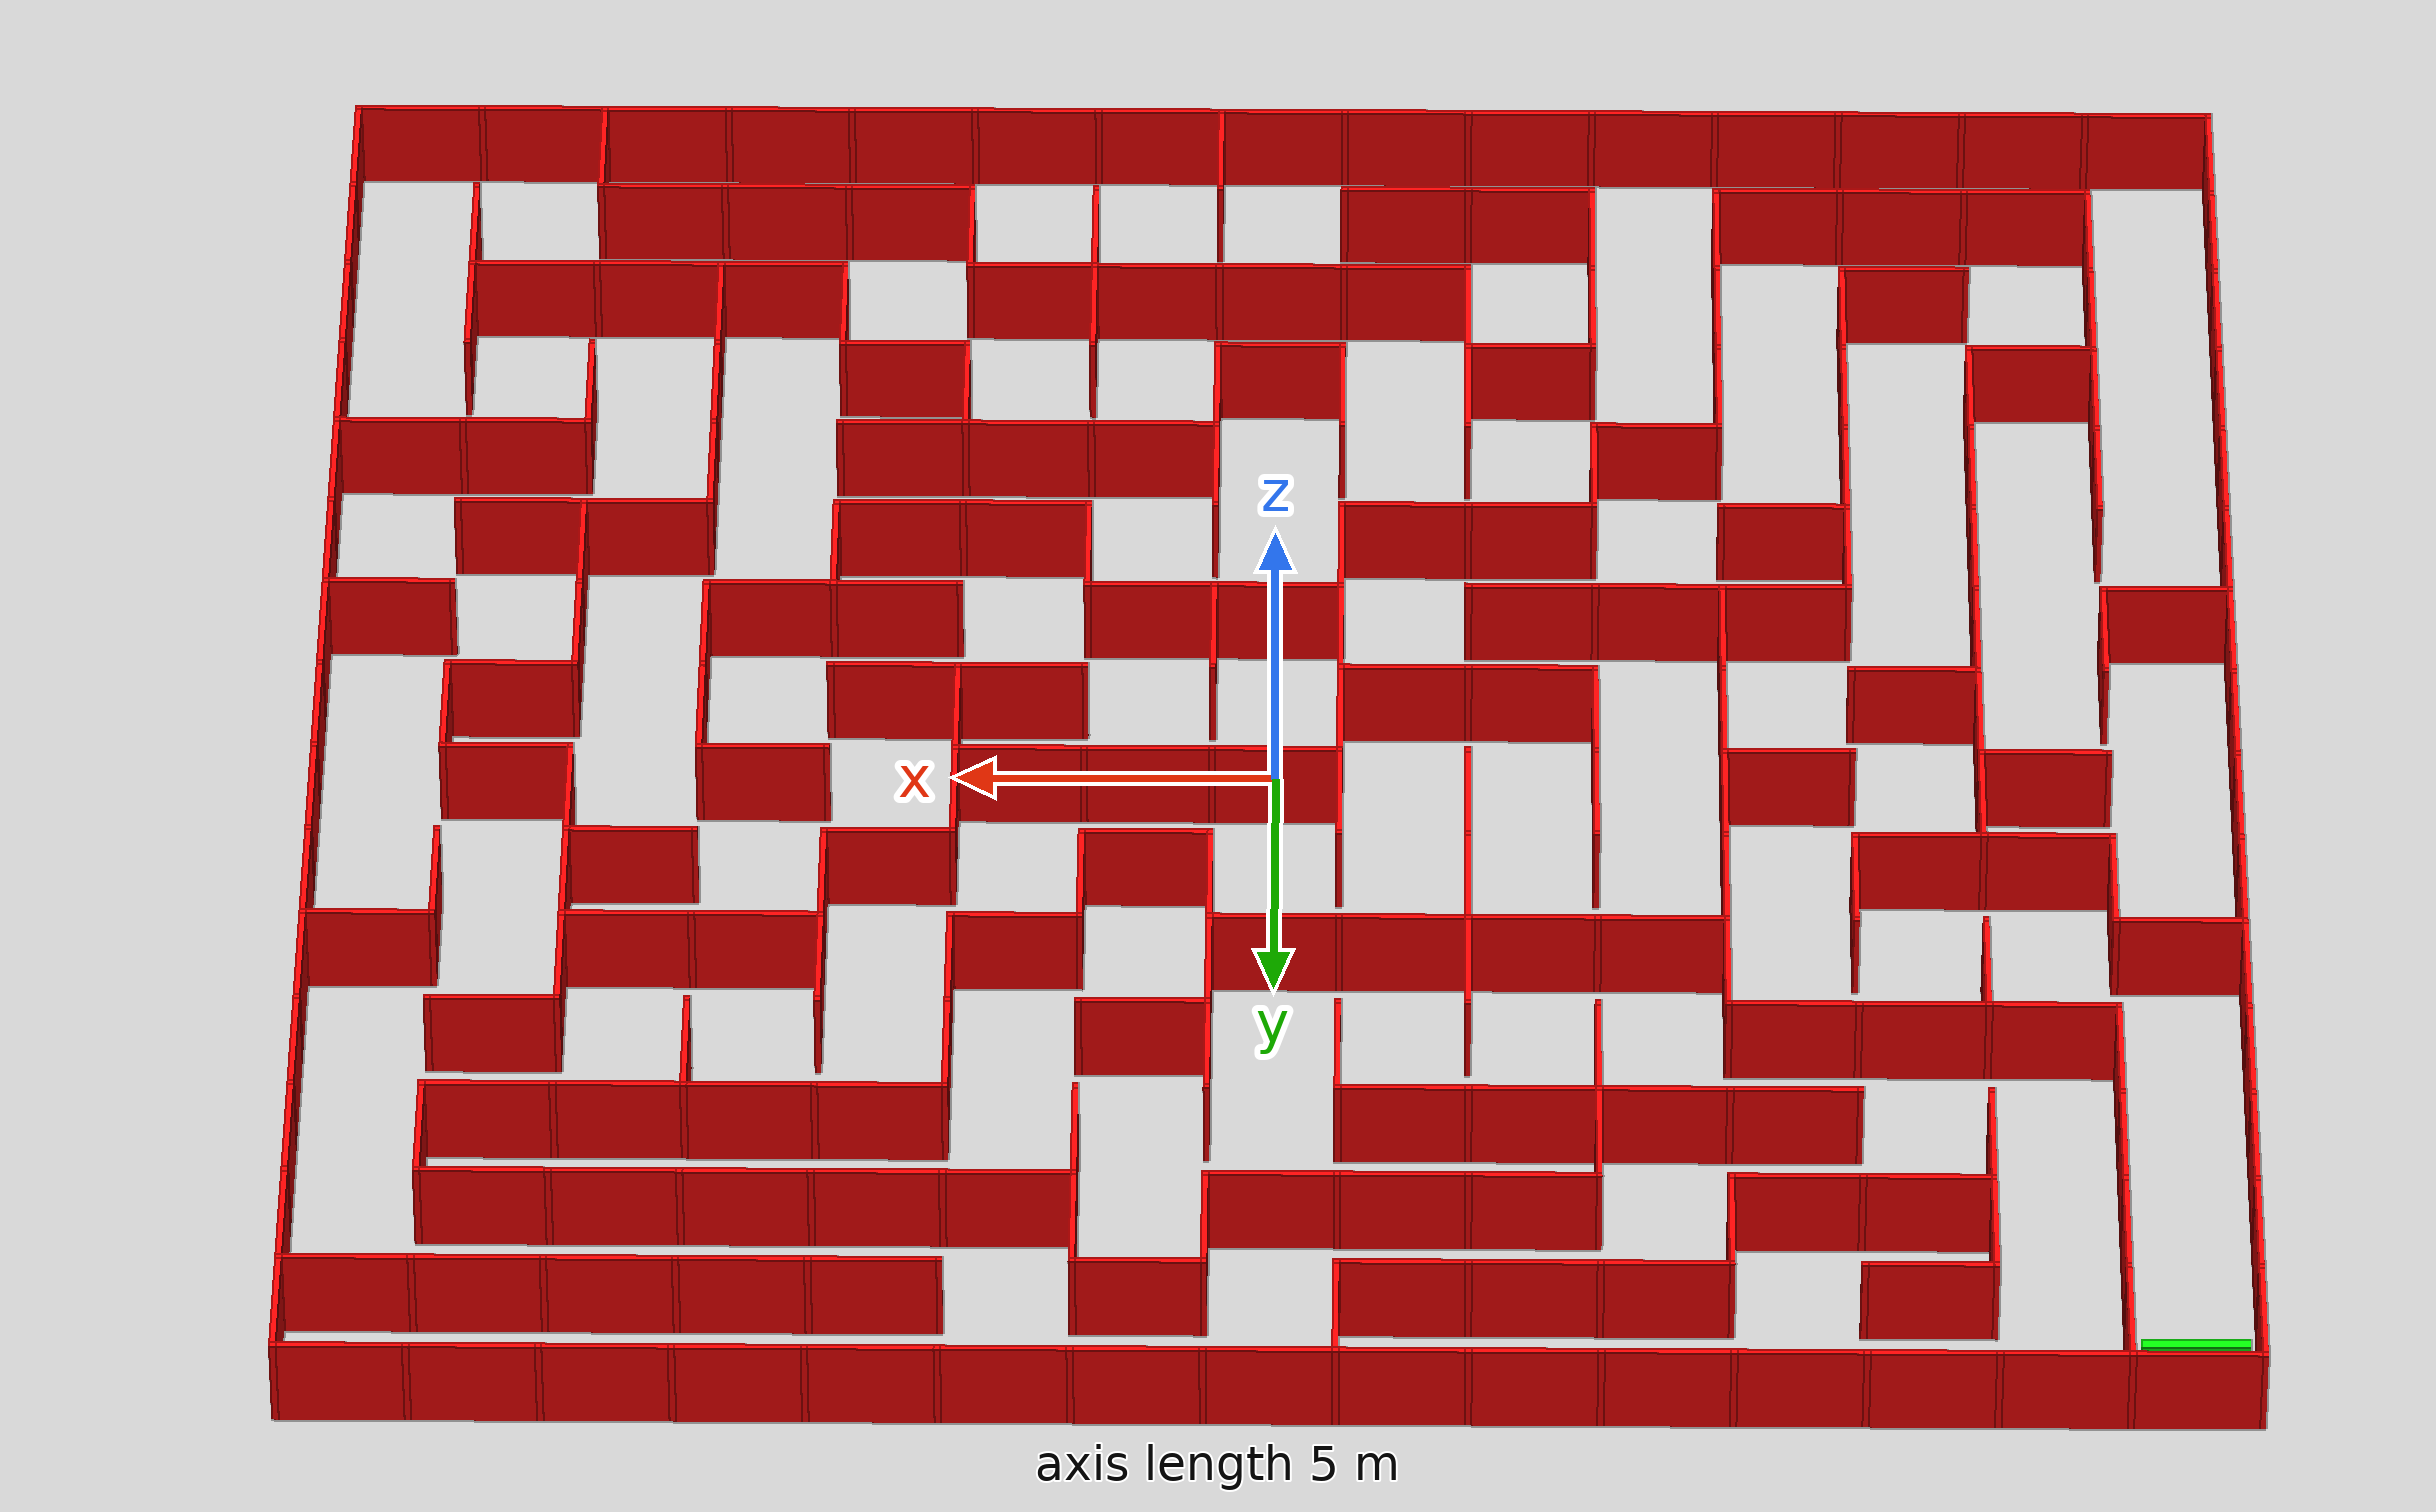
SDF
<sdf version="1.7">
 <world name="empty">
  <physics name="1ms" type="ignored">
   <max_step_size>0.001</max_step_size>
   <real_time_factor>1</real_time_factor>
   <real_time_update_rate>1000</real_time_update_rate>
  </physics>
  <plugin name="gz::sim::systems::Physics" filename="ignition-gazebo-physics-system"/>
  <plugin filename="ignition-gazebo-sensors-system" name="ignition::gazebo::systems::Sensors">
   <render_engine>ogre2</render_engine>
  </plugin>
  <plugin name="gz::sim::systems::UserCommands" filename="ignition-gazebo-user-commands-system"/>
  <plugin name="gz::sim::systems::SceneBroadcaster" filename="ignition-gazebo-scene-broadcaster-system"/>
  <plugin name="gz::sim::systems::Contact" filename="ignition-gazebo-contact-system"/>
  <gravity>0 0 -9.8</gravity>
  <magnetic_field>6e-06 2.3e-05 -4.2e-05</magnetic_field>
  <atmosphere type="adiabatic"/>
  <scene><ambient>0.4 0.4 0.4 1</ambient><background>0.7 0.7 0.7 1</background><shadows>true</shadows></scene>
  <model name="ground_plane">
   <static>true</static>
   <link name="link">
    <collision name="collision1">
     <geometry><plane><normal>0 0 1</normal><size>1 1</size></plane></geometry>
    </collision>
    <visual name="visual1"><geometry><plane><normal>0 0 1</normal><size>100 100</size></plane></geometry></visual>
   </link>
  </model>
  <gravity>0 0 -9.8</gravity>
  <magnetic_field>6e-06 2.3e-05 -4.2e-05</magnetic_field>
  <atmosphere type="adiabatic"/>
  <physics type="ode"/>
  <scene><ambient>0.4 0.4 0.4 1</ambient><background>0.7 0.7 0.7 1</background><shadows>1</shadows></scene>
  <audio><device>default</device></audio>
  <spherical_coordinates>
   <surface_model>EARTH_WGS84</surface_model>
   <latitude_deg>0</latitude_deg>
   <longitude_deg>0</longitude_deg>
   <elevation>0</elevation>
   <heading_deg>0</heading_deg>
  </spherical_coordinates>
  <model name="Untitled">
   <link name="Wall_0_0_h">
    <collision name="Wall_0_Collision">
     <geometry><box><size>1.9 0.1 1.5</size></box></geometry>
     <pose>0 0 0.75 0 -0 0</pose>
    </collision>
    <visual name="Wall_0_Visual">
     <pose>0 0 0.75 0 -0 0</pose>
     <geometry><box><size>1.9 0.1 1.5</size></box></geometry>
     <material><ambient>1 0 0 1</ambient><diffuse>1 0 0 1</diffuse><specular>0.1 0.1 0.1 1</specular></material>
     <meta><layer>0</layer></meta>
    </visual>
    <pose>-14 15 0 0 -0 0</pose>
   </link>
   <link name="Wall_0_0_v">
    <collision name="Wall_0_Collision">
     <geometry><box><size>1.9 0.1 1.5</size></box></geometry>
     <pose>0 0 0.75 0 -0 0</pose>
    </collision>
    <visual name="Wall_0_Visual">
     <pose>0 0 0.75 0 -0 0</pose>
     <geometry><box><size>1.9 0.1 1.5</size></box></geometry>
     <material><ambient>1 0 0 1</ambient><diffuse>1 0 0 1</diffuse><specular>0.1 0.1 0.1 1</specular></material>
     <meta><layer>0</layer></meta>
    </visual>
    <pose>-15 14 0 0 -0 1.5708</pose>
   </link>
   <link name="Joint_-15_15">
    <collision name="Wall_2_Collision">
     <geometry><box><size>0.1 0.1 1.5</size></box></geometry>
     <pose>0 0 0.75 0 -0 0</pose>
    </collision>
    <visual name="Wall_2_Visual">
     <pose>0 0 0.75 0 -0 0</pose>
     <geometry><box><size>0.1 0.1 1.5</size></box></geometry>
     <material><ambient>1 0 0 1</ambient><diffuse>1 0 0 1</diffuse><specular>0.1 0.1 0.1 1</specular></material>
     <meta><layer>0</layer></meta>
    </visual>
    <pose>-15 15 0 0 -0 0</pose>
   </link>
   <link name="Wall_1_0_h">
    <collision name="Wall_0_Collision">
     <geometry><box><size>1.9 0.1 1.5</size></box></geometry>
     <pose>0 0 0.75 0 -0 0</pose>
    </collision>
    <visual name="Wall_0_Visual">
     <pose>0 0 0.75 0 -0 0</pose>
     <geometry><box><size>1.9 0.1 1.5</size></box></geometry>
     <material><ambient>1 0 0 1</ambient><diffuse>1 0 0 1</diffuse><specular>0.1 0.1 0.1 1</specular></material>
     <meta><layer>0</layer></meta>
    </visual>
    <pose>-12 15 0 0 -0 0</pose>
   </link>
   <link name="Wall_1_0_v">
    <collision name="Wall_0_Collision">
     <geometry><box><size>1.9 0.1 1.5</size></box></geometry>
     <pose>0 0 0.75 0 -0 0</pose>
    </collision>
    <visual name="Wall_0_Visual">
     <pose>0 0 0.75 0 -0 0</pose>
     <geometry><box><size>1.9 0.1 1.5</size></box></geometry>
     <material><ambient>1 0 0 1</ambient><diffuse>1 0 0 1</diffuse><specular>0.1 0.1 0.1 1</specular></material>
     <meta><layer>0</layer></meta>
    </visual>
    <pose>-13 14 0 0 -0 1.5708</pose>
   </link>
   <link name="Joint_-13_15">
    <collision name="Wall_2_Collision">
     <geometry><box><size>0.1 0.1 1.5</size></box></geometry>
     <pose>0 0 0.75 0 -0 0</pose>
    </collision>
    <visual name="Wall_2_Visual">
     <pose>0 0 0.75 0 -0 0</pose>
     <geometry><box><size>0.1 0.1 1.5</size></box></geometry>
     <material><ambient>1 0 0 1</ambient><diffuse>1 0 0 1</diffuse><specular>0.1 0.1 0.1 1</specular></material>
     <meta><layer>0</layer></meta>
    </visual>
    <pose>-13 15 0 0 -0 0</pose>
   </link>
   <link name="Wall_2_0_h">
    <collision name="Wall_0_Collision">
     <geometry><box><size>1.9 0.1 1.5</size></box></geometry>
     <pose>0 0 0.75 0 -0 0</pose>
    </collision>
    <visual name="Wall_0_Visual">
     <pose>0 0 0.75 0 -0 0</pose>
     <geometry><box><size>1.9 0.1 1.5</size></box></geometry>
     <material><ambient>1 0 0 1</ambient><diffuse>1 0 0 1</diffuse><specular>0.1 0.1 0.1 1</specular></material>
     <meta><layer>0</layer></meta>
    </visual>
    <pose>-10 15 0 0 -0 0</pose>
   </link>
   <link name="Joint_-11_15">
    <collision name="Wall_2_Collision">
     <geometry><box><size>0.1 0.1 1.5</size></box></geometry>
     <pose>0 0 0.75 0 -0 0</pose>
    </collision>
    <visual name="Wall_2_Visual">
     <pose>0 0 0.75 0 -0 0</pose>
     <geometry><box><size>0.1 0.1 1.5</size></box></geometry>
     <material><ambient>1 0 0 1</ambient><diffuse>1 0 0 1</diffuse><specular>0.1 0.1 0.1 1</specular></material>
     <meta><layer>0</layer></meta>
    </visual>
    <pose>-11 15 0 0 -0 0</pose>
   </link>
   <link name="Wall_3_0_h">
    <collision name="Wall_0_Collision">
     <geometry><box><size>1.9 0.1 1.5</size></box></geometry>
     <pose>0 0 0.75 0 -0 0</pose>
    </collision>
    <visual name="Wall_0_Visual">
     <pose>0 0 0.75 0 -0 0</pose>
     <geometry><box><size>1.9 0.1 1.5</size></box></geometry>
     <material><ambient>1 0 0 1</ambient><diffuse>1 0 0 1</diffuse><specular>0.1 0.1 0.1 1</specular></material>
     <meta><layer>0</layer></meta>
    </visual>
    <pose>-8 15 0 0 -0 0</pose>
   </link>
   <link name="Joint_-9_15">
    <collision name="Wall_2_Collision">
     <geometry><box><size>0.1 0.1 1.5</size></box></geometry>
     <pose>0 0 0.75 0 -0 0</pose>
    </collision>
    <visual name="Wall_2_Visual">
     <pose>0 0 0.75 0 -0 0</pose>
     <geometry><box><size>0.1 0.1 1.5</size></box></geometry>
     <material><ambient>1 0 0 1</ambient><diffuse>1 0 0 1</diffuse><specular>0.1 0.1 0.1 1</specular></material>
     <meta><layer>0</layer></meta>
    </visual>
    <pose>-9 15 0 0 -0 0</pose>
   </link>
   <link name="Wall_4_0_h">
    <collision name="Wall_0_Collision">
     <geometry><box><size>1.9 0.1 1.5</size></box></geometry>
     <pose>0 0 0.75 0 -0 0</pose>
    </collision>
    <visual name="Wall_0_Visual">
     <pose>0 0 0.75 0 -0 0</pose>
     <geometry><box><size>1.9 0.1 1.5</size></box></geometry>
     <material><ambient>1 0 0 1</ambient><diffuse>1 0 0 1</diffuse><specular>0.1 0.1 0.1 1</specular></material>
     <meta><layer>0</layer></meta>
    </visual>
    <pose>-6 15 0 0 -0 0</pose>
   </link>
   <link name="Joint_-7_15">
    <collision name="Wall_2_Collision">
     <geometry><box><size>0.1 0.1 1.5</size></box></geometry>
     <pose>0 0 0.75 0 -0 0</pose>
    </collision>
    <visual name="Wall_2_Visual">
     <pose>0 0 0.75 0 -0 0</pose>
     <geometry><box><size>0.1 0.1 1.5</size></box></geometry>
     <material><ambient>1 0 0 1</ambient><diffuse>1 0 0 1</diffuse><specular>0.1 0.1 0.1 1</specular></material>
     <meta><layer>0</layer></meta>
    </visual>
    <pose>-7 15 0 0 -0 0</pose>
   </link>
   <link name="Wall_5_0_h">
    <collision name="Wall_0_Collision">
     <geometry><box><size>1.9 0.1 1.5</size></box></geometry>
     <pose>0 0 0.75 0 -0 0</pose>
    </collision>
    <visual name="Wall_0_Visual">
     <pose>0 0 0.75 0 -0 0</pose>
     <geometry><box><size>1.9 0.1 1.5</size></box></geometry>
     <material><ambient>1 0 0 1</ambient><diffuse>1 0 0 1</diffuse><specular>0.1 0.1 0.1 1</specular></material>
     <meta><layer>0</layer></meta>
    </visual>
    <pose>-4 15 0 0 -0 0</pose>
   </link>
   <link name="Joint_-5_15">
    <collision name="Wall_2_Collision">
     <geometry><box><size>0.1 0.1 1.5</size></box></geometry>
     <pose>0 0 0.75 0 -0 0</pose>
    </collision>
    <visual name="Wall_2_Visual">
     <pose>0 0 0.75 0 -0 0</pose>
     <geometry><box><size>0.1 0.1 1.5</size></box></geometry>
     <material><ambient>1 0 0 1</ambient><diffuse>1 0 0 1</diffuse><specular>0.1 0.1 0.1 1</specular></material>
     <meta><layer>0</layer></meta>
    </visual>
    <pose>-5 15 0 0 -0 0</pose>
   </link>
   <link name="Wall_6_0_h">
    <collision name="Wall_0_Collision">
     <geometry><box><size>1.9 0.1 1.5</size></box></geometry>
     <pose>0 0 0.75 0 -0 0</pose>
    </collision>
    <visual name="Wall_0_Visual">
     <pose>0 0 0.75 0 -0 0</pose>
     <geometry><box><size>1.9 0.1 1.5</size></box></geometry>
     <material><ambient>1 0 0 1</ambient><diffuse>1 0 0 1</diffuse><specular>0.1 0.1 0.1 1</specular></material>
     <meta><layer>0</layer></meta>
    </visual>
    <pose>-2 15 0 0 -0 0</pose>
   </link>
   <link name="Joint_-3_15">
    <collision name="Wall_2_Collision">
     <geometry><box><size>0.1 0.1 1.5</size></box></geometry>
     <pose>0 0 0.75 0 -0 0</pose>
    </collision>
    <visual name="Wall_2_Visual">
     <pose>0 0 0.75 0 -0 0</pose>
     <geometry><box><size>0.1 0.1 1.5</size></box></geometry>
     <material><ambient>1 0 0 1</ambient><diffuse>1 0 0 1</diffuse><specular>0.1 0.1 0.1 1</specular></material>
     <meta><layer>0</layer></meta>
    </visual>
    <pose>-3 15 0 0 -0 0</pose>
   </link>
   <link name="Wall_7_0_h">
    <collision name="Wall_0_Collision">
     <geometry><box><size>1.9 0.1 1.5</size></box></geometry>
     <pose>0 0 0.75 0 -0 0</pose>
    </collision>
    <visual name="Wall_0_Visual">
     <pose>0 0 0.75 0 -0 0</pose>
     <geometry><box><size>1.9 0.1 1.5</size></box></geometry>
     <material><ambient>1 0 0 1</ambient><diffuse>1 0 0 1</diffuse><specular>0.1 0.1 0.1 1</specular></material>
     <meta><layer>0</layer></meta>
    </visual>
    <pose>0 15 0 0 -0 0</pose>
   </link>
   <link name="Wall_7_0_v">
    <collision name="Wall_0_Collision">
     <geometry><box><size>1.9 0.1 1.5</size></box></geometry>
     <pose>0 0 0.75 0 -0 0</pose>
    </collision>
    <visual name="Wall_0_Visual">
     <pose>0 0 0.75 0 -0 0</pose>
     <geometry><box><size>1.9 0.1 1.5</size></box></geometry>
     <material><ambient>1 0 0 1</ambient><diffuse>1 0 0 1</diffuse><specular>0.1 0.1 0.1 1</specular></material>
     <meta><layer>0</layer></meta>
    </visual>
    <pose>-1 14 0 0 -0 1.5708</pose>
   </link>
   <link name="Joint_-1_15">
    <collision name="Wall_2_Collision">
     <geometry><box><size>0.1 0.1 1.5</size></box></geometry>
     <pose>0 0 0.75 0 -0 0</pose>
    </collision>
    <visual name="Wall_2_Visual">
     <pose>0 0 0.75 0 -0 0</pose>
     <geometry><box><size>0.1 0.1 1.5</size></box></geometry>
     <material><ambient>1 0 0 1</ambient><diffuse>1 0 0 1</diffuse><specular>0.1 0.1 0.1 1</specular></material>
     <meta><layer>0</layer></meta>
    </visual>
    <pose>-1 15 0 0 -0 0</pose>
   </link>
   <link name="Wall_8_0_h">
    <collision name="Wall_0_Collision">
     <geometry><box><size>1.9 0.1 1.5</size></box></geometry>
     <pose>0 0 0.75 0 -0 0</pose>
    </collision>
    <visual name="Wall_0_Visual">
     <pose>0 0 0.75 0 -0 0</pose>
     <geometry><box><size>1.9 0.1 1.5</size></box></geometry>
     <material><ambient>1 0 0 1</ambient><diffuse>1 0 0 1</diffuse><specular>0.1 0.1 0.1 1</specular></material>
     <meta><layer>0</layer></meta>
    </visual>
    <pose>2 15 0 0 -0 0</pose>
   </link>
   <link name="Joint_1_15">
    <collision name="Wall_2_Collision">
     <geometry><box><size>0.1 0.1 1.5</size></box></geometry>
     <pose>0 0 0.75 0 -0 0</pose>
    </collision>
    <visual name="Wall_2_Visual">
     <pose>0 0 0.75 0 -0 0</pose>
     <geometry><box><size>0.1 0.1 1.5</size></box></geometry>
     <material><ambient>1 0 0 1</ambient><diffuse>1 0 0 1</diffuse><specular>0.1 0.1 0.1 1</specular></material>
     <meta><layer>0</layer></meta>
    </visual>
    <pose>1 15 0 0 -0 0</pose>
   </link>
   <link name="Wall_9_0_h">
    <collision name="Wall_0_Collision">
     <geometry><box><size>1.9 0.1 1.5</size></box></geometry>
     <pose>0 0 0.75 0 -0 0</pose>
    </collision>
    <visual name="Wall_0_Visual">
     <pose>0 0 0.75 0 -0 0</pose>
     <geometry><box><size>1.9 0.1 1.5</size></box></geometry>
     <material><ambient>1 0 0 1</ambient><diffuse>1 0 0 1</diffuse><specular>0.1 0.1 0.1 1</specular></material>
     <meta><layer>0</layer></meta>
    </visual>
    <pose>4 15 0 0 -0 0</pose>
   </link>
   <link name="Joint_3_15">
    <collision name="Wall_2_Collision">
     <geometry><box><size>0.1 0.1 1.5</size></box></geometry>
     <pose>0 0 0.75 0 -0 0</pose>
    </collision>
    <visual name="Wall_2_Visual">
     <pose>0 0 0.75 0 -0 0</pose>
     <geometry><box><size>0.1 0.1 1.5</size></box></geometry>
     <material><ambient>1 0 0 1</ambient><diffuse>1 0 0 1</diffuse><specular>0.1 0.1 0.1 1</specular></material>
     <meta><layer>0</layer></meta>
    </visual>
    <pose>3 15 0 0 -0 0</pose>
   </link>
   <link name="Wall_10_0_h">
    <collision name="Wall_0_Collision">
     <geometry><box><size>1.9 0.1 1.5</size></box></geometry>
     <pose>0 0 0.75 0 -0 0</pose>
    </collision>
    <visual name="Wall_0_Visual">
     <pose>0 0 0.75 0 -0 0</pose>
     <geometry><box><size>1.9 0.1 1.5</size></box></geometry>
     <material><ambient>1 0 0 1</ambient><diffuse>1 0 0 1</diffuse><specular>0.1 0.1 0.1 1</specular></material>
     <meta><layer>0</layer></meta>
    </visual>
    <pose>6 15 0 0 -0 0</pose>
   </link>
   <link name="Joint_5_15">
    <collision name="Wall_2_Collision">
     <geometry><box><size>0.1 0.1 1.5</size></box></geometry>
     <pose>0 0 0.75 0 -0 0</pose>
    </collision>
    <visual name="Wall_2_Visual">
     <pose>0 0 0.75 0 -0 0</pose>
     <geometry><box><size>0.1 0.1 1.5</size></box></geometry>
     <material><ambient>1 0 0 1</ambient><diffuse>1 0 0 1</diffuse><specular>0.1 0.1 0.1 1</specular></material>
     <meta><layer>0</layer></meta>
    </visual>
    <pose>5 15 0 0 -0 0</pose>
   </link>
   <link name="Wall_11_0_h">
    <collision name="Wall_0_Collision">
     <geometry><box><size>1.9 0.1 1.5</size></box></geometry>
     <pose>0 0 0.75 0 -0 0</pose>
    </collision>
    <visual name="Wall_0_Visual">
     <pose>0 0 0.75 0 -0 0</pose>
     <geometry><box><size>1.9 0.1 1.5</size></box></geometry>
     <material><ambient>1 0 0 1</ambient><diffuse>1 0 0 1</diffuse><specular>0.1 0.1 0.1 1</specular></material>
     <meta><layer>0</layer></meta>
    </visual>
    <pose>8 15 0 0 -0 0</pose>
   </link>
   <link name="Joint_7_15">
    <collision name="Wall_2_Collision">
     <geometry><box><size>0.1 0.1 1.5</size></box></geometry>
     <pose>0 0 0.75 0 -0 0</pose>
    </collision>
    <visual name="Wall_2_Visual">
     <pose>0 0 0.75 0 -0 0</pose>
     <geometry><box><size>0.1 0.1 1.5</size></box></geometry>
     <material><ambient>1 0 0 1</ambient><diffuse>1 0 0 1</diffuse><specular>0.1 0.1 0.1 1</specular></material>
     <meta><layer>0</layer></meta>
    </visual>
    <pose>7 15 0 0 -0 0</pose>
   </link>
   <link name="Wall_12_0_h">
    <collision name="Wall_0_Collision">
     <geometry><box><size>1.9 0.1 1.5</size></box></geometry>
     <pose>0 0 0.75 0 -0 0</pose>
    </collision>
    <visual name="Wall_0_Visual">
     <pose>0 0 0.75 0 -0 0</pose>
     <geometry><box><size>1.9 0.1 1.5</size></box></geometry>
     <material><ambient>1 0 0 1</ambient><diffuse>1 0 0 1</diffuse><specular>0.1 0.1 0.1 1</specular></material>
     <meta><layer>0</layer></meta>
    </visual>
    <pose>10 15 0 0 -0 0</pose>
   </link>
   <link name="Joint_9_15">
    <collision name="Wall_2_Collision">
     <geometry><box><size>0.1 0.1 1.5</size></box></geometry>
     <pose>0 0 0.75 0 -0 0</pose>
    </collision>
    <visual name="Wall_2_Visual">
     <pose>0 0 0.75 0 -0 0</pose>
     <geometry><box><size>0.1 0.1 1.5</size></box></geometry>
     <material><ambient>1 0 0 1</ambient><diffuse>1 0 0 1</diffuse><specular>0.1 0.1 0.1 1</specular></material>
     <meta><layer>0</layer></meta>
    </visual>
    <pose>9 15 0 0 -0 0</pose>
   </link>
   <link name="Wall_13_0_h">
    <collision name="Wall_0_Collision">
     <geometry><box><size>1.9 0.1 1.5</size></box></geometry>
     <pose>0 0 0.75 0 -0 0</pose>
    </collision>
    <visual name="Wall_0_Visual">
     <pose>0 0 0.75 0 -0 0</pose>
     <geometry><box><size>1.9 0.1 1.5</size></box></geometry>
     <material><ambient>1 0 0 1</ambient><diffuse>1 0 0 1</diffuse><specular>0.1 0.1 0.1 1</specular></material>
     <meta><layer>0</layer></meta>
    </visual>
    <pose>12 15 0 0 -0 0</pose>
   </link>
   <link name="Joint_11_15">
    <collision name="Wall_2_Collision">
     <geometry><box><size>0.1 0.1 1.5</size></box></geometry>
     <pose>0 0 0.75 0 -0 0</pose>
    </collision>
    <visual name="Wall_2_Visual">
     <pose>0 0 0.75 0 -0 0</pose>
     <geometry><box><size>0.1 0.1 1.5</size></box></geometry>
     <material><ambient>1 0 0 1</ambient><diffuse>1 0 0 1</diffuse><specular>0.1 0.1 0.1 1</specular></material>
     <meta><layer>0</layer></meta>
    </visual>
    <pose>11 15 0 0 -0 0</pose>
   </link>
   <link name="Wall_14_0_h">
    <collision name="Wall_0_Collision">
     <geometry><box><size>1.9 0.1 1.5</size></box></geometry>
     <pose>0 0 0.75 0 -0 0</pose>
    </collision>
    <visual name="Wall_0_Visual">
     <pose>0 0 0.75 0 -0 0</pose>
     <geometry><box><size>1.9 0.1 1.5</size></box></geometry>
     <material><ambient>1 0 0 1</ambient><diffuse>1 0 0 1</diffuse><specular>0.1 0.1 0.1 1</specular></material>
     <meta><layer>0</layer></meta>
    </visual>
    <pose>14 15 0 0 -0 0</pose>
   </link>
   <link name="Joint_13_15">
    <collision name="Wall_2_Collision">
     <geometry><box><size>0.1 0.1 1.5</size></box></geometry>
     <pose>0 0 0.75 0 -0 0</pose>
    </collision>
    <visual name="Wall_2_Visual">
     <pose>0 0 0.75 0 -0 0</pose>
     <geometry><box><size>0.1 0.1 1.5</size></box></geometry>
     <material><ambient>1 0 0 1</ambient><diffuse>1 0 0 1</diffuse><specular>0.1 0.1 0.1 1</specular></material>
     <meta><layer>0</layer></meta>
    </visual>
    <pose>13 15 0 0 -0 0</pose>
   </link>
   <link name="Wall_15_0_v">
    <collision name="Wall_0_Collision">
     <geometry><box><size>1.9 0.1 1.5</size></box></geometry>
     <pose>0 0 0.75 0 -0 0</pose>
    </collision>
    <visual name="Wall_0_Visual">
     <pose>0 0 0.75 0 -0 0</pose>
     <geometry><box><size>1.9 0.1 1.5</size></box></geometry>
     <material><ambient>1 0 0 1</ambient><diffuse>1 0 0 1</diffuse><specular>0.1 0.1 0.1 1</specular></material>
     <meta><layer>0</layer></meta>
    </visual>
    <pose>15 14 0 0 -0 1.5708</pose>
   </link>
   <link name="Joint_15_15">
    <collision name="Wall_2_Collision">
     <geometry><box><size>0.1 0.1 1.5</size></box></geometry>
     <pose>0 0 0.75 0 -0 0</pose>
    </collision>
    <visual name="Wall_2_Visual">
     <pose>0 0 0.75 0 -0 0</pose>
     <geometry><box><size>0.1 0.1 1.5</size></box></geometry>
     <material><ambient>1 0 0 1</ambient><diffuse>1 0 0 1</diffuse><specular>0.1 0.1 0.1 1</specular></material>
     <meta><layer>0</layer></meta>
    </visual>
    <pose>15 15 0 0 -0 0</pose>
   </link>
   <link name="Wall_0_1_v">
    <collision name="Wall_0_Collision">
     <geometry><box><size>1.9 0.1 1.5</size></box></geometry>
     <pose>0 0 0.75 0 -0 0</pose>
    </collision>
    <visual name="Wall_0_Visual">
     <pose>0 0 0.75 0 -0 0</pose>
     <geometry><box><size>1.9 0.1 1.5</size></box></geometry>
     <material><ambient>1 0 0 1</ambient><diffuse>1 0 0 1</diffuse><specular>0.1 0.1 0.1 1</specular></material>
     <meta><layer>0</layer></meta>
    </visual>
    <pose>-15 12 0 0 -0 1.5708</pose>
   </link>
   <link name="Joint_-15_13">
    <collision name="Wall_2_Collision">
     <geometry><box><size>0.1 0.1 1.5</size></box></geometry>
     <pose>0 0 0.75 0 -0 0</pose>
    </collision>
    <visual name="Wall_2_Visual">
     <pose>0 0 0.75 0 -0 0</pose>
     <geometry><box><size>0.1 0.1 1.5</size></box></geometry>
     <material><ambient>1 0 0 1</ambient><diffuse>1 0 0 1</diffuse><specular>0.1 0.1 0.1 1</specular></material>
     <meta><layer>0</layer></meta>
    </visual>
    <pose>-15 13 0 0 -0 0</pose>
   </link>
   <link name="Wall_1_1_v">
    <collision name="Wall_0_Collision">
     <geometry><box><size>1.9 0.1 1.5</size></box></geometry>
     <pose>0 0 0.75 0 -0 0</pose>
    </collision>
    <visual name="Wall_0_Visual">
     <pose>0 0 0.75 0 -0 0</pose>
     <geometry><box><size>1.9 0.1 1.5</size></box></geometry>
     <material><ambient>1 0 0 1</ambient><diffuse>1 0 0 1</diffuse><specular>0.1 0.1 0.1 1</specular></material>
     <meta><layer>0</layer></meta>
    </visual>
    <pose>-13 12 0 0 -0 1.5708</pose>
   </link>
   <link name="Joint_-13_13">
    <collision name="Wall_2_Collision">
     <geometry><box><size>0.1 0.1 1.5</size></box></geometry>
     <pose>0 0 0.75 0 -0 0</pose>
    </collision>
    <visual name="Wall_2_Visual">
     <pose>0 0 0.75 0 -0 0</pose>
     <geometry><box><size>0.1 0.1 1.5</size></box></geometry>
     <material><ambient>1 0 0 1</ambient><diffuse>1 0 0 1</diffuse><specular>0.1 0.1 0.1 1</specular></material>
     <meta><layer>0</layer></meta>
    </visual>
    <pose>-13 13 0 0 -0 0</pose>
   </link>
   <link name="Wall_2_1_h">
    <collision name="Wall_0_Collision">
     <geometry><box><size>1.9 0.1 1.5</size></box></geometry>
     <pose>0 0 0.75 0 -0 0</pose>
    </collision>
    <visual name="Wall_0_Visual">
     <pose>0 0 0.75 0 -0 0</pose>
     <geometry><box><size>1.9 0.1 1.5</size></box></geometry>
     <material><ambient>1 0 0 1</ambient><diffuse>1 0 0 1</diffuse><specular>0.1 0.1 0.1 1</specular></material>
     <meta><layer>0</layer></meta>
    </visual>
    <pose>-10 13 0 0 -0 0</pose>
   </link>
   <link name="Wall_2_1_v">
    <collision name="Wall_0_Collision">
     <geometry><box><size>1.9 0.1 1.5</size></box></geometry>
     <pose>0 0 0.75 0 -0 0</pose>
    </collision>
    <visual name="Wall_0_Visual">
     <pose>0 0 0.75 0 -0 0</pose>
     <geometry><box><size>1.9 0.1 1.5</size></box></geometry>
     <material><ambient>1 0 0 1</ambient><diffuse>1 0 0 1</diffuse><specular>0.1 0.1 0.1 1</specular></material>
     <meta><layer>0</layer></meta>
    </visual>
    <pose>-11 12 0 0 -0 1.5708</pose>
   </link>
   <link name="Joint_-11_13">
    <collision name="Wall_2_Collision">
     <geometry><box><size>0.1 0.1 1.5</size></box></geometry>
     <pose>0 0 0.75 0 -0 0</pose>
    </collision>
    <visual name="Wall_2_Visual">
     <pose>0 0 0.75 0 -0 0</pose>
     <geometry><box><size>0.1 0.1 1.5</size></box></geometry>
     <material><ambient>1 0 0 1</ambient><diffuse>1 0 0 1</diffuse><specular>0.1 0.1 0.1 1</specular></material>
     <meta><layer>0</layer></meta>
    </visual>
    <pose>-11 13 0 0 -0 0</pose>
   </link>
   <link name="Joint_-9_13">
    <collision name="Wall_2_Collision">
     <geometry><box><size>0.1 0.1 1.5</size></box></geometry>
     <pose>0 0 0.75 0 -0 0</pose>
    </collision>
    <visual name="Wall_2_Visual">
     <pose>0 0 0.75 0 -0 0</pose>
     <geometry><box><size>0.1 0.1 1.5</size></box></geometry>
     <material><ambient>1 0 0 1</ambient><diffuse>1 0 0 1</diffuse><specular>0.1 0.1 0.1 1</specular></material>
     <meta><layer>0</layer></meta>
    </visual>
    <pose>-9 13 0 0 -0 0</pose>
   </link>
   <link name="Wall_4_1_h">
    <collision name="Wall_0_Collision">
     <geometry><box><size>1.9 0.1 1.5</size></box></geometry>
     <pose>0 0 0.75 0 -0 0</pose>
    </collision>
    <visual name="Wall_0_Visual">
     <pose>0 0 0.75 0 -0 0</pose>
     <geometry><box><size>1.9 0.1 1.5</size></box></geometry>
     <material><ambient>1 0 0 1</ambient><diffuse>1 0 0 1</diffuse><specular>0.1 0.1 0.1 1</specular></material>
     <meta><layer>0</layer></meta>
    </visual>
    <pose>-6 13 0 0 -0 0</pose>
   </link>
   <link name="Wall_4_1_v">
    <collision name="Wall_0_Collision">
     <geometry><box><size>1.9 0.1 1.5</size></box></geometry>
     <pose>0 0 0.75 0 -0 0</pose>
    </collision>
    <visual name="Wall_0_Visual">
     <pose>0 0 0.75 0 -0 0</pose>
     <geometry><box><size>1.9 0.1 1.5</size></box></geometry>
     <material><ambient>1 0 0 1</ambient><diffuse>1 0 0 1</diffuse><specular>0.1 0.1 0.1 1</specular></material>
     <meta><layer>0</layer></meta>
    </visual>
    <pose>-7 12 0 0 -0 1.5708</pose>
   </link>
   <link name="Joint_-7_13">
    <collision name="Wall_2_Collision">
     <geometry><box><size>0.1 0.1 1.5</size></box></geometry>
     <pose>0 0 0.75 0 -0 0</pose>
    </collision>
    <visual name="Wall_2_Visual">
     <pose>0 0 0.75 0 -0 0</pose>
     <geometry><box><size>0.1 0.1 1.5</size></box></geometry>
     <material><ambient>1 0 0 1</ambient><diffuse>1 0 0 1</diffuse><specular>0.1 0.1 0.1 1</specular></material>
     <meta><layer>0</layer></meta>
    </visual>
    <pose>-7 13 0 0 -0 0</pose>
   </link>
   <link name="Wall_5_1_h">
    <collision name="Wall_0_Collision">
     <geometry><box><size>1.9 0.1 1.5</size></box></geometry>
     <pose>0 0 0.75 0 -0 0</pose>
    </collision>
    <visual name="Wall_0_Visual">
     <pose>0 0 0.75 0 -0 0</pose>
     <geometry><box><size>1.9 0.1 1.5</size></box></geometry>
     <material><ambient>1 0 0 1</ambient><diffuse>1 0 0 1</diffuse><specular>0.1 0.1 0.1 1</specular></material>
     <meta><layer>0</layer></meta>
    </visual>
    <pose>-4 13 0 0 -0 0</pose>
   </link>
   <link name="Joint_-5_13">
    <collision name="Wall_2_Collision">
     <geometry><box><size>0.1 0.1 1.5</size></box></geometry>
     <pose>0 0 0.75 0 -0 0</pose>
    </collision>
    <visual name="Wall_2_Visual">
     <pose>0 0 0.75 0 -0 0</pose>
     <geometry><box><size>0.1 0.1 1.5</size></box></geometry>
     <material><ambient>1 0 0 1</ambient><diffuse>1 0 0 1</diffuse><specular>0.1 0.1 0.1 1</specular></material>
     <meta><layer>0</layer></meta>
    </visual>
    <pose>-5 13 0 0 -0 0</pose>
   </link>
   <link name="Wall_6_1_h">
    <collision name="Wall_0_Collision">
     <geometry><box><size>1.9 0.1 1.5</size></box></geometry>
     <pose>0 0 0.75 0 -0 0</pose>
    </collision>
    <visual name="Wall_0_Visual">
     <pose>0 0 0.75 0 -0 0</pose>
     <geometry><box><size>1.9 0.1 1.5</size></box></geometry>
     <material><ambient>1 0 0 1</ambient><diffuse>1 0 0 1</diffuse><specular>0.1 0.1 0.1 1</specular></material>
     <meta><layer>0</layer></meta>
    </visual>
    <pose>-2 13 0 0 -0 0</pose>
   </link>
   <link name="Joint_-3_13">
    <collision name="Wall_2_Collision">
     <geometry><box><size>0.1 0.1 1.5</size></box></geometry>
     <pose>0 0 0.75 0 -0 0</pose>
    </collision>
    <visual name="Wall_2_Visual">
     <pose>0 0 0.75 0 -0 0</pose>
     <geometry><box><size>0.1 0.1 1.5</size></box></geometry>
     <material><ambient>1 0 0 1</ambient><diffuse>1 0 0 1</diffuse><specular>0.1 0.1 0.1 1</specular></material>
     <meta><layer>0</layer></meta>
    </visual>
    <pose>-3 13 0 0 -0 0</pose>
   </link>
   <link name="Joint_-1_13">
    <collision name="Wall_2_Collision">
     <geometry><box><size>0.1 0.1 1.5</size></box></geometry>
     <pose>0 0 0.75 0 -0 0</pose>
    </collision>
    <visual name="Wall_2_Visual">
     <pose>0 0 0.75 0 -0 0</pose>
     <geometry><box><size>0.1 0.1 1.5</size></box></geometry>
     <material><ambient>1 0 0 1</ambient><diffuse>1 0 0 1</diffuse><specular>0.1 0.1 0.1 1</specular></material>
     <meta><layer>0</layer></meta>
    </visual>
    <pose>-1 13 0 0 -0 0</pose>
   </link>
   <link name="Wall_8_1_h">
    <collision name="Wall_0_Collision">
     <geometry><box><size>1.9 0.1 1.5</size></box></geometry>
     <pose>0 0 0.75 0 -0 0</pose>
    </collision>
    <visual name="Wall_0_Visual">
     <pose>0 0 0.75 0 -0 0</pose>
     <geometry><box><size>1.9 0.1 1.5</size></box></geometry>
     <material><ambient>1 0 0 1</ambient><diffuse>1 0 0 1</diffuse><specular>0.1 0.1 0.1 1</specular></material>
     <meta><layer>0</layer></meta>
    </visual>
    <pose>2 13 0 0 -0 0</pose>
   </link>
   <link name="Wall_8_1_v">
    <collision name="Wall_0_Collision">
     <geometry><box><size>1.9 0.1 1.5</size></box></geometry>
     <pose>0 0 0.75 0 -0 0</pose>
    </collision>
    <visual name="Wall_0_Visual">
     <pose>0 0 0.75 0 -0 0</pose>
     <geometry><box><size>1.9 0.1 1.5</size></box></geometry>
     <material><ambient>1 0 0 1</ambient><diffuse>1 0 0 1</diffuse><specular>0.1 0.1 0.1 1</specular></material>
     <meta><layer>0</layer></meta>
    </visual>
    <pose>1 12 0 0 -0 1.5708</pose>
   </link>
   <link name="Joint_1_13">
    <collision name="Wall_2_Collision">
     <geometry><box><size>0.1 0.1 1.5</size></box></geometry>
     <pose>0 0 0.75 0 -0 0</pose>
    </collision>
    <visual name="Wall_2_Visual">
     <pose>0 0 0.75 0 -0 0</pose>
     <geometry><box><size>0.1 0.1 1.5</size></box></geometry>
     <material><ambient>1 0 0 1</ambient><diffuse>1 0 0 1</diffuse><specular>0.1 0.1 0.1 1</specular></material>
     <meta><layer>0</layer></meta>
    </visual>
    <pose>1 13 0 0 -0 0</pose>
   </link>
   <link name="Wall_9_1_v">
    <collision name="Wall_0_Collision">
     <geometry><box><size>1.9 0.1 1.5</size></box></geometry>
     <pose>0 0 0.75 0 -0 0</pose>
    </collision>
    <visual name="Wall_0_Visual">
     <pose>0 0 0.75 0 -0 0</pose>
     <geometry><box><size>1.9 0.1 1.5</size></box></geometry>
     <material><ambient>1 0 0 1</ambient><diffuse>1 0 0 1</diffuse><specular>0.1 0.1 0.1 1</specular></material>
     <meta><layer>0</layer></meta>
    </visual>
    <pose>3 12 0 0 -0 1.5708</pose>
   </link>
   <link name="Joint_3_13">
    <collision name="Wall_2_Collision">
     <geometry><box><size>0.1 0.1 1.5</size></box></geometry>
     <pose>0 0 0.75 0 -0 0</pose>
    </collision>
    <visual name="Wall_2_Visual">
     <pose>0 0 0.75 0 -0 0</pose>
     <geometry><box><size>0.1 0.1 1.5</size></box></geometry>
     <material><ambient>1 0 0 1</ambient><diffuse>1 0 0 1</diffuse><specular>0.1 0.1 0.1 1</specular></material>
     <meta><layer>0</layer></meta>
    </visual>
    <pose>3 13 0 0 -0 0</pose>
   </link>
   <link name="Wall_10_1_h">
    <collision name="Wall_0_Collision">
     <geometry><box><size>1.9 0.1 1.5</size></box></geometry>
     <pose>0 0 0.75 0 -0 0</pose>
    </collision>
    <visual name="Wall_0_Visual">
     <pose>0 0 0.75 0 -0 0</pose>
     <geometry><box><size>1.9 0.1 1.5</size></box></geometry>
     <material><ambient>1 0 0 1</ambient><diffuse>1 0 0 1</diffuse><specular>0.1 0.1 0.1 1</specular></material>
     <meta><layer>0</layer></meta>
    </visual>
    <pose>6 13 0 0 -0 0</pose>
   </link>
   <link name="Joint_5_13">
    <collision name="Wall_2_Collision">
     <geometry><box><size>0.1 0.1 1.5</size></box></geometry>
     <pose>0 0 0.75 0 -0 0</pose>
    </collision>
    <visual name="Wall_2_Visual">
     <pose>0 0 0.75 0 -0 0</pose>
     <geometry><box><size>0.1 0.1 1.5</size></box></geometry>
     <material><ambient>1 0 0 1</ambient><diffuse>1 0 0 1</diffuse><specular>0.1 0.1 0.1 1</specular></material>
     <meta><layer>0</layer></meta>
    </visual>
    <pose>5 13 0 0 -0 0</pose>
   </link>
   <link name="Wall_11_1_h">
    <collision name="Wall_0_Collision">
     <geometry><box><size>1.9 0.1 1.5</size></box></geometry>
     <pose>0 0 0.75 0 -0 0</pose>
    </collision>
    <visual name="Wall_0_Visual">
     <pose>0 0 0.75 0 -0 0</pose>
     <geometry><box><size>1.9 0.1 1.5</size></box></geometry>
     <material><ambient>1 0 0 1</ambient><diffuse>1 0 0 1</diffuse><specular>0.1 0.1 0.1 1</specular></material>
     <meta><layer>0</layer></meta>
    </visual>
    <pose>8 13 0 0 -0 0</pose>
   </link>
   <link name="Joint_7_13">
    <collision name="Wall_2_Collision">
     <geometry><box><size>0.1 0.1 1.5</size></box></geometry>
     <pose>0 0 0.75 0 -0 0</pose>
    </collision>
    <visual name="Wall_2_Visual">
     <pose>0 0 0.75 0 -0 0</pose>
     <geometry><box><size>0.1 0.1 1.5</size></box></geometry>
     <material><ambient>1 0 0 1</ambient><diffuse>1 0 0 1</diffuse><specular>0.1 0.1 0.1 1</specular></material>
     <meta><layer>0</layer></meta>
    </visual>
    <pose>7 13 0 0 -0 0</pose>
   </link>
   <link name="Wall_12_1_h">
    <collision name="Wall_0_Collision">
     <geometry><box><size>1.9 0.1 1.5</size></box></geometry>
     <pose>0 0 0.75 0 -0 0</pose>
    </collision>
    <visual name="Wall_0_Visual">
     <pose>0 0 0.75 0 -0 0</pose>
     <geometry><box><size>1.9 0.1 1.5</size></box></geometry>
     <material><ambient>1 0 0 1</ambient><diffuse>1 0 0 1</diffuse><specular>0.1 0.1 0.1 1</specular></material>
     <meta><layer>0</layer></meta>
    </visual>
    <pose>10 13 0 0 -0 0</pose>
   </link>
   <link name="Joint_9_13">
    <collision name="Wall_2_Collision">
     <geometry><box><size>0.1 0.1 1.5</size></box></geometry>
     <pose>0 0 0.75 0 -0 0</pose>
    </collision>
    <visual name="Wall_2_Visual">
     <pose>0 0 0.75 0 -0 0</pose>
     <geometry><box><size>0.1 0.1 1.5</size></box></geometry>
     <material><ambient>1 0 0 1</ambient><diffuse>1 0 0 1</diffuse><specular>0.1 0.1 0.1 1</specular></material>
     <meta><layer>0</layer></meta>
    </visual>
    <pose>9 13 0 0 -0 0</pose>
   </link>
   <link name="Wall_13_1_h">
    <collision name="Wall_0_Collision">
     <geometry><box><size>1.9 0.1 1.5</size></box></geometry>
     <pose>0 0 0.75 0 -0 0</pose>
    </collision>
    <visual name="Wall_0_Visual">
     <pose>0 0 0.75 0 -0 0</pose>
     <geometry><box><size>1.9 0.1 1.5</size></box></geometry>
     <material><ambient>1 0 0 1</ambient><diffuse>1 0 0 1</diffuse><specular>0.1 0.1 0.1 1</specular></material>
     <meta><layer>0</layer></meta>
    </visual>
    <pose>12 13 0 0 -0 0</pose>
   </link>
   <link name="Joint_11_13">
    <collision name="Wall_2_Collision">
     <geometry><box><size>0.1 0.1 1.5</size></box></geometry>
     <pose>0 0 0.75 0 -0 0</pose>
    </collision>
    <visual name="Wall_2_Visual">
     <pose>0 0 0.75 0 -0 0</pose>
     <geometry><box><size>0.1 0.1 1.5</size></box></geometry>
     <material><ambient>1 0 0 1</ambient><diffuse>1 0 0 1</diffuse><specular>0.1 0.1 0.1 1</specular></material>
     <meta><layer>0</layer></meta>
    </visual>
    <pose>11 13 0 0 -0 0</pose>
   </link>
   <link name="Wall_14_1_h">
    <collision name="Wall_0_Collision">
     <geometry><box><size>1.9 0.1 1.5</size></box></geometry>
     <pose>0 0 0.75 0 -0 0</pose>
    </collision>
    <visual name="Wall_0_Visual">
     <pose>0 0 0.75 0 -0 0</pose>
     <geometry><box><size>1.9 0.1 1.5</size></box></geometry>
     <material><ambient>1 0 0 1</ambient><diffuse>1 0 0 1</diffuse><specular>0.1 0.1 0.1 1</specular></material>
     <meta><layer>0</layer></meta>
    </visual>
    <pose>14 13 0 0 -0 0</pose>
   </link>
   <link name="Joint_13_13">
    <collision name="Wall_2_Collision">
     <geometry><box><size>0.1 0.1 1.5</size></box></geometry>
     <pose>0 0 0.75 0 -0 0</pose>
    </collision>
    <visual name="Wall_2_Visual">
     <pose>0 0 0.75 0 -0 0</pose>
     <geometry><box><size>0.1 0.1 1.5</size></box></geometry>
     <material><ambient>1 0 0 1</ambient><diffuse>1 0 0 1</diffuse><specular>0.1 0.1 0.1 1</specular></material>
     <meta><layer>0</layer></meta>
    </visual>
    <pose>13 13 0 0 -0 0</pose>
   </link>
   <link name="Wall_15_1_v">
    <collision name="Wall_0_Collision">
     <geometry><box><size>1.9 0.1 1.5</size></box></geometry>
     <pose>0 0 0.75 0 -0 0</pose>
    </collision>
    <visual name="Wall_0_Visual">
     <pose>0 0 0.75 0 -0 0</pose>
     <geometry><box><size>1.9 0.1 1.5</size></box></geometry>
     <material><ambient>1 0 0 1</ambient><diffuse>1 0 0 1</diffuse><specular>0.1 0.1 0.1 1</specular></material>
     <meta><layer>0</layer></meta>
    </visual>
    <pose>15 12 0 0 -0 1.5708</pose>
   </link>
   <link name="Joint_15_13">
    <collision name="Wall_2_Collision">
     <geometry><box><size>0.1 0.1 1.5</size></box></geometry>
     <pose>0 0 0.75 0 -0 0</pose>
    </collision>
    <visual name="Wall_2_Visual">
     <pose>0 0 0.75 0 -0 0</pose>
     <geometry><box><size>0.1 0.1 1.5</size></box></geometry>
     <material><ambient>1 0 0 1</ambient><diffuse>1 0 0 1</diffuse><specular>0.1 0.1 0.1 1</specular></material>
     <meta><layer>0</layer></meta>
    </visual>
    <pose>15 13 0 0 -0 0</pose>
   </link>
   <link name="Wall_0_2_v">
    <collision name="Wall_0_Collision">
     <geometry><box><size>1.9 0.1 1.5</size></box></geometry>
     <pose>0 0 0.75 0 -0 0</pose>
    </collision>
    <visual name="Wall_0_Visual">
     <pose>0 0 0.75 0 -0 0</pose>
     <geometry><box><size>1.9 0.1 1.5</size></box></geometry>
     <material><ambient>1 0 0 1</ambient><diffuse>1 0 0 1</diffuse><specular>0.1 0.1 0.1 1</specular></material>
     <meta><layer>0</layer></meta>
    </visual>
    <pose>-15 10 0 0 -0 1.5708</pose>
   </link>
   <link name="Joint_-15_11">
    <collision name="Wall_2_Collision">
     <geometry><box><size>0.1 0.1 1.5</size></box></geometry>
     <pose>0 0 0.75 0 -0 0</pose>
    </collision>
    <visual name="Wall_2_Visual">
     <pose>0 0 0.75 0 -0 0</pose>
     <geometry><box><size>0.1 0.1 1.5</size></box></geometry>
     <material><ambient>1 0 0 1</ambient><diffuse>1 0 0 1</diffuse><specular>0.1 0.1 0.1 1</specular></material>
     <meta><layer>0</layer></meta>
    </visual>
    <pose>-15 11 0 0 -0 0</pose>
   </link>
   <link name="Wall_1_2_v">
    <collision name="Wall_0_Collision">
     <geometry><box><size>1.9 0.1 1.5</size></box></geometry>
     <pose>0 0 0.75 0 -0 0</pose>
    </collision>
    <visual name="Wall_0_Visual">
     <pose>0 0 0.75 0 -0 0</pose>
     <geometry><box><size>1.9 0.1 1.5</size></box></geometry>
     <material><ambient>1 0 0 1</ambient><diffuse>1 0 0 1</diffuse><specular>0.1 0.1 0.1 1</specular></material>
     <meta><layer>0</layer></meta>
    </visual>
    <pose>-13 10 0 0 -0 1.5708</pose>
   </link>
   <link name="Joint_-13_11">
    <collision name="Wall_2_Collision">
     <geometry><box><size>0.1 0.1 1.5</size></box></geometry>
     <pose>0 0 0.75 0 -0 0</pose>
    </collision>
    <visual name="Wall_2_Visual">
     <pose>0 0 0.75 0 -0 0</pose>
     <geometry><box><size>0.1 0.1 1.5</size></box></geometry>
     <material><ambient>1 0 0 1</ambient><diffuse>1 0 0 1</diffuse><specular>0.1 0.1 0.1 1</specular></material>
     <meta><layer>0</layer></meta>
    </visual>
    <pose>-13 11 0 0 -0 0</pose>
   </link>
   <link name="Wall_2_2_h">
    <collision name="Wall_0_Collision">
     <geometry><box><size>1.9 0.1 1.5</size></box></geometry>
     <pose>0 0 0.75 0 -0 0</pose>
    </collision>
    <visual name="Wall_0_Visual">
     <pose>0 0 0.75 0 -0 0</pose>
     <geometry><box><size>1.9 0.1 1.5</size></box></geometry>
     <material><ambient>1 0 0 1</ambient><diffuse>1 0 0 1</diffuse><specular>0.1 0.1 0.1 1</specular></material>
     <meta><layer>0</layer></meta>
    </visual>
    <pose>-10 11 0 0 -0 0</pose>
   </link>
   <link name="Wall_2_2_v">
    <collision name="Wall_0_Collision">
     <geometry><box><size>1.9 0.1 1.5</size></box></geometry>
     <pose>0 0 0.75 0 -0 0</pose>
    </collision>
    <visual name="Wall_0_Visual">
     <pose>0 0 0.75 0 -0 0</pose>
     <geometry><box><size>1.9 0.1 1.5</size></box></geometry>
     <material><ambient>1 0 0 1</ambient><diffuse>1 0 0 1</diffuse><specular>0.1 0.1 0.1 1</specular></material>
     <meta><layer>0</layer></meta>
    </visual>
    <pose>-11 10 0 0 -0 1.5708</pose>
   </link>
   <link name="Joint_-11_11">
    <collision name="Wall_2_Collision">
     <geometry><box><size>0.1 0.1 1.5</size></box></geometry>
     <pose>0 0 0.75 0 -0 0</pose>
    </collision>
    <visual name="Wall_2_Visual">
     <pose>0 0 0.75 0 -0 0</pose>
     <geometry><box><size>0.1 0.1 1.5</size></box></geometry>
     <material><ambient>1 0 0 1</ambient><diffuse>1 0 0 1</diffuse><specular>0.1 0.1 0.1 1</specular></material>
     <meta><layer>0</layer></meta>
    </visual>
    <pose>-11 11 0 0 -0 0</pose>
   </link>
   <link name="Wall_3_2_h">
    <collision name="Wall_0_Collision">
     <geometry><box><size>1.9 0.1 1.5</size></box></geometry>
     <pose>0 0 0.75 0 -0 0</pose>
    </collision>
    <visual name="Wall_0_Visual">
     <pose>0 0 0.75 0 -0 0</pose>
     <geometry><box><size>1.9 0.1 1.5</size></box></geometry>
     <material><ambient>1 0 0 1</ambient><diffuse>1 0 0 1</diffuse><specular>0.1 0.1 0.1 1</specular></material>
     <meta><layer>0</layer></meta>
    </visual>
    <pose>-8 11 0 0 -0 0</pose>
   </link>
   <link name="Joint_-9_11">
    <collision name="Wall_2_Collision">
     <geometry><box><size>0.1 0.1 1.5</size></box></geometry>
     <pose>0 0 0.75 0 -0 0</pose>
    </collision>
    <visual name="Wall_2_Visual">
     <pose>0 0 0.75 0 -0 0</pose>
     <geometry><box><size>0.1 0.1 1.5</size></box></geometry>
     <material><ambient>1 0 0 1</ambient><diffuse>1 0 0 1</diffuse><specular>0.1 0.1 0.1 1</specular></material>
     <meta><layer>0</layer></meta>
    </visual>
    <pose>-9 11 0 0 -0 0</pose>
   </link>
   <link name="Joint_-7_11">
    <collision name="Wall_2_Collision">
     <geometry><box><size>0.1 0.1 1.5</size></box></geometry>
     <pose>0 0 0.75 0 -0 0</pose>
    </collision>
    <visual name="Wall_2_Visual">
     <pose>0 0 0.75 0 -0 0</pose>
     <geometry><box><size>0.1 0.1 1.5</size></box></geometry>
     <material><ambient>1 0 0 1</ambient><diffuse>1 0 0 1</diffuse><specular>0.1 0.1 0.1 1</specular></material>
     <meta><layer>0</layer></meta>
    </visual>
    <pose>-7 11 0 0 -0 0</pose>
   </link>
   <link name="Wall_5_2_h">
    <collision name="Wall_0_Collision">
     <geometry><box><size>1.9 0.1 1.5</size></box></geometry>
     <pose>0 0 0.75 0 -0 0</pose>
    </collision>
    <visual name="Wall_0_Visual">
     <pose>0 0 0.75 0 -0 0</pose>
     <geometry><box><size>1.9 0.1 1.5</size></box></geometry>
     <material><ambient>1 0 0 1</ambient><diffuse>1 0 0 1</diffuse><specular>0.1 0.1 0.1 1</specular></material>
     <meta><layer>0</layer></meta>
    </visual>
    <pose>-4 11 0 0 -0 0</pose>
   </link>
   <link name="Wall_5_2_v">
    <collision name="Wall_0_Collision">
     <geometry><box><size>1.9 0.1 1.5</size></box></geometry>
     <pose>0 0 0.75 0 -0 0</pose>
    </collision>
    <visual name="Wall_0_Visual">
     <pose>0 0 0.75 0 -0 0</pose>
     <geometry><box><size>1.9 0.1 1.5</size></box></geometry>
     <material><ambient>1 0 0 1</ambient><diffuse>1 0 0 1</diffuse><specular>0.1 0.1 0.1 1</specular></material>
     <meta><layer>0</layer></meta>
    </visual>
    <pose>-5 10 0 0 -0 1.5708</pose>
   </link>
   <link name="Joint_-5_11">
    <collision name="Wall_2_Collision">
     <geometry><box><size>0.1 0.1 1.5</size></box></geometry>
     <pose>0 0 0.75 0 -0 0</pose>
    </collision>
    <visual name="Wall_2_Visual">
     <pose>0 0 0.75 0 -0 0</pose>
     <geometry><box><size>0.1 0.1 1.5</size></box></geometry>
     <material><ambient>1 0 0 1</ambient><diffuse>1 0 0 1</diffuse><specular>0.1 0.1 0.1 1</specular></material>
     <meta><layer>0</layer></meta>
    </visual>
    <pose>-5 11 0 0 -0 0</pose>
   </link>
   <link name="Wall_6_2_h">
    <collision name="Wall_0_Collision">
     <geometry><box><size>1.9 0.1 1.5</size></box></geometry>
     <pose>0 0 0.75 0 -0 0</pose>
    </collision>
    <visual name="Wall_0_Visual">
     <pose>0 0 0.75 0 -0 0</pose>
     <geometry><box><size>1.9 0.1 1.5</size></box></geometry>
     <material><ambient>1 0 0 1</ambient><diffuse>1 0 0 1</diffuse><specular>0.1 0.1 0.1 1</specular></material>
     <meta><layer>0</layer></meta>
    </visual>
    <pose>-2 11 0 0 -0 0</pose>
   </link>
   <link name="Joint_-3_11">
    <collision name="Wall_2_Collision">
     <geometry><box><size>0.1 0.1 1.5</size></box></geometry>
     <pose>0 0 0.75 0 -0 0</pose>
    </collision>
    <visual name="Wall_2_Visual">
     <pose>0 0 0.75 0 -0 0</pose>
     <geometry><box><size>0.1 0.1 1.5</size></box></geometry>
     <material><ambient>1 0 0 1</ambient><diffuse>1 0 0 1</diffuse><specular>0.1 0.1 0.1 1</specular></material>
     <meta><layer>0</layer></meta>
    </visual>
    <pose>-3 11 0 0 -0 0</pose>
   </link>
   <link name="Wall_7_2_h">
    <collision name="Wall_0_Collision">
     <geometry><box><size>1.9 0.1 1.5</size></box></geometry>
     <pose>0 0 0.75 0 -0 0</pose>
    </collision>
    <visual name="Wall_0_Visual">
     <pose>0 0 0.75 0 -0 0</pose>
     <geometry><box><size>1.9 0.1 1.5</size></box></geometry>
     <material><ambient>1 0 0 1</ambient><diffuse>1 0 0 1</diffuse><specular>0.1 0.1 0.1 1</specular></material>
     <meta><layer>0</layer></meta>
    </visual>
    <pose>0 11 0 0 -0 0</pose>
   </link>
   <link name="Joint_-1_11">
    <collision name="Wall_2_Collision">
     <geometry><box><size>0.1 0.1 1.5</size></box></geometry>
     <pose>0 0 0.75 0 -0 0</pose>
    </collision>
    <visual name="Wall_2_Visual">
     <pose>0 0 0.75 0 -0 0</pose>
     <geometry><box><size>0.1 0.1 1.5</size></box></geometry>
     <material><ambient>1 0 0 1</ambient><diffuse>1 0 0 1</diffuse><specular>0.1 0.1 0.1 1</specular></material>
     <meta><layer>0</layer></meta>
    </visual>
    <pose>-1 11 0 0 -0 0</pose>
   </link>
   <link name="Joint_1_11">
    <collision name="Wall_2_Collision">
     <geometry><box><size>0.1 0.1 1.5</size></box></geometry>
     <pose>0 0 0.75 0 -0 0</pose>
    </collision>
    <visual name="Wall_2_Visual">
     <pose>0 0 0.75 0 -0 0</pose>
     <geometry><box><size>0.1 0.1 1.5</size></box></geometry>
     <material><ambient>1 0 0 1</ambient><diffuse>1 0 0 1</diffuse><specular>0.1 0.1 0.1 1</specular></material>
     <meta><layer>0</layer></meta>
    </visual>
    <pose>1 11 0 0 -0 0</pose>
   </link>
   <link name="Wall_9_2_h">
    <collision name="Wall_0_Collision">
     <geometry><box><size>1.9 0.1 1.5</size></box></geometry>
     <pose>0 0 0.75 0 -0 0</pose>
    </collision>
    <visual name="Wall_0_Visual">
     <pose>0 0 0.75 0 -0 0</pose>
     <geometry><box><size>1.9 0.1 1.5</size></box></geometry>
     <material><ambient>1 0 0 1</ambient><diffuse>1 0 0 1</diffuse><specular>0.1 0.1 0.1 1</specular></material>
     <meta><layer>0</layer></meta>
    </visual>
    <pose>4 11 0 0 -0 0</pose>
   </link>
   <link name="Wall_9_2_v">
    <collision name="Wall_0_Collision">
     <geometry><box><size>1.9 0.1 1.5</size></box></geometry>
     <pose>0 0 0.75 0 -0 0</pose>
    </collision>
    <visual name="Wall_0_Visual">
     <pose>0 0 0.75 0 -0 0</pose>
     <geometry><box><size>1.9 0.1 1.5</size></box></geometry>
     <material><ambient>1 0 0 1</ambient><diffuse>1 0 0 1</diffuse><specular>0.1 0.1 0.1 1</specular></material>
     <meta><layer>0</layer></meta>
    </visual>
    <pose>3 10 0 0 -0 1.5708</pose>
   </link>
   <link name="Joint_3_11">
    <collision name="Wall_2_Collision">
     <geometry><box><size>0.1 0.1 1.5</size></box></geometry>
     <pose>0 0 0.75 0 -0 0</pose>
    </collision>
    <visual name="Wall_2_Visual">
     <pose>0 0 0.75 0 -0 0</pose>
     <geometry><box><size>0.1 0.1 1.5</size></box></geometry>
     <material><ambient>1 0 0 1</ambient><diffuse>1 0 0 1</diffuse><specular>0.1 0.1 0.1 1</specular></material>
     <meta><layer>0</layer></meta>
    </visual>
    <pose>3 11 0 0 -0 0</pose>
   </link>
   <link name="Wall_10_2_h">
    <collision name="Wall_0_Collision">
     <geometry><box><size>1.9 0.1 1.5</size></box></geometry>
     <pose>0 0 0.75 0 -0 0</pose>
    </collision>
    <visual name="Wall_0_Visual">
     <pose>0 0 0.75 0 -0 0</pose>
     <geometry><box><size>1.9 0.1 1.5</size></box></geometry>
     <material><ambient>1 0 0 1</ambient><diffuse>1 0 0 1</diffuse><specular>0.1 0.1 0.1 1</specular></material>
     <meta><layer>0</layer></meta>
    </visual>
    <pose>6 11 0 0 -0 0</pose>
   </link>
   <link name="Joint_5_11">
    <collision name="Wall_2_Collision">
     <geometry><box><size>0.1 0.1 1.5</size></box></geometry>
     <pose>0 0 0.75 0 -0 0</pose>
    </collision>
    <visual name="Wall_2_Visual">
     <pose>0 0 0.75 0 -0 0</pose>
     <geometry><box><size>0.1 0.1 1.5</size></box></geometry>
     <material><ambient>1 0 0 1</ambient><diffuse>1 0 0 1</diffuse><specular>0.1 0.1 0.1 1</specular></material>
     <meta><layer>0</layer></meta>
    </visual>
    <pose>5 11 0 0 -0 0</pose>
   </link>
   <link name="Wall_11_2_h">
    <collision name="Wall_0_Collision">
     <geometry><box><size>1.9 0.1 1.5</size></box></geometry>
     <pose>0 0 0.75 0 -0 0</pose>
    </collision>
    <visual name="Wall_0_Visual">
     <pose>0 0 0.75 0 -0 0</pose>
     <geometry><box><size>1.9 0.1 1.5</size></box></geometry>
     <material><ambient>1 0 0 1</ambient><diffuse>1 0 0 1</diffuse><specular>0.1 0.1 0.1 1</specular></material>
     <meta><layer>0</layer></meta>
    </visual>
    <pose>8 11 0 0 -0 0</pose>
   </link>
   <link name="Joint_7_11">
    <collision name="Wall_2_Collision">
     <geometry><box><size>0.1 0.1 1.5</size></box></geometry>
     <pose>0 0 0.75 0 -0 0</pose>
    </collision>
    <visual name="Wall_2_Visual">
     <pose>0 0 0.75 0 -0 0</pose>
     <geometry><box><size>0.1 0.1 1.5</size></box></geometry>
     <material><ambient>1 0 0 1</ambient><diffuse>1 0 0 1</diffuse><specular>0.1 0.1 0.1 1</specular></material>
     <meta><layer>0</layer></meta>
    </visual>
    <pose>7 11 0 0 -0 0</pose>
   </link>
   <link name="Wall_12_2_h">
    <collision name="Wall_0_Collision">
     <geometry><box><size>1.9 0.1 1.5</size></box></geometry>
     <pose>0 0 0.75 0 -0 0</pose>
    </collision>
    <visual name="Wall_0_Visual">
     <pose>0 0 0.75 0 -0 0</pose>
     <geometry><box><size>1.9 0.1 1.5</size></box></geometry>
     <material><ambient>1 0 0 1</ambient><diffuse>1 0 0 1</diffuse><specular>0.1 0.1 0.1 1</specular></material>
     <meta><layer>0</layer></meta>
    </visual>
    <pose>10 11 0 0 -0 0</pose>
   </link>
   <link name="Joint_9_11">
    <collision name="Wall_2_Collision">
     <geometry><box><size>0.1 0.1 1.5</size></box></geometry>
     <pose>0 0 0.75 0 -0 0</pose>
    </collision>
    <visual name="Wall_2_Visual">
     <pose>0 0 0.75 0 -0 0</pose>
     <geometry><box><size>0.1 0.1 1.5</size></box></geometry>
     <material><ambient>1 0 0 1</ambient><diffuse>1 0 0 1</diffuse><specular>0.1 0.1 0.1 1</specular></material>
     <meta><layer>0</layer></meta>
    </visual>
    <pose>9 11 0 0 -0 0</pose>
   </link>
   <link name="Wall_13_2_h">
    <collision name="Wall_0_Collision">
     <geometry><box><size>1.9 0.1 1.5</size></box></geometry>
     <pose>0 0 0.75 0 -0 0</pose>
    </collision>
    <visual name="Wall_0_Visual">
     <pose>0 0 0.75 0 -0 0</pose>
     <geometry><box><size>1.9 0.1 1.5</size></box></geometry>
     <material><ambient>1 0 0 1</ambient><diffuse>1 0 0 1</diffuse><specular>0.1 0.1 0.1 1</specular></material>
     <meta><layer>0</layer></meta>
    </visual>
    <pose>12 11 0 0 -0 0</pose>
   </link>
   <link name="Joint_11_11">
    <collision name="Wall_2_Collision">
     <geometry><box><size>0.1 0.1 1.5</size></box></geometry>
     <pose>0 0 0.75 0 -0 0</pose>
    </collision>
    <visual name="Wall_2_Visual">
     <pose>0 0 0.75 0 -0 0</pose>
     <geometry><box><size>0.1 0.1 1.5</size></box></geometry>
     <material><ambient>1 0 0 1</ambient><diffuse>1 0 0 1</diffuse><specular>0.1 0.1 0.1 1</specular></material>
     <meta><layer>0</layer></meta>
    </visual>
    <pose>11 11 0 0 -0 0</pose>
   </link>
   <link name="Wall_14_2_v">
    <collision name="Wall_0_Collision">
     <geometry><box><size>1.9 0.1 1.5</size></box></geometry>
     <pose>0 0 0.75 0 -0 0</pose>
    </collision>
    <visual name="Wall_0_Visual">
     <pose>0 0 0.75 0 -0 0</pose>
     <geometry><box><size>1.9 0.1 1.5</size></box></geometry>
     <material><ambient>1 0 0 1</ambient><diffuse>1 0 0 1</diffuse><specular>0.1 0.1 0.1 1</specular></material>
     <meta><layer>0</layer></meta>
    </visual>
    <pose>13 10 0 0 -0 1.5708</pose>
   </link>
   <link name="Joint_13_11">
    <collision name="Wall_2_Collision">
     <geometry><box><size>0.1 0.1 1.5</size></box></geometry>
     <pose>0 0 0.75 0 -0 0</pose>
    </collision>
    <visual name="Wall_2_Visual">
     <pose>0 0 0.75 0 -0 0</pose>
     <geometry><box><size>0.1 0.1 1.5</size></box></geometry>
     <material><ambient>1 0 0 1</ambient><diffuse>1 0 0 1</diffuse><specular>0.1 0.1 0.1 1</specular></material>
     <meta><layer>0</layer></meta>
    </visual>
    <pose>13 11 0 0 -0 0</pose>
   </link>
   <link name="Wall_15_2_v">
    <collision name="Wall_0_Collision">
     <geometry><box><size>1.9 0.1 1.5</size></box></geometry>
     <pose>0 0 0.75 0 -0 0</pose>
    </collision>
    <visual name="Wall_0_Visual">
     <pose>0 0 0.75 0 -0 0</pose>
     <geometry><box><size>1.9 0.1 1.5</size></box></geometry>
     <material><ambient>1 0 0 1</ambient><diffuse>1 0 0 1</diffuse><specular>0.1 0.1 0.1 1</specular></material>
     <meta><layer>0</layer></meta>
    </visual>
    <pose>15 10 0 0 -0 1.5708</pose>
   </link>
   <link name="Joint_15_11">
    <collision name="Wall_2_Collision">
     <geometry><box><size>0.1 0.1 1.5</size></box></geometry>
     <pose>0 0 0.75 0 -0 0</pose>
    </collision>
    <visual name="Wall_2_Visual">
     <pose>0 0 0.75 0 -0 0</pose>
     <geometry><box><size>0.1 0.1 1.5</size></box></geometry>
     <material><ambient>1 0 0 1</ambient><diffuse>1 0 0 1</diffuse><specular>0.1 0.1 0.1 1</specular></material>
     <meta><layer>0</layer></meta>
    </visual>
    <pose>15 11 0 0 -0 0</pose>
   </link>
   <link name="Wall_0_3_v">
    <collision name="Wall_0_Collision">
     <geometry><box><size>1.9 0.1 1.5</size></box></geometry>
     <pose>0 0 0.75 0 -0 0</pose>
    </collision>
    <visual name="Wall_0_Visual">
     <pose>0 0 0.75 0 -0 0</pose>
     <geometry><box><size>1.9 0.1 1.5</size></box></geometry>
     <material><ambient>1 0 0 1</ambient><diffuse>1 0 0 1</diffuse><specular>0.1 0.1 0.1 1</specular></material>
     <meta><layer>0</layer></meta>
    </visual>
    <pose>-15 8 0 0 -0 1.5708</pose>
   </link>
   <link name="Joint_-15_9">
    <collision name="Wall_2_Collision">
     <geometry><box><size>0.1 0.1 1.5</size></box></geometry>
     <pose>0 0 0.75 0 -0 0</pose>
    </collision>
    <visual name="Wall_2_Visual">
     <pose>0 0 0.75 0 -0 0</pose>
     <geometry><box><size>0.1 0.1 1.5</size></box></geometry>
     <material><ambient>1 0 0 1</ambient><diffuse>1 0 0 1</diffuse><specular>0.1 0.1 0.1 1</specular></material>
     <meta><layer>0</layer></meta>
    </visual>
    <pose>-15 9 0 0 -0 0</pose>
   </link>
   <link name="Wall_1_3_v">
    <collision name="Wall_0_Collision">
     <geometry><box><size>1.9 0.1 1.5</size></box></geometry>
     <pose>0 0 0.75 0 -0 0</pose>
    </collision>
    <visual name="Wall_0_Visual">
     <pose>0 0 0.75 0 -0 0</pose>
     <geometry><box><size>1.9 0.1 1.5</size></box></geometry>
     <material><ambient>1 0 0 1</ambient><diffuse>1 0 0 1</diffuse><specular>0.1 0.1 0.1 1</specular></material>
     <meta><layer>0</layer></meta>
    </visual>
    <pose>-13 8 0 0 -0 1.5708</pose>
   </link>
   <link name="Joint_-13_9">
    <collision name="Wall_2_Collision">
     <geometry><box><size>0.1 0.1 1.5</size></box></geometry>
     <pose>0 0 0.75 0 -0 0</pose>
    </collision>
    <visual name="Wall_2_Visual">
     <pose>0 0 0.75 0 -0 0</pose>
     <geometry><box><size>0.1 0.1 1.5</size></box></geometry>
     <material><ambient>1 0 0 1</ambient><diffuse>1 0 0 1</diffuse><specular>0.1 0.1 0.1 1</specular></material>
     <meta><layer>0</layer></meta>
    </visual>
    <pose>-13 9 0 0 -0 0</pose>
   </link>
   <link name="Joint_-11_9">
    <collision name="Wall_2_Collision">
     <geometry><box><size>0.1 0.1 1.5</size></box></geometry>
     <pose>0 0 0.75 0 -0 0</pose>
    </collision>
    <visual name="Wall_2_Visual">
     <pose>0 0 0.75 0 -0 0</pose>
     <geometry><box><size>0.1 0.1 1.5</size></box></geometry>
     <material><ambient>1 0 0 1</ambient><diffuse>1 0 0 1</diffuse><specular>0.1 0.1 0.1 1</specular></material>
     <meta><layer>0</layer></meta>
    </visual>
    <pose>-11 9 0 0 -0 0</pose>
   </link>
   <link name="Wall_3_3_h">
    <collision name="Wall_0_Collision">
     <geometry><box><size>1.9 0.1 1.5</size></box></geometry>
     <pose>0 0 0.75 0 -0 0</pose>
    </collision>
    <visual name="Wall_0_Visual">
     <pose>0 0 0.75 0 -0 0</pose>
     <geometry><box><size>1.9 0.1 1.5</size></box></geometry>
     <material><ambient>1 0 0 1</ambient><diffuse>1 0 0 1</diffuse><specular>0.1 0.1 0.1 1</specular></material>
     <meta><layer>0</layer></meta>
    </visual>
    <pose>-8 9 0 0 -0 0</pose>
   </link>
   <link name="Joint_-9_9">
    <collision name="Wall_2_Collision">
     <geometry><box><size>0.1 0.1 1.5</size></box></geometry>
     <pose>0 0 0.75 0 -0 0</pose>
    </collision>
    <visual name="Wall_2_Visual">
     <pose>0 0 0.75 0 -0 0</pose>
     <geometry><box><size>0.1 0.1 1.5</size></box></geometry>
     <material><ambient>1 0 0 1</ambient><diffuse>1 0 0 1</diffuse><specular>0.1 0.1 0.1 1</specular></material>
     <meta><layer>0</layer></meta>
    </visual>
    <pose>-9 9 0 0 -0 0</pose>
   </link>
   <link name="Wall_4_3_h">
    <collision name="Wall_0_Collision">
     <geometry><box><size>1.9 0.1 1.5</size></box></geometry>
     <pose>0 0 0.75 0 -0 0</pose>
    </collision>
    <visual name="Wall_0_Visual">
     <pose>0 0 0.75 0 -0 0</pose>
     <geometry><box><size>1.9 0.1 1.5</size></box></geometry>
     <material><ambient>1 0 0 1</ambient><diffuse>1 0 0 1</diffuse><specular>0.1 0.1 0.1 1</specular></material>
     <meta><layer>0</layer></meta>
    </visual>
    <pose>-6 9 0 0 -0 0</pose>
   </link>
   <link name="Joint_-7_9">
    <collision name="Wall_2_Collision">
     <geometry><box><size>0.1 0.1 1.5</size></box></geometry>
     <pose>0 0 0.75 0 -0 0</pose>
    </collision>
    <visual name="Wall_2_Visual">
     <pose>0 0 0.75 0 -0 0</pose>
     <geometry><box><size>0.1 0.1 1.5</size></box></geometry>
     <material><ambient>1 0 0 1</ambient><diffuse>1 0 0 1</diffuse><specular>0.1 0.1 0.1 1</specular></material>
     <meta><layer>0</layer></meta>
    </visual>
    <pose>-7 9 0 0 -0 0</pose>
   </link>
   <link name="Wall_5_3_h">
    <collision name="Wall_0_Collision">
     <geometry><box><size>1.9 0.1 1.5</size></box></geometry>
     <pose>0 0 0.75 0 -0 0</pose>
    </collision>
    <visual name="Wall_0_Visual">
     <pose>0 0 0.75 0 -0 0</pose>
     <geometry><box><size>1.9 0.1 1.5</size></box></geometry>
     <material><ambient>1 0 0 1</ambient><diffuse>1 0 0 1</diffuse><specular>0.1 0.1 0.1 1</specular></material>
     <meta><layer>0</layer></meta>
    </visual>
    <pose>-4 9 0 0 -0 0</pose>
   </link>
   <link name="Wall_5_3_v">
    <collision name="Wall_0_Collision">
     <geometry><box><size>1.9 0.1 1.5</size></box></geometry>
     <pose>0 0 0.75 0 -0 0</pose>
    </collision>
    <visual name="Wall_0_Visual">
     <pose>0 0 0.75 0 -0 0</pose>
     <geometry><box><size>1.9 0.1 1.5</size></box></geometry>
     <material><ambient>1 0 0 1</ambient><diffuse>1 0 0 1</diffuse><specular>0.1 0.1 0.1 1</specular></material>
     <meta><layer>0</layer></meta>
    </visual>
    <pose>-5 8 0 0 -0 1.5708</pose>
   </link>
   <link name="Joint_-5_9">
    <collision name="Wall_2_Collision">
     <geometry><box><size>0.1 0.1 1.5</size></box></geometry>
     <pose>0 0 0.75 0 -0 0</pose>
    </collision>
    <visual name="Wall_2_Visual">
     <pose>0 0 0.75 0 -0 0</pose>
     <geometry><box><size>0.1 0.1 1.5</size></box></geometry>
     <material><ambient>1 0 0 1</ambient><diffuse>1 0 0 1</diffuse><specular>0.1 0.1 0.1 1</specular></material>
     <meta><layer>0</layer></meta>
    </visual>
    <pose>-5 9 0 0 -0 0</pose>
   </link>
   <link name="Wall_6_3_h">
    <collision name="Wall_0_Collision">
     <geometry><box><size>1.9 0.1 1.5</size></box></geometry>
     <pose>0 0 0.75 0 -0 0</pose>
    </collision>
    <visual name="Wall_0_Visual">
     <pose>0 0 0.75 0 -0 0</pose>
     <geometry><box><size>1.9 0.1 1.5</size></box></geometry>
     <material><ambient>1 0 0 1</ambient><diffuse>1 0 0 1</diffuse><specular>0.1 0.1 0.1 1</specular></material>
     <meta><layer>0</layer></meta>
    </visual>
    <pose>-2 9 0 0 -0 0</pose>
   </link>
   <link name="Joint_-3_9">
    <collision name="Wall_2_Collision">
     <geometry><box><size>0.1 0.1 1.5</size></box></geometry>
     <pose>0 0 0.75 0 -0 0</pose>
    </collision>
    <visual name="Wall_2_Visual">
     <pose>0 0 0.75 0 -0 0</pose>
     <geometry><box><size>0.1 0.1 1.5</size></box></geometry>
     <material><ambient>1 0 0 1</ambient><diffuse>1 0 0 1</diffuse><specular>0.1 0.1 0.1 1</specular></material>
     <meta><layer>0</layer></meta>
    </visual>
    <pose>-3 9 0 0 -0 0</pose>
   </link>
   <link name="Wall_7_3_v">
    <collision name="Wall_0_Collision">
     <geometry><box><size>1.9 0.1 1.5</size></box></geometry>
     <pose>0 0 0.75 0 -0 0</pose>
    </collision>
    <visual name="Wall_0_Visual">
     <pose>0 0 0.75 0 -0 0</pose>
     <geometry><box><size>1.9 0.1 1.5</size></box></geometry>
     <material><ambient>1 0 0 1</ambient><diffuse>1 0 0 1</diffuse><specular>0.1 0.1 0.1 1</specular></material>
     <meta><layer>0</layer></meta>
    </visual>
    <pose>-1 8 0 0 -0 1.5708</pose>
   </link>
   <link name="Joint_-1_9">
    <collision name="Wall_2_Collision">
     <geometry><box><size>0.1 0.1 1.5</size></box></geometry>
     <pose>0 0 0.75 0 -0 0</pose>
    </collision>
    <visual name="Wall_2_Visual">
     <pose>0 0 0.75 0 -0 0</pose>
     <geometry><box><size>0.1 0.1 1.5</size></box></geometry>
     <material><ambient>1 0 0 1</ambient><diffuse>1 0 0 1</diffuse><specular>0.1 0.1 0.1 1</specular></material>
     <meta><layer>0</layer></meta>
    </visual>
    <pose>-1 9 0 0 -0 0</pose>
   </link>
   <link name="Wall_8_3_v">
    <collision name="Wall_0_Collision">
     <geometry><box><size>1.9 0.1 1.5</size></box></geometry>
     <pose>0 0 0.75 0 -0 0</pose>
    </collision>
    <visual name="Wall_0_Visual">
     <pose>0 0 0.75 0 -0 0</pose>
     <geometry><box><size>1.9 0.1 1.5</size></box></geometry>
     <material><ambient>1 0 0 1</ambient><diffuse>1 0 0 1</diffuse><specular>0.1 0.1 0.1 1</specular></material>
     <meta><layer>0</layer></meta>
    </visual>
    <pose>1 8 0 0 -0 1.5708</pose>
   </link>
   <link name="Joint_1_9">
    <collision name="Wall_2_Collision">
     <geometry><box><size>0.1 0.1 1.5</size></box></geometry>
     <pose>0 0 0.75 0 -0 0</pose>
    </collision>
    <visual name="Wall_2_Visual">
     <pose>0 0 0.75 0 -0 0</pose>
     <geometry><box><size>0.1 0.1 1.5</size></box></geometry>
     <material><ambient>1 0 0 1</ambient><diffuse>1 0 0 1</diffuse><specular>0.1 0.1 0.1 1</specular></material>
     <meta><layer>0</layer></meta>
    </visual>
    <pose>1 9 0 0 -0 0</pose>
   </link>
   <link name="Joint_3_9">
    <collision name="Wall_2_Collision">
     <geometry><box><size>0.1 0.1 1.5</size></box></geometry>
     <pose>0 0 0.75 0 -0 0</pose>
    </collision>
    <visual name="Wall_2_Visual">
     <pose>0 0 0.75 0 -0 0</pose>
     <geometry><box><size>0.1 0.1 1.5</size></box></geometry>
     <material><ambient>1 0 0 1</ambient><diffuse>1 0 0 1</diffuse><specular>0.1 0.1 0.1 1</specular></material>
     <meta><layer>0</layer></meta>
    </visual>
    <pose>3 9 0 0 -0 0</pose>
   </link>
   <link name="Wall_10_3_h">
    <collision name="Wall_0_Collision">
     <geometry><box><size>1.9 0.1 1.5</size></box></geometry>
     <pose>0 0 0.75 0 -0 0</pose>
    </collision>
    <visual name="Wall_0_Visual">
     <pose>0 0 0.75 0 -0 0</pose>
     <geometry><box><size>1.9 0.1 1.5</size></box></geometry>
     <material><ambient>1 0 0 1</ambient><diffuse>1 0 0 1</diffuse><specular>0.1 0.1 0.1 1</specular></material>
     <meta><layer>0</layer></meta>
    </visual>
    <pose>6 9 0 0 -0 0</pose>
   </link>
   <link name="Wall_10_3_v">
    <collision name="Wall_0_Collision">
     <geometry><box><size>1.9 0.1 1.5</size></box></geometry>
     <pose>0 0 0.75 0 -0 0</pose>
    </collision>
    <visual name="Wall_0_Visual">
     <pose>0 0 0.75 0 -0 0</pose>
     <geometry><box><size>1.9 0.1 1.5</size></box></geometry>
     <material><ambient>1 0 0 1</ambient><diffuse>1 0 0 1</diffuse><specular>0.1 0.1 0.1 1</specular></material>
     <meta><layer>0</layer></meta>
    </visual>
    <pose>5 8 0 0 -0 1.5708</pose>
   </link>
   <link name="Joint_5_9">
    <collision name="Wall_2_Collision">
     <geometry><box><size>0.1 0.1 1.5</size></box></geometry>
     <pose>0 0 0.75 0 -0 0</pose>
    </collision>
    <visual name="Wall_2_Visual">
     <pose>0 0 0.75 0 -0 0</pose>
     <geometry><box><size>0.1 0.1 1.5</size></box></geometry>
     <material><ambient>1 0 0 1</ambient><diffuse>1 0 0 1</diffuse><specular>0.1 0.1 0.1 1</specular></material>
     <meta><layer>0</layer></meta>
    </visual>
    <pose>5 9 0 0 -0 0</pose>
   </link>
   <link name="Wall_11_3_h">
    <collision name="Wall_0_Collision">
     <geometry><box><size>1.9 0.1 1.5</size></box></geometry>
     <pose>0 0 0.75 0 -0 0</pose>
    </collision>
    <visual name="Wall_0_Visual">
     <pose>0 0 0.75 0 -0 0</pose>
     <geometry><box><size>1.9 0.1 1.5</size></box></geometry>
     <material><ambient>1 0 0 1</ambient><diffuse>1 0 0 1</diffuse><specular>0.1 0.1 0.1 1</specular></material>
     <meta><layer>0</layer></meta>
    </visual>
    <pose>8 9 0 0 -0 0</pose>
   </link>
   <link name="Joint_7_9">
    <collision name="Wall_2_Collision">
     <geometry><box><size>0.1 0.1 1.5</size></box></geometry>
     <pose>0 0 0.75 0 -0 0</pose>
    </collision>
    <visual name="Wall_2_Visual">
     <pose>0 0 0.75 0 -0 0</pose>
     <geometry><box><size>0.1 0.1 1.5</size></box></geometry>
     <material><ambient>1 0 0 1</ambient><diffuse>1 0 0 1</diffuse><specular>0.1 0.1 0.1 1</specular></material>
     <meta><layer>0</layer></meta>
    </visual>
    <pose>7 9 0 0 -0 0</pose>
   </link>
   <link name="Wall_12_3_h">
    <collision name="Wall_0_Collision">
     <geometry><box><size>1.9 0.1 1.5</size></box></geometry>
     <pose>0 0 0.75 0 -0 0</pose>
    </collision>
    <visual name="Wall_0_Visual">
     <pose>0 0 0.75 0 -0 0</pose>
     <geometry><box><size>1.9 0.1 1.5</size></box></geometry>
     <material><ambient>1 0 0 1</ambient><diffuse>1 0 0 1</diffuse><specular>0.1 0.1 0.1 1</specular></material>
     <meta><layer>0</layer></meta>
    </visual>
    <pose>10 9 0 0 -0 0</pose>
   </link>
   <link name="Wall_12_3_v">
    <collision name="Wall_0_Collision">
     <geometry><box><size>1.9 0.1 1.5</size></box></geometry>
     <pose>0 0 0.75 0 -0 0</pose>
    </collision>
    <visual name="Wall_0_Visual">
     <pose>0 0 0.75 0 -0 0</pose>
     <geometry><box><size>1.9 0.1 1.5</size></box></geometry>
     <material><ambient>1 0 0 1</ambient><diffuse>1 0 0 1</diffuse><specular>0.1 0.1 0.1 1</specular></material>
     <meta><layer>0</layer></meta>
    </visual>
    <pose>9 8 0 0 -0 1.5708</pose>
   </link>
   <link name="Joint_9_9">
    <collision name="Wall_2_Collision">
     <geometry><box><size>0.1 0.1 1.5</size></box></geometry>
     <pose>0 0 0.75 0 -0 0</pose>
    </collision>
    <visual name="Wall_2_Visual">
     <pose>0 0 0.75 0 -0 0</pose>
     <geometry><box><size>0.1 0.1 1.5</size></box></geometry>
     <material><ambient>1 0 0 1</ambient><diffuse>1 0 0 1</diffuse><specular>0.1 0.1 0.1 1</specular></material>
     <meta><layer>0</layer></meta>
    </visual>
    <pose>9 9 0 0 -0 0</pose>
   </link>
   <link name="Wall_13_3_h">
    <collision name="Wall_0_Collision">
     <geometry><box><size>1.9 0.1 1.5</size></box></geometry>
     <pose>0 0 0.75 0 -0 0</pose>
    </collision>
    <visual name="Wall_0_Visual">
     <pose>0 0 0.75 0 -0 0</pose>
     <geometry><box><size>1.9 0.1 1.5</size></box></geometry>
     <material><ambient>1 0 0 1</ambient><diffuse>1 0 0 1</diffuse><specular>0.1 0.1 0.1 1</specular></material>
     <meta><layer>0</layer></meta>
    </visual>
    <pose>12 9 0 0 -0 0</pose>
   </link>
   <link name="Joint_11_9">
    <collision name="Wall_2_Collision">
     <geometry><box><size>0.1 0.1 1.5</size></box></geometry>
     <pose>0 0 0.75 0 -0 0</pose>
    </collision>
    <visual name="Wall_2_Visual">
     <pose>0 0 0.75 0 -0 0</pose>
     <geometry><box><size>0.1 0.1 1.5</size></box></geometry>
     <material><ambient>1 0 0 1</ambient><diffuse>1 0 0 1</diffuse><specular>0.1 0.1 0.1 1</specular></material>
     <meta><layer>0</layer></meta>
    </visual>
    <pose>11 9 0 0 -0 0</pose>
   </link>
   <link name="Joint_13_9">
    <collision name="Wall_2_Collision">
     <geometry><box><size>0.1 0.1 1.5</size></box></geometry>
     <pose>0 0 0.75 0 -0 0</pose>
    </collision>
    <visual name="Wall_2_Visual">
     <pose>0 0 0.75 0 -0 0</pose>
     <geometry><box><size>0.1 0.1 1.5</size></box></geometry>
     <material><ambient>1 0 0 1</ambient><diffuse>1 0 0 1</diffuse><specular>0.1 0.1 0.1 1</specular></material>
     <meta><layer>0</layer></meta>
    </visual>
    <pose>13 9 0 0 -0 0</pose>
   </link>
   <link name="Wall_15_3_v">
    <collision name="Wall_0_Collision">
     <geometry><box><size>1.9 0.1 1.5</size></box></geometry>
     <pose>0 0 0.75 0 -0 0</pose>
    </collision>
    <visual name="Wall_0_Visual">
     <pose>0 0 0.75 0 -0 0</pose>
     <geometry><box><size>1.9 0.1 1.5</size></box></geometry>
     <material><ambient>1 0 0 1</ambient><diffuse>1 0 0 1</diffuse><specular>0.1 0.1 0.1 1</specular></material>
     <meta><layer>0</layer></meta>
    </visual>
    <pose>15 8 0 0 -0 1.5708</pose>
   </link>
   <link name="Joint_15_9">
    <collision name="Wall_2_Collision">
     <geometry><box><size>0.1 0.1 1.5</size></box></geometry>
     <pose>0 0 0.75 0 -0 0</pose>
    </collision>
    <visual name="Wall_2_Visual">
     <pose>0 0 0.75 0 -0 0</pose>
     <geometry><box><size>0.1 0.1 1.5</size></box></geometry>
     <material><ambient>1 0 0 1</ambient><diffuse>1 0 0 1</diffuse><specular>0.1 0.1 0.1 1</specular></material>
     <meta><layer>0</layer></meta>
    </visual>
    <pose>15 9 0 0 -0 0</pose>
   </link>
   <link name="Wall_0_4_v">
    <collision name="Wall_0_Collision">
     <geometry><box><size>1.9 0.1 1.5</size></box></geometry>
     <pose>0 0 0.75 0 -0 0</pose>
    </collision>
    <visual name="Wall_0_Visual">
     <pose>0 0 0.75 0 -0 0</pose>
     <geometry><box><size>1.9 0.1 1.5</size></box></geometry>
     <material><ambient>1 0 0 1</ambient><diffuse>1 0 0 1</diffuse><specular>0.1 0.1 0.1 1</specular></material>
     <meta><layer>0</layer></meta>
    </visual>
    <pose>-15 6 0 0 -0 1.5708</pose>
   </link>
   <link name="Joint_-15_7">
    <collision name="Wall_2_Collision">
     <geometry><box><size>0.1 0.1 1.5</size></box></geometry>
     <pose>0 0 0.75 0 -0 0</pose>
    </collision>
    <visual name="Wall_2_Visual">
     <pose>0 0 0.75 0 -0 0</pose>
     <geometry><box><size>0.1 0.1 1.5</size></box></geometry>
     <material><ambient>1 0 0 1</ambient><diffuse>1 0 0 1</diffuse><specular>0.1 0.1 0.1 1</specular></material>
     <meta><layer>0</layer></meta>
    </visual>
    <pose>-15 7 0 0 -0 0</pose>
   </link>
   <link name="Wall_1_4_h">
    <collision name="Wall_0_Collision">
     <geometry><box><size>1.9 0.1 1.5</size></box></geometry>
     <pose>0 0 0.75 0 -0 0</pose>
    </collision>
    <visual name="Wall_0_Visual">
     <pose>0 0 0.75 0 -0 0</pose>
     <geometry><box><size>1.9 0.1 1.5</size></box></geometry>
     <material><ambient>1 0 0 1</ambient><diffuse>1 0 0 1</diffuse><specular>0.1 0.1 0.1 1</specular></material>
     <meta><layer>0</layer></meta>
    </visual>
    <pose>-12 7 0 0 -0 0</pose>
   </link>
   <link name="Joint_-13_7">
    <collision name="Wall_2_Collision">
     <geometry><box><size>0.1 0.1 1.5</size></box></geometry>
     <pose>0 0 0.75 0 -0 0</pose>
    </collision>
    <visual name="Wall_2_Visual">
     <pose>0 0 0.75 0 -0 0</pose>
     <geometry><box><size>0.1 0.1 1.5</size></box></geometry>
     <material><ambient>1 0 0 1</ambient><diffuse>1 0 0 1</diffuse><specular>0.1 0.1 0.1 1</specular></material>
     <meta><layer>0</layer></meta>
    </visual>
    <pose>-13 7 0 0 -0 0</pose>
   </link>
   <link name="Wall_2_4_h">
    <collision name="Wall_0_Collision">
     <geometry><box><size>1.9 0.1 1.5</size></box></geometry>
     <pose>0 0 0.75 0 -0 0</pose>
    </collision>
    <visual name="Wall_0_Visual">
     <pose>0 0 0.75 0 -0 0</pose>
     <geometry><box><size>1.9 0.1 1.5</size></box></geometry>
     <material><ambient>1 0 0 1</ambient><diffuse>1 0 0 1</diffuse><specular>0.1 0.1 0.1 1</specular></material>
     <meta><layer>0</layer></meta>
    </visual>
    <pose>-10 7 0 0 -0 0</pose>
   </link>
   <link name="Wall_2_4_v">
    <collision name="Wall_0_Collision">
     <geometry><box><size>1.9 0.1 1.5</size></box></geometry>
     <pose>0 0 0.75 0 -0 0</pose>
    </collision>
    <visual name="Wall_0_Visual">
     <pose>0 0 0.75 0 -0 0</pose>
     <geometry><box><size>1.9 0.1 1.5</size></box></geometry>
     <material><ambient>1 0 0 1</ambient><diffuse>1 0 0 1</diffuse><specular>0.1 0.1 0.1 1</specular></material>
     <meta><layer>0</layer></meta>
    </visual>
    <pose>-11 6 0 0 -0 1.5708</pose>
   </link>
   <link name="Joint_-11_7">
    <collision name="Wall_2_Collision">
     <geometry><box><size>0.1 0.1 1.5</size></box></geometry>
     <pose>0 0 0.75 0 -0 0</pose>
    </collision>
    <visual name="Wall_2_Visual">
     <pose>0 0 0.75 0 -0 0</pose>
     <geometry><box><size>0.1 0.1 1.5</size></box></geometry>
     <material><ambient>1 0 0 1</ambient><diffuse>1 0 0 1</diffuse><specular>0.1 0.1 0.1 1</specular></material>
     <meta><layer>0</layer></meta>
    </visual>
    <pose>-11 7 0 0 -0 0</pose>
   </link>
   <link name="Wall_3_4_h">
    <collision name="Wall_0_Collision">
     <geometry><box><size>1.9 0.1 1.5</size></box></geometry>
     <pose>0 0 0.75 0 -0 0</pose>
    </collision>
    <visual name="Wall_0_Visual">
     <pose>0 0 0.75 0 -0 0</pose>
     <geometry><box><size>1.9 0.1 1.5</size></box></geometry>
     <material><ambient>1 0 0 1</ambient><diffuse>1 0 0 1</diffuse><specular>0.1 0.1 0.1 1</specular></material>
     <meta><layer>0</layer></meta>
    </visual>
    <pose>-8 7 0 0 -0 0</pose>
   </link>
   <link name="Joint_-9_7">
    <collision name="Wall_2_Collision">
     <geometry><box><size>0.1 0.1 1.5</size></box></geometry>
     <pose>0 0 0.75 0 -0 0</pose>
    </collision>
    <visual name="Wall_2_Visual">
     <pose>0 0 0.75 0 -0 0</pose>
     <geometry><box><size>0.1 0.1 1.5</size></box></geometry>
     <material><ambient>1 0 0 1</ambient><diffuse>1 0 0 1</diffuse><specular>0.1 0.1 0.1 1</specular></material>
     <meta><layer>0</layer></meta>
    </visual>
    <pose>-9 7 0 0 -0 0</pose>
   </link>
   <link name="Wall_4_4_v">
    <collision name="Wall_0_Collision">
     <geometry><box><size>1.9 0.1 1.5</size></box></geometry>
     <pose>0 0 0.75 0 -0 0</pose>
    </collision>
    <visual name="Wall_0_Visual">
     <pose>0 0 0.75 0 -0 0</pose>
     <geometry><box><size>1.9 0.1 1.5</size></box></geometry>
     <material><ambient>1 0 0 1</ambient><diffuse>1 0 0 1</diffuse><specular>0.1 0.1 0.1 1</specular></material>
     <meta><layer>0</layer></meta>
    </visual>
    <pose>-7 6 0 0 -0 1.5708</pose>
   </link>
   <link name="Joint_-7_7">
    <collision name="Wall_2_Collision">
     <geometry><box><size>0.1 0.1 1.5</size></box></geometry>
     <pose>0 0 0.75 0 -0 0</pose>
    </collision>
    <visual name="Wall_2_Visual">
     <pose>0 0 0.75 0 -0 0</pose>
     <geometry><box><size>0.1 0.1 1.5</size></box></geometry>
     <material><ambient>1 0 0 1</ambient><diffuse>1 0 0 1</diffuse><specular>0.1 0.1 0.1 1</specular></material>
     <meta><layer>0</layer></meta>
    </visual>
    <pose>-7 7 0 0 -0 0</pose>
   </link>
   <link name="Joint_-5_7">
    <collision name="Wall_2_Collision">
     <geometry><box><size>0.1 0.1 1.5</size></box></geometry>
     <pose>0 0 0.75 0 -0 0</pose>
    </collision>
    <visual name="Wall_2_Visual">
     <pose>0 0 0.75 0 -0 0</pose>
     <geometry><box><size>0.1 0.1 1.5</size></box></geometry>
     <material><ambient>1 0 0 1</ambient><diffuse>1 0 0 1</diffuse><specular>0.1 0.1 0.1 1</specular></material>
     <meta><layer>0</layer></meta>
    </visual>
    <pose>-5 7 0 0 -0 0</pose>
   </link>
   <link name="Wall_6_4_v">
    <collision name="Wall_0_Collision">
     <geometry><box><size>1.9 0.1 1.5</size></box></geometry>
     <pose>0 0 0.75 0 -0 0</pose>
    </collision>
    <visual name="Wall_0_Visual">
     <pose>0 0 0.75 0 -0 0</pose>
     <geometry><box><size>1.9 0.1 1.5</size></box></geometry>
     <material><ambient>1 0 0 1</ambient><diffuse>1 0 0 1</diffuse><specular>0.1 0.1 0.1 1</specular></material>
     <meta><layer>0</layer></meta>
    </visual>
    <pose>-3 6 0 0 -0 1.5708</pose>
   </link>
   <link name="Joint_-3_7">
    <collision name="Wall_2_Collision">
     <geometry><box><size>0.1 0.1 1.5</size></box></geometry>
     <pose>0 0 0.75 0 -0 0</pose>
    </collision>
    <visual name="Wall_2_Visual">
     <pose>0 0 0.75 0 -0 0</pose>
     <geometry><box><size>0.1 0.1 1.5</size></box></geometry>
     <material><ambient>1 0 0 1</ambient><diffuse>1 0 0 1</diffuse><specular>0.1 0.1 0.1 1</specular></material>
     <meta><layer>0</layer></meta>
    </visual>
    <pose>-3 7 0 0 -0 0</pose>
   </link>
   <link name="Joint_-1_7">
    <collision name="Wall_2_Collision">
     <geometry><box><size>0.1 0.1 1.5</size></box></geometry>
     <pose>0 0 0.75 0 -0 0</pose>
    </collision>
    <visual name="Wall_2_Visual">
     <pose>0 0 0.75 0 -0 0</pose>
     <geometry><box><size>0.1 0.1 1.5</size></box></geometry>
     <material><ambient>1 0 0 1</ambient><diffuse>1 0 0 1</diffuse><specular>0.1 0.1 0.1 1</specular></material>
     <meta><layer>0</layer></meta>
    </visual>
    <pose>-1 7 0 0 -0 0</pose>
   </link>
   <link name="Wall_8_4_h">
    <collision name="Wall_0_Collision">
     <geometry><box><size>1.9 0.1 1.5</size></box></geometry>
     <pose>0 0 0.75 0 -0 0</pose>
    </collision>
    <visual name="Wall_0_Visual">
     <pose>0 0 0.75 0 -0 0</pose>
     <geometry><box><size>1.9 0.1 1.5</size></box></geometry>
     <material><ambient>1 0 0 1</ambient><diffuse>1 0 0 1</diffuse><specular>0.1 0.1 0.1 1</specular></material>
     <meta><layer>0</layer></meta>
    </visual>
    <pose>2 7 0 0 -0 0</pose>
   </link>
   <link name="Wall_8_4_v">
    <collision name="Wall_0_Collision">
     <geometry><box><size>1.9 0.1 1.5</size></box></geometry>
     <pose>0 0 0.75 0 -0 0</pose>
    </collision>
    <visual name="Wall_0_Visual">
     <pose>0 0 0.75 0 -0 0</pose>
     <geometry><box><size>1.9 0.1 1.5</size></box></geometry>
     <material><ambient>1 0 0 1</ambient><diffuse>1 0 0 1</diffuse><specular>0.1 0.1 0.1 1</specular></material>
     <meta><layer>0</layer></meta>
    </visual>
    <pose>1 6 0 0 -0 1.5708</pose>
   </link>
   <link name="Joint_1_7">
    <collision name="Wall_2_Collision">
     <geometry><box><size>0.1 0.1 1.5</size></box></geometry>
     <pose>0 0 0.75 0 -0 0</pose>
    </collision>
    <visual name="Wall_2_Visual">
     <pose>0 0 0.75 0 -0 0</pose>
     <geometry><box><size>0.1 0.1 1.5</size></box></geometry>
     <material><ambient>1 0 0 1</ambient><diffuse>1 0 0 1</diffuse><specular>0.1 0.1 0.1 1</specular></material>
     <meta><layer>0</layer></meta>
    </visual>
    <pose>1 7 0 0 -0 0</pose>
   </link>
   <link name="Joint_3_7">
    <collision name="Wall_2_Collision">
     <geometry><box><size>0.1 0.1 1.5</size></box></geometry>
     <pose>0 0 0.75 0 -0 0</pose>
    </collision>
    <visual name="Wall_2_Visual">
     <pose>0 0 0.75 0 -0 0</pose>
     <geometry><box><size>0.1 0.1 1.5</size></box></geometry>
     <material><ambient>1 0 0 1</ambient><diffuse>1 0 0 1</diffuse><specular>0.1 0.1 0.1 1</specular></material>
     <meta><layer>0</layer></meta>
    </visual>
    <pose>3 7 0 0 -0 0</pose>
   </link>
   <link name="Wall_10_4_v">
    <collision name="Wall_0_Collision">
     <geometry><box><size>1.9 0.1 1.5</size></box></geometry>
     <pose>0 0 0.75 0 -0 0</pose>
    </collision>
    <visual name="Wall_0_Visual">
     <pose>0 0 0.75 0 -0 0</pose>
     <geometry><box><size>1.9 0.1 1.5</size></box></geometry>
     <material><ambient>1 0 0 1</ambient><diffuse>1 0 0 1</diffuse><specular>0.1 0.1 0.1 1</specular></material>
     <meta><layer>0</layer></meta>
    </visual>
    <pose>5 6 0 0 -0 1.5708</pose>
   </link>
   <link name="Joint_5_7">
    <collision name="Wall_2_Collision">
     <geometry><box><size>0.1 0.1 1.5</size></box></geometry>
     <pose>0 0 0.75 0 -0 0</pose>
    </collision>
    <visual name="Wall_2_Visual">
     <pose>0 0 0.75 0 -0 0</pose>
     <geometry><box><size>0.1 0.1 1.5</size></box></geometry>
     <material><ambient>1 0 0 1</ambient><diffuse>1 0 0 1</diffuse><specular>0.1 0.1 0.1 1</specular></material>
     <meta><layer>0</layer></meta>
    </visual>
    <pose>5 7 0 0 -0 0</pose>
   </link>
   <link name="Wall_11_4_v">
    <collision name="Wall_0_Collision">
     <geometry><box><size>1.9 0.1 1.5</size></box></geometry>
     <pose>0 0 0.75 0 -0 0</pose>
    </collision>
    <visual name="Wall_0_Visual">
     <pose>0 0 0.75 0 -0 0</pose>
     <geometry><box><size>1.9 0.1 1.5</size></box></geometry>
     <material><ambient>1 0 0 1</ambient><diffuse>1 0 0 1</diffuse><specular>0.1 0.1 0.1 1</specular></material>
     <meta><layer>0</layer></meta>
    </visual>
    <pose>7 6 0 0 -0 1.5708</pose>
   </link>
   <link name="Joint_7_7">
    <collision name="Wall_2_Collision">
     <geometry><box><size>0.1 0.1 1.5</size></box></geometry>
     <pose>0 0 0.75 0 -0 0</pose>
    </collision>
    <visual name="Wall_2_Visual">
     <pose>0 0 0.75 0 -0 0</pose>
     <geometry><box><size>0.1 0.1 1.5</size></box></geometry>
     <material><ambient>1 0 0 1</ambient><diffuse>1 0 0 1</diffuse><specular>0.1 0.1 0.1 1</specular></material>
     <meta><layer>0</layer></meta>
    </visual>
    <pose>7 7 0 0 -0 0</pose>
   </link>
   <link name="Joint_9_7">
    <collision name="Wall_2_Collision">
     <geometry><box><size>0.1 0.1 1.5</size></box></geometry>
     <pose>0 0 0.75 0 -0 0</pose>
    </collision>
    <visual name="Wall_2_Visual">
     <pose>0 0 0.75 0 -0 0</pose>
     <geometry><box><size>0.1 0.1 1.5</size></box></geometry>
     <material><ambient>1 0 0 1</ambient><diffuse>1 0 0 1</diffuse><specular>0.1 0.1 0.1 1</specular></material>
     <meta><layer>0</layer></meta>
    </visual>
    <pose>9 7 0 0 -0 0</pose>
   </link>
   <link name="Wall_13_4_h">
    <collision name="Wall_0_Collision">
     <geometry><box><size>1.9 0.1 1.5</size></box></geometry>
     <pose>0 0 0.75 0 -0 0</pose>
    </collision>
    <visual name="Wall_0_Visual">
     <pose>0 0 0.75 0 -0 0</pose>
     <geometry><box><size>1.9 0.1 1.5</size></box></geometry>
     <material><ambient>1 0 0 1</ambient><diffuse>1 0 0 1</diffuse><specular>0.1 0.1 0.1 1</specular></material>
     <meta><layer>0</layer></meta>
    </visual>
    <pose>12 7 0 0 -0 0</pose>
   </link>
   <link name="Wall_13_4_v">
    <collision name="Wall_0_Collision">
     <geometry><box><size>1.9 0.1 1.5</size></box></geometry>
     <pose>0 0 0.75 0 -0 0</pose>
    </collision>
    <visual name="Wall_0_Visual">
     <pose>0 0 0.75 0 -0 0</pose>
     <geometry><box><size>1.9 0.1 1.5</size></box></geometry>
     <material><ambient>1 0 0 1</ambient><diffuse>1 0 0 1</diffuse><specular>0.1 0.1 0.1 1</specular></material>
     <meta><layer>0</layer></meta>
    </visual>
    <pose>11 6 0 0 -0 1.5708</pose>
   </link>
   <link name="Joint_11_7">
    <collision name="Wall_2_Collision">
     <geometry><box><size>0.1 0.1 1.5</size></box></geometry>
     <pose>0 0 0.75 0 -0 0</pose>
    </collision>
    <visual name="Wall_2_Visual">
     <pose>0 0 0.75 0 -0 0</pose>
     <geometry><box><size>0.1 0.1 1.5</size></box></geometry>
     <material><ambient>1 0 0 1</ambient><diffuse>1 0 0 1</diffuse><specular>0.1 0.1 0.1 1</specular></material>
     <meta><layer>0</layer></meta>
    </visual>
    <pose>11 7 0 0 -0 0</pose>
   </link>
   <link name="Joint_13_7">
    <collision name="Wall_2_Collision">
     <geometry><box><size>0.1 0.1 1.5</size></box></geometry>
     <pose>0 0 0.75 0 -0 0</pose>
    </collision>
    <visual name="Wall_2_Visual">
     <pose>0 0 0.75 0 -0 0</pose>
     <geometry><box><size>0.1 0.1 1.5</size></box></geometry>
     <material><ambient>1 0 0 1</ambient><diffuse>1 0 0 1</diffuse><specular>0.1 0.1 0.1 1</specular></material>
     <meta><layer>0</layer></meta>
    </visual>
    <pose>13 7 0 0 -0 0</pose>
   </link>
   <link name="Wall_15_4_v">
    <collision name="Wall_0_Collision">
     <geometry><box><size>1.9 0.1 1.5</size></box></geometry>
     <pose>0 0 0.75 0 -0 0</pose>
    </collision>
    <visual name="Wall_0_Visual">
     <pose>0 0 0.75 0 -0 0</pose>
     <geometry><box><size>1.9 0.1 1.5</size></box></geometry>
     <material><ambient>1 0 0 1</ambient><diffuse>1 0 0 1</diffuse><specular>0.1 0.1 0.1 1</specular></material>
     <meta><layer>0</layer></meta>
    </visual>
    <pose>15 6 0 0 -0 1.5708</pose>
   </link>
   <link name="Joint_15_7">
    <collision name="Wall_2_Collision">
     <geometry><box><size>0.1 0.1 1.5</size></box></geometry>
     <pose>0 0 0.75 0 -0 0</pose>
    </collision>
    <visual name="Wall_2_Visual">
     <pose>0 0 0.75 0 -0 0</pose>
     <geometry><box><size>0.1 0.1 1.5</size></box></geometry>
     <material><ambient>1 0 0 1</ambient><diffuse>1 0 0 1</diffuse><specular>0.1 0.1 0.1 1</specular></material>
     <meta><layer>0</layer></meta>
    </visual>
    <pose>15 7 0 0 -0 0</pose>
   </link>
   <link name="Wall_0_5_h">
    <collision name="Wall_0_Collision">
     <geometry><box><size>1.9 0.1 1.5</size></box></geometry>
     <pose>0 0 0.75 0 -0 0</pose>
    </collision>
    <visual name="Wall_0_Visual">
     <pose>0 0 0.75 0 -0 0</pose>
     <geometry><box><size>1.9 0.1 1.5</size></box></geometry>
     <material><ambient>1 0 0 1</ambient><diffuse>1 0 0 1</diffuse><specular>0.1 0.1 0.1 1</specular></material>
     <meta><layer>0</layer></meta>
    </visual>
    <pose>-14 5 0 0 -0 0</pose>
   </link>
   <link name="Wall_0_5_v">
    <collision name="Wall_0_Collision">
     <geometry><box><size>1.9 0.1 1.5</size></box></geometry>
     <pose>0 0 0.75 0 -0 0</pose>
    </collision>
    <visual name="Wall_0_Visual">
     <pose>0 0 0.75 0 -0 0</pose>
     <geometry><box><size>1.9 0.1 1.5</size></box></geometry>
     <material><ambient>1 0 0 1</ambient><diffuse>1 0 0 1</diffuse><specular>0.1 0.1 0.1 1</specular></material>
     <meta><layer>0</layer></meta>
    </visual>
    <pose>-15 4 0 0 -0 1.5708</pose>
   </link>
   <link name="Joint_-15_5">
    <collision name="Wall_2_Collision">
     <geometry><box><size>0.1 0.1 1.5</size></box></geometry>
     <pose>0 0 0.75 0 -0 0</pose>
    </collision>
    <visual name="Wall_2_Visual">
     <pose>0 0 0.75 0 -0 0</pose>
     <geometry><box><size>0.1 0.1 1.5</size></box></geometry>
     <material><ambient>1 0 0 1</ambient><diffuse>1 0 0 1</diffuse><specular>0.1 0.1 0.1 1</specular></material>
     <meta><layer>0</layer></meta>
    </visual>
    <pose>-15 5 0 0 -0 0</pose>
   </link>
   <link name="Wall_1_5_v">
    <collision name="Wall_0_Collision">
     <geometry><box><size>1.9 0.1 1.5</size></box></geometry>
     <pose>0 0 0.75 0 -0 0</pose>
    </collision>
    <visual name="Wall_0_Visual">
     <pose>0 0 0.75 0 -0 0</pose>
     <geometry><box><size>1.9 0.1 1.5</size></box></geometry>
     <material><ambient>1 0 0 1</ambient><diffuse>1 0 0 1</diffuse><specular>0.1 0.1 0.1 1</specular></material>
     <meta><layer>0</layer></meta>
    </visual>
    <pose>-13 4 0 0 -0 1.5708</pose>
   </link>
   <link name="Joint_-13_5">
    <collision name="Wall_2_Collision">
     <geometry><box><size>0.1 0.1 1.5</size></box></geometry>
     <pose>0 0 0.75 0 -0 0</pose>
    </collision>
    <visual name="Wall_2_Visual">
     <pose>0 0 0.75 0 -0 0</pose>
     <geometry><box><size>0.1 0.1 1.5</size></box></geometry>
     <material><ambient>1 0 0 1</ambient><diffuse>1 0 0 1</diffuse><specular>0.1 0.1 0.1 1</specular></material>
     <meta><layer>0</layer></meta>
    </visual>
    <pose>-13 5 0 0 -0 0</pose>
   </link>
   <link name="Joint_-11_5">
    <collision name="Wall_2_Collision">
     <geometry><box><size>0.1 0.1 1.5</size></box></geometry>
     <pose>0 0 0.75 0 -0 0</pose>
    </collision>
    <visual name="Wall_2_Visual">
     <pose>0 0 0.75 0 -0 0</pose>
     <geometry><box><size>0.1 0.1 1.5</size></box></geometry>
     <material><ambient>1 0 0 1</ambient><diffuse>1 0 0 1</diffuse><specular>0.1 0.1 0.1 1</specular></material>
     <meta><layer>0</layer></meta>
    </visual>
    <pose>-11 5 0 0 -0 0</pose>
   </link>
   <link name="Wall_3_5_v">
    <collision name="Wall_0_Collision">
     <geometry><box><size>1.9 0.1 1.5</size></box></geometry>
     <pose>0 0 0.75 0 -0 0</pose>
    </collision>
    <visual name="Wall_0_Visual">
     <pose>0 0 0.75 0 -0 0</pose>
     <geometry><box><size>1.9 0.1 1.5</size></box></geometry>
     <material><ambient>1 0 0 1</ambient><diffuse>1 0 0 1</diffuse><specular>0.1 0.1 0.1 1</specular></material>
     <meta><layer>0</layer></meta>
    </visual>
    <pose>-9 4 0 0 -0 1.5708</pose>
   </link>
   <link name="Joint_-9_5">
    <collision name="Wall_2_Collision">
     <geometry><box><size>0.1 0.1 1.5</size></box></geometry>
     <pose>0 0 0.75 0 -0 0</pose>
    </collision>
    <visual name="Wall_2_Visual">
     <pose>0 0 0.75 0 -0 0</pose>
     <geometry><box><size>0.1 0.1 1.5</size></box></geometry>
     <material><ambient>1 0 0 1</ambient><diffuse>1 0 0 1</diffuse><specular>0.1 0.1 0.1 1</specular></material>
     <meta><layer>0</layer></meta>
    </visual>
    <pose>-9 5 0 0 -0 0</pose>
   </link>
   <link name="Wall_4_5_h">
    <collision name="Wall_0_Collision">
     <geometry><box><size>1.9 0.1 1.5</size></box></geometry>
     <pose>0 0 0.75 0 -0 0</pose>
    </collision>
    <visual name="Wall_0_Visual">
     <pose>0 0 0.75 0 -0 0</pose>
     <geometry><box><size>1.9 0.1 1.5</size></box></geometry>
     <material><ambient>1 0 0 1</ambient><diffuse>1 0 0 1</diffuse><specular>0.1 0.1 0.1 1</specular></material>
     <meta><layer>0</layer></meta>
    </visual>
    <pose>-6 5 0 0 -0 0</pose>
   </link>
   <link name="Wall_4_5_v">
    <collision name="Wall_0_Collision">
     <geometry><box><size>1.9 0.1 1.5</size></box></geometry>
     <pose>0 0 0.75 0 -0 0</pose>
    </collision>
    <visual name="Wall_0_Visual">
     <pose>0 0 0.75 0 -0 0</pose>
     <geometry><box><size>1.9 0.1 1.5</size></box></geometry>
     <material><ambient>1 0 0 1</ambient><diffuse>1 0 0 1</diffuse><specular>0.1 0.1 0.1 1</specular></material>
     <meta><layer>0</layer></meta>
    </visual>
    <pose>-7 4 0 0 -0 1.5708</pose>
   </link>
   <link name="Joint_-7_5">
    <collision name="Wall_2_Collision">
     <geometry><box><size>0.1 0.1 1.5</size></box></geometry>
     <pose>0 0 0.75 0 -0 0</pose>
    </collision>
    <visual name="Wall_2_Visual">
     <pose>0 0 0.75 0 -0 0</pose>
     <geometry><box><size>0.1 0.1 1.5</size></box></geometry>
     <material><ambient>1 0 0 1</ambient><diffuse>1 0 0 1</diffuse><specular>0.1 0.1 0.1 1</specular></material>
     <meta><layer>0</layer></meta>
    </visual>
    <pose>-7 5 0 0 -0 0</pose>
   </link>
   <link name="Wall_5_5_h">
    <collision name="Wall_0_Collision">
     <geometry><box><size>1.9 0.1 1.5</size></box></geometry>
     <pose>0 0 0.75 0 -0 0</pose>
    </collision>
    <visual name="Wall_0_Visual">
     <pose>0 0 0.75 0 -0 0</pose>
     <geometry><box><size>1.9 0.1 1.5</size></box></geometry>
     <material><ambient>1 0 0 1</ambient><diffuse>1 0 0 1</diffuse><specular>0.1 0.1 0.1 1</specular></material>
     <meta><layer>0</layer></meta>
    </visual>
    <pose>-4 5 0 0 -0 0</pose>
   </link>
   <link name="Joint_-5_5">
    <collision name="Wall_2_Collision">
     <geometry><box><size>0.1 0.1 1.5</size></box></geometry>
     <pose>0 0 0.75 0 -0 0</pose>
    </collision>
    <visual name="Wall_2_Visual">
     <pose>0 0 0.75 0 -0 0</pose>
     <geometry><box><size>0.1 0.1 1.5</size></box></geometry>
     <material><ambient>1 0 0 1</ambient><diffuse>1 0 0 1</diffuse><specular>0.1 0.1 0.1 1</specular></material>
     <meta><layer>0</layer></meta>
    </visual>
    <pose>-5 5 0 0 -0 0</pose>
   </link>
   <link name="Wall_6_5_h">
    <collision name="Wall_0_Collision">
     <geometry><box><size>1.9 0.1 1.5</size></box></geometry>
     <pose>0 0 0.75 0 -0 0</pose>
    </collision>
    <visual name="Wall_0_Visual">
     <pose>0 0 0.75 0 -0 0</pose>
     <geometry><box><size>1.9 0.1 1.5</size></box></geometry>
     <material><ambient>1 0 0 1</ambient><diffuse>1 0 0 1</diffuse><specular>0.1 0.1 0.1 1</specular></material>
     <meta><layer>0</layer></meta>
    </visual>
    <pose>-2 5 0 0 -0 0</pose>
   </link>
   <link name="Wall_6_5_v">
    <collision name="Wall_0_Collision">
     <geometry><box><size>1.9 0.1 1.5</size></box></geometry>
     <pose>0 0 0.75 0 -0 0</pose>
    </collision>
    <visual name="Wall_0_Visual">
     <pose>0 0 0.75 0 -0 0</pose>
     <geometry><box><size>1.9 0.1 1.5</size></box></geometry>
     <material><ambient>1 0 0 1</ambient><diffuse>1 0 0 1</diffuse><specular>0.1 0.1 0.1 1</specular></material>
     <meta><layer>0</layer></meta>
    </visual>
    <pose>-3 4 0 0 -0 1.5708</pose>
   </link>
   <link name="Joint_-3_5">
    <collision name="Wall_2_Collision">
     <geometry><box><size>0.1 0.1 1.5</size></box></geometry>
     <pose>0 0 0.75 0 -0 0</pose>
    </collision>
    <visual name="Wall_2_Visual">
     <pose>0 0 0.75 0 -0 0</pose>
     <geometry><box><size>0.1 0.1 1.5</size></box></geometry>
     <material><ambient>1 0 0 1</ambient><diffuse>1 0 0 1</diffuse><specular>0.1 0.1 0.1 1</specular></material>
     <meta><layer>0</layer></meta>
    </visual>
    <pose>-3 5 0 0 -0 0</pose>
   </link>
   <link name="Wall_7_5_h">
    <collision name="Wall_0_Collision">
     <geometry><box><size>1.9 0.1 1.5</size></box></geometry>
     <pose>0 0 0.75 0 -0 0</pose>
    </collision>
    <visual name="Wall_0_Visual">
     <pose>0 0 0.75 0 -0 0</pose>
     <geometry><box><size>1.9 0.1 1.5</size></box></geometry>
     <material><ambient>1 0 0 1</ambient><diffuse>1 0 0 1</diffuse><specular>0.1 0.1 0.1 1</specular></material>
     <meta><layer>0</layer></meta>
    </visual>
    <pose>0 5 0 0 -0 0</pose>
   </link>
   <link name="Joint_-1_5">
    <collision name="Wall_2_Collision">
     <geometry><box><size>0.1 0.1 1.5</size></box></geometry>
     <pose>0 0 0.75 0 -0 0</pose>
    </collision>
    <visual name="Wall_2_Visual">
     <pose>0 0 0.75 0 -0 0</pose>
     <geometry><box><size>0.1 0.1 1.5</size></box></geometry>
     <material><ambient>1 0 0 1</ambient><diffuse>1 0 0 1</diffuse><specular>0.1 0.1 0.1 1</specular></material>
     <meta><layer>0</layer></meta>
    </visual>
    <pose>-1 5 0 0 -0 0</pose>
   </link>
   <link name="Wall_8_5_v">
    <collision name="Wall_0_Collision">
     <geometry><box><size>1.9 0.1 1.5</size></box></geometry>
     <pose>0 0 0.75 0 -0 0</pose>
    </collision>
    <visual name="Wall_0_Visual">
     <pose>0 0 0.75 0 -0 0</pose>
     <geometry><box><size>1.9 0.1 1.5</size></box></geometry>
     <material><ambient>1 0 0 1</ambient><diffuse>1 0 0 1</diffuse><specular>0.1 0.1 0.1 1</specular></material>
     <meta><layer>0</layer></meta>
    </visual>
    <pose>1 4 0 0 -0 1.5708</pose>
   </link>
   <link name="Joint_1_5">
    <collision name="Wall_2_Collision">
     <geometry><box><size>0.1 0.1 1.5</size></box></geometry>
     <pose>0 0 0.75 0 -0 0</pose>
    </collision>
    <visual name="Wall_2_Visual">
     <pose>0 0 0.75 0 -0 0</pose>
     <geometry><box><size>0.1 0.1 1.5</size></box></geometry>
     <material><ambient>1 0 0 1</ambient><diffuse>1 0 0 1</diffuse><specular>0.1 0.1 0.1 1</specular></material>
     <meta><layer>0</layer></meta>
    </visual>
    <pose>1 5 0 0 -0 0</pose>
   </link>
   <link name="Wall_9_5_h">
    <collision name="Wall_0_Collision">
     <geometry><box><size>1.9 0.1 1.5</size></box></geometry>
     <pose>0 0 0.75 0 -0 0</pose>
    </collision>
    <visual name="Wall_0_Visual">
     <pose>0 0 0.75 0 -0 0</pose>
     <geometry><box><size>1.9 0.1 1.5</size></box></geometry>
     <material><ambient>1 0 0 1</ambient><diffuse>1 0 0 1</diffuse><specular>0.1 0.1 0.1 1</specular></material>
     <meta><layer>0</layer></meta>
    </visual>
    <pose>4 5 0 0 -0 0</pose>
   </link>
   <link name="Wall_9_5_v">
    <collision name="Wall_0_Collision">
     <geometry><box><size>1.9 0.1 1.5</size></box></geometry>
     <pose>0 0 0.75 0 -0 0</pose>
    </collision>
    <visual name="Wall_0_Visual">
     <pose>0 0 0.75 0 -0 0</pose>
     <geometry><box><size>1.9 0.1 1.5</size></box></geometry>
     <material><ambient>1 0 0 1</ambient><diffuse>1 0 0 1</diffuse><specular>0.1 0.1 0.1 1</specular></material>
     <meta><layer>0</layer></meta>
    </visual>
    <pose>3 4 0 0 -0 1.5708</pose>
   </link>
   <link name="Joint_3_5">
    <collision name="Wall_2_Collision">
     <geometry><box><size>0.1 0.1 1.5</size></box></geometry>
     <pose>0 0 0.75 0 -0 0</pose>
    </collision>
    <visual name="Wall_2_Visual">
     <pose>0 0 0.75 0 -0 0</pose>
     <geometry><box><size>0.1 0.1 1.5</size></box></geometry>
     <material><ambient>1 0 0 1</ambient><diffuse>1 0 0 1</diffuse><specular>0.1 0.1 0.1 1</specular></material>
     <meta><layer>0</layer></meta>
    </visual>
    <pose>3 5 0 0 -0 0</pose>
   </link>
   <link name="Joint_5_5">
    <collision name="Wall_2_Collision">
     <geometry><box><size>0.1 0.1 1.5</size></box></geometry>
     <pose>0 0 0.75 0 -0 0</pose>
    </collision>
    <visual name="Wall_2_Visual">
     <pose>0 0 0.75 0 -0 0</pose>
     <geometry><box><size>0.1 0.1 1.5</size></box></geometry>
     <material><ambient>1 0 0 1</ambient><diffuse>1 0 0 1</diffuse><specular>0.1 0.1 0.1 1</specular></material>
     <meta><layer>0</layer></meta>
    </visual>
    <pose>5 5 0 0 -0 0</pose>
   </link>
   <link name="Wall_11_5_h">
    <collision name="Wall_0_Collision">
     <geometry><box><size>1.9 0.1 1.5</size></box></geometry>
     <pose>0 0 0.75 0 -0 0</pose>
    </collision>
    <visual name="Wall_0_Visual">
     <pose>0 0 0.75 0 -0 0</pose>
     <geometry><box><size>1.9 0.1 1.5</size></box></geometry>
     <material><ambient>1 0 0 1</ambient><diffuse>1 0 0 1</diffuse><specular>0.1 0.1 0.1 1</specular></material>
     <meta><layer>0</layer></meta>
    </visual>
    <pose>8 5 0 0 -0 0</pose>
   </link>
   <link name="Wall_11_5_v">
    <collision name="Wall_0_Collision">
     <geometry><box><size>1.9 0.1 1.5</size></box></geometry>
     <pose>0 0 0.75 0 -0 0</pose>
    </collision>
    <visual name="Wall_0_Visual">
     <pose>0 0 0.75 0 -0 0</pose>
     <geometry><box><size>1.9 0.1 1.5</size></box></geometry>
     <material><ambient>1 0 0 1</ambient><diffuse>1 0 0 1</diffuse><specular>0.1 0.1 0.1 1</specular></material>
     <meta><layer>0</layer></meta>
    </visual>
    <pose>7 4 0 0 -0 1.5708</pose>
   </link>
   <link name="Joint_7_5">
    <collision name="Wall_2_Collision">
     <geometry><box><size>0.1 0.1 1.5</size></box></geometry>
     <pose>0 0 0.75 0 -0 0</pose>
    </collision>
    <visual name="Wall_2_Visual">
     <pose>0 0 0.75 0 -0 0</pose>
     <geometry><box><size>0.1 0.1 1.5</size></box></geometry>
     <material><ambient>1 0 0 1</ambient><diffuse>1 0 0 1</diffuse><specular>0.1 0.1 0.1 1</specular></material>
     <meta><layer>0</layer></meta>
    </visual>
    <pose>7 5 0 0 -0 0</pose>
   </link>
   <link name="Wall_12_5_h">
    <collision name="Wall_0_Collision">
     <geometry><box><size>1.9 0.1 1.5</size></box></geometry>
     <pose>0 0 0.75 0 -0 0</pose>
    </collision>
    <visual name="Wall_0_Visual">
     <pose>0 0 0.75 0 -0 0</pose>
     <geometry><box><size>1.9 0.1 1.5</size></box></geometry>
     <material><ambient>1 0 0 1</ambient><diffuse>1 0 0 1</diffuse><specular>0.1 0.1 0.1 1</specular></material>
     <meta><layer>0</layer></meta>
    </visual>
    <pose>10 5 0 0 -0 0</pose>
   </link>
   <link name="Joint_9_5">
    <collision name="Wall_2_Collision">
     <geometry><box><size>0.1 0.1 1.5</size></box></geometry>
     <pose>0 0 0.75 0 -0 0</pose>
    </collision>
    <visual name="Wall_2_Visual">
     <pose>0 0 0.75 0 -0 0</pose>
     <geometry><box><size>0.1 0.1 1.5</size></box></geometry>
     <material><ambient>1 0 0 1</ambient><diffuse>1 0 0 1</diffuse><specular>0.1 0.1 0.1 1</specular></material>
     <meta><layer>0</layer></meta>
    </visual>
    <pose>9 5 0 0 -0 0</pose>
   </link>
   <link name="Wall_13_5_v">
    <collision name="Wall_0_Collision">
     <geometry><box><size>1.9 0.1 1.5</size></box></geometry>
     <pose>0 0 0.75 0 -0 0</pose>
    </collision>
    <visual name="Wall_0_Visual">
     <pose>0 0 0.75 0 -0 0</pose>
     <geometry><box><size>1.9 0.1 1.5</size></box></geometry>
     <material><ambient>1 0 0 1</ambient><diffuse>1 0 0 1</diffuse><specular>0.1 0.1 0.1 1</specular></material>
     <meta><layer>0</layer></meta>
    </visual>
    <pose>11 4 0 0 -0 1.5708</pose>
   </link>
   <link name="Joint_11_5">
    <collision name="Wall_2_Collision">
     <geometry><box><size>0.1 0.1 1.5</size></box></geometry>
     <pose>0 0 0.75 0 -0 0</pose>
    </collision>
    <visual name="Wall_2_Visual">
     <pose>0 0 0.75 0 -0 0</pose>
     <geometry><box><size>0.1 0.1 1.5</size></box></geometry>
     <material><ambient>1 0 0 1</ambient><diffuse>1 0 0 1</diffuse><specular>0.1 0.1 0.1 1</specular></material>
     <meta><layer>0</layer></meta>
    </visual>
    <pose>11 5 0 0 -0 0</pose>
   </link>
   <link name="Wall_14_5_h">
    <collision name="Wall_0_Collision">
     <geometry><box><size>1.9 0.1 1.5</size></box></geometry>
     <pose>0 0 0.75 0 -0 0</pose>
    </collision>
    <visual name="Wall_0_Visual">
     <pose>0 0 0.75 0 -0 0</pose>
     <geometry><box><size>1.9 0.1 1.5</size></box></geometry>
     <material><ambient>1 0 0 1</ambient><diffuse>1 0 0 1</diffuse><specular>0.1 0.1 0.1 1</specular></material>
     <meta><layer>0</layer></meta>
    </visual>
    <pose>14 5 0 0 -0 0</pose>
   </link>
   <link name="Wall_14_5_v">
    <collision name="Wall_0_Collision">
     <geometry><box><size>1.9 0.1 1.5</size></box></geometry>
     <pose>0 0 0.75 0 -0 0</pose>
    </collision>
    <visual name="Wall_0_Visual">
     <pose>0 0 0.75 0 -0 0</pose>
     <geometry><box><size>1.9 0.1 1.5</size></box></geometry>
     <material><ambient>1 0 0 1</ambient><diffuse>1 0 0 1</diffuse><specular>0.1 0.1 0.1 1</specular></material>
     <meta><layer>0</layer></meta>
    </visual>
    <pose>13 4 0 0 -0 1.5708</pose>
   </link>
   <link name="Joint_13_5">
    <collision name="Wall_2_Collision">
     <geometry><box><size>0.1 0.1 1.5</size></box></geometry>
     <pose>0 0 0.75 0 -0 0</pose>
    </collision>
    <visual name="Wall_2_Visual">
     <pose>0 0 0.75 0 -0 0</pose>
     <geometry><box><size>0.1 0.1 1.5</size></box></geometry>
     <material><ambient>1 0 0 1</ambient><diffuse>1 0 0 1</diffuse><specular>0.1 0.1 0.1 1</specular></material>
     <meta><layer>0</layer></meta>
    </visual>
    <pose>13 5 0 0 -0 0</pose>
   </link>
   <link name="Wall_15_5_v">
    <collision name="Wall_0_Collision">
     <geometry><box><size>1.9 0.1 1.5</size></box></geometry>
     <pose>0 0 0.75 0 -0 0</pose>
    </collision>
    <visual name="Wall_0_Visual">
     <pose>0 0 0.75 0 -0 0</pose>
     <geometry><box><size>1.9 0.1 1.5</size></box></geometry>
     <material><ambient>1 0 0 1</ambient><diffuse>1 0 0 1</diffuse><specular>0.1 0.1 0.1 1</specular></material>
     <meta><layer>0</layer></meta>
    </visual>
    <pose>15 4 0 0 -0 1.5708</pose>
   </link>
   <link name="Joint_15_5">
    <collision name="Wall_2_Collision">
     <geometry><box><size>0.1 0.1 1.5</size></box></geometry>
     <pose>0 0 0.75 0 -0 0</pose>
    </collision>
    <visual name="Wall_2_Visual">
     <pose>0 0 0.75 0 -0 0</pose>
     <geometry><box><size>0.1 0.1 1.5</size></box></geometry>
     <material><ambient>1 0 0 1</ambient><diffuse>1 0 0 1</diffuse><specular>0.1 0.1 0.1 1</specular></material>
     <meta><layer>0</layer></meta>
    </visual>
    <pose>15 5 0 0 -0 0</pose>
   </link>
   <link name="Wall_0_6_v">
    <collision name="Wall_0_Collision">
     <geometry><box><size>1.9 0.1 1.5</size></box></geometry>
     <pose>0 0 0.75 0 -0 0</pose>
    </collision>
    <visual name="Wall_0_Visual">
     <pose>0 0 0.75 0 -0 0</pose>
     <geometry><box><size>1.9 0.1 1.5</size></box></geometry>
     <material><ambient>1 0 0 1</ambient><diffuse>1 0 0 1</diffuse><specular>0.1 0.1 0.1 1</specular></material>
     <meta><layer>0</layer></meta>
    </visual>
    <pose>-15 2 0 0 -0 1.5708</pose>
   </link>
   <link name="Joint_-15_3">
    <collision name="Wall_2_Collision">
     <geometry><box><size>0.1 0.1 1.5</size></box></geometry>
     <pose>0 0 0.75 0 -0 0</pose>
    </collision>
    <visual name="Wall_2_Visual">
     <pose>0 0 0.75 0 -0 0</pose>
     <geometry><box><size>0.1 0.1 1.5</size></box></geometry>
     <material><ambient>1 0 0 1</ambient><diffuse>1 0 0 1</diffuse><specular>0.1 0.1 0.1 1</specular></material>
     <meta><layer>0</layer></meta>
    </visual>
    <pose>-15 3 0 0 -0 0</pose>
   </link>
   <link name="Wall_1_6_h">
    <collision name="Wall_0_Collision">
     <geometry><box><size>1.9 0.1 1.5</size></box></geometry>
     <pose>0 0 0.75 0 -0 0</pose>
    </collision>
    <visual name="Wall_0_Visual">
     <pose>0 0 0.75 0 -0 0</pose>
     <geometry><box><size>1.9 0.1 1.5</size></box></geometry>
     <material><ambient>1 0 0 1</ambient><diffuse>1 0 0 1</diffuse><specular>0.1 0.1 0.1 1</specular></material>
     <meta><layer>0</layer></meta>
    </visual>
    <pose>-12 3 0 0 -0 0</pose>
   </link>
   <link name="Joint_-13_3">
    <collision name="Wall_2_Collision">
     <geometry><box><size>0.1 0.1 1.5</size></box></geometry>
     <pose>0 0 0.75 0 -0 0</pose>
    </collision>
    <visual name="Wall_2_Visual">
     <pose>0 0 0.75 0 -0 0</pose>
     <geometry><box><size>0.1 0.1 1.5</size></box></geometry>
     <material><ambient>1 0 0 1</ambient><diffuse>1 0 0 1</diffuse><specular>0.1 0.1 0.1 1</specular></material>
     <meta><layer>0</layer></meta>
    </visual>
    <pose>-13 3 0 0 -0 0</pose>
   </link>
   <link name="Wall_2_6_h">
    <collision name="Wall_0_Collision">
     <geometry><box><size>1.9 0.1 1.5</size></box></geometry>
     <pose>0 0 0.75 0 -0 0</pose>
    </collision>
    <visual name="Wall_0_Visual">
     <pose>0 0 0.75 0 -0 0</pose>
     <geometry><box><size>1.9 0.1 1.5</size></box></geometry>
     <material><ambient>1 0 0 1</ambient><diffuse>1 0 0 1</diffuse><specular>0.1 0.1 0.1 1</specular></material>
     <meta><layer>0</layer></meta>
    </visual>
    <pose>-10 3 0 0 -0 0</pose>
   </link>
   <link name="Wall_2_6_v">
    <collision name="Wall_0_Collision">
     <geometry><box><size>1.9 0.1 1.5</size></box></geometry>
     <pose>0 0 0.75 0 -0 0</pose>
    </collision>
    <visual name="Wall_0_Visual">
     <pose>0 0 0.75 0 -0 0</pose>
     <geometry><box><size>1.9 0.1 1.5</size></box></geometry>
     <material><ambient>1 0 0 1</ambient><diffuse>1 0 0 1</diffuse><specular>0.1 0.1 0.1 1</specular></material>
     <meta><layer>0</layer></meta>
    </visual>
    <pose>-11 2 0 0 -0 1.5708</pose>
   </link>
   <link name="Joint_-11_3">
    <collision name="Wall_2_Collision">
     <geometry><box><size>0.1 0.1 1.5</size></box></geometry>
     <pose>0 0 0.75 0 -0 0</pose>
    </collision>
    <visual name="Wall_2_Visual">
     <pose>0 0 0.75 0 -0 0</pose>
     <geometry><box><size>0.1 0.1 1.5</size></box></geometry>
     <material><ambient>1 0 0 1</ambient><diffuse>1 0 0 1</diffuse><specular>0.1 0.1 0.1 1</specular></material>
     <meta><layer>0</layer></meta>
    </visual>
    <pose>-11 3 0 0 -0 0</pose>
   </link>
   <link name="Joint_-9_3">
    <collision name="Wall_2_Collision">
     <geometry><box><size>0.1 0.1 1.5</size></box></geometry>
     <pose>0 0 0.75 0 -0 0</pose>
    </collision>
    <visual name="Wall_2_Visual">
     <pose>0 0 0.75 0 -0 0</pose>
     <geometry><box><size>0.1 0.1 1.5</size></box></geometry>
     <material><ambient>1 0 0 1</ambient><diffuse>1 0 0 1</diffuse><specular>0.1 0.1 0.1 1</specular></material>
     <meta><layer>0</layer></meta>
    </visual>
    <pose>-9 3 0 0 -0 0</pose>
   </link>
   <link name="Wall_4_6_v">
    <collision name="Wall_0_Collision">
     <geometry><box><size>1.9 0.1 1.5</size></box></geometry>
     <pose>0 0 0.75 0 -0 0</pose>
    </collision>
    <visual name="Wall_0_Visual">
     <pose>0 0 0.75 0 -0 0</pose>
     <geometry><box><size>1.9 0.1 1.5</size></box></geometry>
     <material><ambient>1 0 0 1</ambient><diffuse>1 0 0 1</diffuse><specular>0.1 0.1 0.1 1</specular></material>
     <meta><layer>0</layer></meta>
    </visual>
    <pose>-7 2 0 0 -0 1.5708</pose>
   </link>
   <link name="Joint_-7_3">
    <collision name="Wall_2_Collision">
     <geometry><box><size>0.1 0.1 1.5</size></box></geometry>
     <pose>0 0 0.75 0 -0 0</pose>
    </collision>
    <visual name="Wall_2_Visual">
     <pose>0 0 0.75 0 -0 0</pose>
     <geometry><box><size>0.1 0.1 1.5</size></box></geometry>
     <material><ambient>1 0 0 1</ambient><diffuse>1 0 0 1</diffuse><specular>0.1 0.1 0.1 1</specular></material>
     <meta><layer>0</layer></meta>
    </visual>
    <pose>-7 3 0 0 -0 0</pose>
   </link>
   <link name="Wall_5_6_v">
    <collision name="Wall_0_Collision">
     <geometry><box><size>1.9 0.1 1.5</size></box></geometry>
     <pose>0 0 0.75 0 -0 0</pose>
    </collision>
    <visual name="Wall_0_Visual">
     <pose>0 0 0.75 0 -0 0</pose>
     <geometry><box><size>1.9 0.1 1.5</size></box></geometry>
     <material><ambient>1 0 0 1</ambient><diffuse>1 0 0 1</diffuse><specular>0.1 0.1 0.1 1</specular></material>
     <meta><layer>0</layer></meta>
    </visual>
    <pose>-5 2 0 0 -0 1.5708</pose>
   </link>
   <link name="Joint_-5_3">
    <collision name="Wall_2_Collision">
     <geometry><box><size>0.1 0.1 1.5</size></box></geometry>
     <pose>0 0 0.75 0 -0 0</pose>
    </collision>
    <visual name="Wall_2_Visual">
     <pose>0 0 0.75 0 -0 0</pose>
     <geometry><box><size>0.1 0.1 1.5</size></box></geometry>
     <material><ambient>1 0 0 1</ambient><diffuse>1 0 0 1</diffuse><specular>0.1 0.1 0.1 1</specular></material>
     <meta><layer>0</layer></meta>
    </visual>
    <pose>-5 3 0 0 -0 0</pose>
   </link>
   <link name="Wall_6_6_v">
    <collision name="Wall_0_Collision">
     <geometry><box><size>1.9 0.1 1.5</size></box></geometry>
     <pose>0 0 0.75 0 -0 0</pose>
    </collision>
    <visual name="Wall_0_Visual">
     <pose>0 0 0.75 0 -0 0</pose>
     <geometry><box><size>1.9 0.1 1.5</size></box></geometry>
     <material><ambient>1 0 0 1</ambient><diffuse>1 0 0 1</diffuse><specular>0.1 0.1 0.1 1</specular></material>
     <meta><layer>0</layer></meta>
    </visual>
    <pose>-3 2 0 0 -0 1.5708</pose>
   </link>
   <link name="Joint_-3_3">
    <collision name="Wall_2_Collision">
     <geometry><box><size>0.1 0.1 1.5</size></box></geometry>
     <pose>0 0 0.75 0 -0 0</pose>
    </collision>
    <visual name="Wall_2_Visual">
     <pose>0 0 0.75 0 -0 0</pose>
     <geometry><box><size>0.1 0.1 1.5</size></box></geometry>
     <material><ambient>1 0 0 1</ambient><diffuse>1 0 0 1</diffuse><specular>0.1 0.1 0.1 1</specular></material>
     <meta><layer>0</layer></meta>
    </visual>
    <pose>-3 3 0 0 -0 0</pose>
   </link>
   <link name="Wall_7_6_v">
    <collision name="Wall_0_Collision">
     <geometry><box><size>1.9 0.1 1.5</size></box></geometry>
     <pose>0 0 0.75 0 -0 0</pose>
    </collision>
    <visual name="Wall_0_Visual">
     <pose>0 0 0.75 0 -0 0</pose>
     <geometry><box><size>1.9 0.1 1.5</size></box></geometry>
     <material><ambient>1 0 0 1</ambient><diffuse>1 0 0 1</diffuse><specular>0.1 0.1 0.1 1</specular></material>
     <meta><layer>0</layer></meta>
    </visual>
    <pose>-1 2 0 0 -0 1.5708</pose>
   </link>
   <link name="Joint_-1_3">
    <collision name="Wall_2_Collision">
     <geometry><box><size>0.1 0.1 1.5</size></box></geometry>
     <pose>0 0 0.75 0 -0 0</pose>
    </collision>
    <visual name="Wall_2_Visual">
     <pose>0 0 0.75 0 -0 0</pose>
     <geometry><box><size>0.1 0.1 1.5</size></box></geometry>
     <material><ambient>1 0 0 1</ambient><diffuse>1 0 0 1</diffuse><specular>0.1 0.1 0.1 1</specular></material>
     <meta><layer>0</layer></meta>
    </visual>
    <pose>-1 3 0 0 -0 0</pose>
   </link>
   <link name="Wall_8_6_h">
    <collision name="Wall_0_Collision">
     <geometry><box><size>1.9 0.1 1.5</size></box></geometry>
     <pose>0 0 0.75 0 -0 0</pose>
    </collision>
    <visual name="Wall_0_Visual">
     <pose>0 0 0.75 0 -0 0</pose>
     <geometry><box><size>1.9 0.1 1.5</size></box></geometry>
     <material><ambient>1 0 0 1</ambient><diffuse>1 0 0 1</diffuse><specular>0.1 0.1 0.1 1</specular></material>
     <meta><layer>0</layer></meta>
    </visual>
    <pose>2 3 0 0 -0 0</pose>
   </link>
   <link name="Joint_1_3">
    <collision name="Wall_2_Collision">
     <geometry><box><size>0.1 0.1 1.5</size></box></geometry>
     <pose>0 0 0.75 0 -0 0</pose>
    </collision>
    <visual name="Wall_2_Visual">
     <pose>0 0 0.75 0 -0 0</pose>
     <geometry><box><size>0.1 0.1 1.5</size></box></geometry>
     <material><ambient>1 0 0 1</ambient><diffuse>1 0 0 1</diffuse><specular>0.1 0.1 0.1 1</specular></material>
     <meta><layer>0</layer></meta>
    </visual>
    <pose>1 3 0 0 -0 0</pose>
   </link>
   <link name="Joint_3_3">
    <collision name="Wall_2_Collision">
     <geometry><box><size>0.1 0.1 1.5</size></box></geometry>
     <pose>0 0 0.75 0 -0 0</pose>
    </collision>
    <visual name="Wall_2_Visual">
     <pose>0 0 0.75 0 -0 0</pose>
     <geometry><box><size>0.1 0.1 1.5</size></box></geometry>
     <material><ambient>1 0 0 1</ambient><diffuse>1 0 0 1</diffuse><specular>0.1 0.1 0.1 1</specular></material>
     <meta><layer>0</layer></meta>
    </visual>
    <pose>3 3 0 0 -0 0</pose>
   </link>
   <link name="Wall_10_6_h">
    <collision name="Wall_0_Collision">
     <geometry><box><size>1.9 0.1 1.5</size></box></geometry>
     <pose>0 0 0.75 0 -0 0</pose>
    </collision>
    <visual name="Wall_0_Visual">
     <pose>0 0 0.75 0 -0 0</pose>
     <geometry><box><size>1.9 0.1 1.5</size></box></geometry>
     <material><ambient>1 0 0 1</ambient><diffuse>1 0 0 1</diffuse><specular>0.1 0.1 0.1 1</specular></material>
     <meta><layer>0</layer></meta>
    </visual>
    <pose>6 3 0 0 -0 0</pose>
   </link>
   <link name="Wall_10_6_v">
    <collision name="Wall_0_Collision">
     <geometry><box><size>1.9 0.1 1.5</size></box></geometry>
     <pose>0 0 0.75 0 -0 0</pose>
    </collision>
    <visual name="Wall_0_Visual">
     <pose>0 0 0.75 0 -0 0</pose>
     <geometry><box><size>1.9 0.1 1.5</size></box></geometry>
     <material><ambient>1 0 0 1</ambient><diffuse>1 0 0 1</diffuse><specular>0.1 0.1 0.1 1</specular></material>
     <meta><layer>0</layer></meta>
    </visual>
    <pose>5 2 0 0 -0 1.5708</pose>
   </link>
   <link name="Joint_5_3">
    <collision name="Wall_2_Collision">
     <geometry><box><size>0.1 0.1 1.5</size></box></geometry>
     <pose>0 0 0.75 0 -0 0</pose>
    </collision>
    <visual name="Wall_2_Visual">
     <pose>0 0 0.75 0 -0 0</pose>
     <geometry><box><size>0.1 0.1 1.5</size></box></geometry>
     <material><ambient>1 0 0 1</ambient><diffuse>1 0 0 1</diffuse><specular>0.1 0.1 0.1 1</specular></material>
     <meta><layer>0</layer></meta>
    </visual>
    <pose>5 3 0 0 -0 0</pose>
   </link>
   <link name="Joint_7_3">
    <collision name="Wall_2_Collision">
     <geometry><box><size>0.1 0.1 1.5</size></box></geometry>
     <pose>0 0 0.75 0 -0 0</pose>
    </collision>
    <visual name="Wall_2_Visual">
     <pose>0 0 0.75 0 -0 0</pose>
     <geometry><box><size>0.1 0.1 1.5</size></box></geometry>
     <material><ambient>1 0 0 1</ambient><diffuse>1 0 0 1</diffuse><specular>0.1 0.1 0.1 1</specular></material>
     <meta><layer>0</layer></meta>
    </visual>
    <pose>7 3 0 0 -0 0</pose>
   </link>
   <link name="Wall_12_6_h">
    <collision name="Wall_0_Collision">
     <geometry><box><size>1.9 0.1 1.5</size></box></geometry>
     <pose>0 0 0.75 0 -0 0</pose>
    </collision>
    <visual name="Wall_0_Visual">
     <pose>0 0 0.75 0 -0 0</pose>
     <geometry><box><size>1.9 0.1 1.5</size></box></geometry>
     <material><ambient>1 0 0 1</ambient><diffuse>1 0 0 1</diffuse><specular>0.1 0.1 0.1 1</specular></material>
     <meta><layer>0</layer></meta>
    </visual>
    <pose>10 3 0 0 -0 0</pose>
   </link>
   <link name="Joint_9_3">
    <collision name="Wall_2_Collision">
     <geometry><box><size>0.1 0.1 1.5</size></box></geometry>
     <pose>0 0 0.75 0 -0 0</pose>
    </collision>
    <visual name="Wall_2_Visual">
     <pose>0 0 0.75 0 -0 0</pose>
     <geometry><box><size>0.1 0.1 1.5</size></box></geometry>
     <material><ambient>1 0 0 1</ambient><diffuse>1 0 0 1</diffuse><specular>0.1 0.1 0.1 1</specular></material>
     <meta><layer>0</layer></meta>
    </visual>
    <pose>9 3 0 0 -0 0</pose>
   </link>
   <link name="Wall_13_6_v">
    <collision name="Wall_0_Collision">
     <geometry><box><size>1.9 0.1 1.5</size></box></geometry>
     <pose>0 0 0.75 0 -0 0</pose>
    </collision>
    <visual name="Wall_0_Visual">
     <pose>0 0 0.75 0 -0 0</pose>
     <geometry><box><size>1.9 0.1 1.5</size></box></geometry>
     <material><ambient>1 0 0 1</ambient><diffuse>1 0 0 1</diffuse><specular>0.1 0.1 0.1 1</specular></material>
     <meta><layer>0</layer></meta>
    </visual>
    <pose>11 2 0 0 -0 1.5708</pose>
   </link>
   <link name="Joint_11_3">
    <collision name="Wall_2_Collision">
     <geometry><box><size>0.1 0.1 1.5</size></box></geometry>
     <pose>0 0 0.75 0 -0 0</pose>
    </collision>
    <visual name="Wall_2_Visual">
     <pose>0 0 0.75 0 -0 0</pose>
     <geometry><box><size>0.1 0.1 1.5</size></box></geometry>
     <material><ambient>1 0 0 1</ambient><diffuse>1 0 0 1</diffuse><specular>0.1 0.1 0.1 1</specular></material>
     <meta><layer>0</layer></meta>
    </visual>
    <pose>11 3 0 0 -0 0</pose>
   </link>
   <link name="Joint_13_3">
    <collision name="Wall_2_Collision">
     <geometry><box><size>0.1 0.1 1.5</size></box></geometry>
     <pose>0 0 0.75 0 -0 0</pose>
    </collision>
    <visual name="Wall_2_Visual">
     <pose>0 0 0.75 0 -0 0</pose>
     <geometry><box><size>0.1 0.1 1.5</size></box></geometry>
     <material><ambient>1 0 0 1</ambient><diffuse>1 0 0 1</diffuse><specular>0.1 0.1 0.1 1</specular></material>
     <meta><layer>0</layer></meta>
    </visual>
    <pose>13 3 0 0 -0 0</pose>
   </link>
   <link name="Wall_15_6_v">
    <collision name="Wall_0_Collision">
     <geometry><box><size>1.9 0.1 1.5</size></box></geometry>
     <pose>0 0 0.75 0 -0 0</pose>
    </collision>
    <visual name="Wall_0_Visual">
     <pose>0 0 0.75 0 -0 0</pose>
     <geometry><box><size>1.9 0.1 1.5</size></box></geometry>
     <material><ambient>1 0 0 1</ambient><diffuse>1 0 0 1</diffuse><specular>0.1 0.1 0.1 1</specular></material>
     <meta><layer>0</layer></meta>
    </visual>
    <pose>15 2 0 0 -0 1.5708</pose>
   </link>
   <link name="Joint_15_3">
    <collision name="Wall_2_Collision">
     <geometry><box><size>0.1 0.1 1.5</size></box></geometry>
     <pose>0 0 0.75 0 -0 0</pose>
    </collision>
    <visual name="Wall_2_Visual">
     <pose>0 0 0.75 0 -0 0</pose>
     <geometry><box><size>0.1 0.1 1.5</size></box></geometry>
     <material><ambient>1 0 0 1</ambient><diffuse>1 0 0 1</diffuse><specular>0.1 0.1 0.1 1</specular></material>
     <meta><layer>0</layer></meta>
    </visual>
    <pose>15 3 0 0 -0 0</pose>
   </link>
   <link name="Wall_0_7_v">
    <collision name="Wall_0_Collision">
     <geometry><box><size>1.9 0.1 1.5</size></box></geometry>
     <pose>0 0 0.75 0 -0 0</pose>
    </collision>
    <visual name="Wall_0_Visual">
     <pose>0 0 0.75 0 -0 0</pose>
     <geometry><box><size>1.9 0.1 1.5</size></box></geometry>
     <material><ambient>1 0 0 1</ambient><diffuse>1 0 0 1</diffuse><specular>0.1 0.1 0.1 1</specular></material>
     <meta><layer>0</layer></meta>
    </visual>
    <pose>-15 -0 0 0 -0 1.5708</pose>
   </link>
   <link name="Joint_-15_1">
    <collision name="Wall_2_Collision">
     <geometry><box><size>0.1 0.1 1.5</size></box></geometry>
     <pose>0 0 0.75 0 -0 0</pose>
    </collision>
    <visual name="Wall_2_Visual">
     <pose>0 0 0.75 0 -0 0</pose>
     <geometry><box><size>0.1 0.1 1.5</size></box></geometry>
     <material><ambient>1 0 0 1</ambient><diffuse>1 0 0 1</diffuse><specular>0.1 0.1 0.1 1</specular></material>
     <meta><layer>0</layer></meta>
    </visual>
    <pose>-15 1 0 0 -0 0</pose>
   </link>
   <link name="Wall_1_7_h">
    <collision name="Wall_0_Collision">
     <geometry><box><size>1.9 0.1 1.5</size></box></geometry>
     <pose>0 0 0.75 0 -0 0</pose>
    </collision>
    <visual name="Wall_0_Visual">
     <pose>0 0 0.75 0 -0 0</pose>
     <geometry><box><size>1.9 0.1 1.5</size></box></geometry>
     <material><ambient>1 0 0 1</ambient><diffuse>1 0 0 1</diffuse><specular>0.1 0.1 0.1 1</specular></material>
     <meta><layer>0</layer></meta>
    </visual>
    <pose>-12 1 0 0 -0 0</pose>
   </link>
   <link name="Joint_-13_1">
    <collision name="Wall_2_Collision">
     <geometry><box><size>0.1 0.1 1.5</size></box></geometry>
     <pose>0 0 0.75 0 -0 0</pose>
    </collision>
    <visual name="Wall_2_Visual">
     <pose>0 0 0.75 0 -0 0</pose>
     <geometry><box><size>0.1 0.1 1.5</size></box></geometry>
     <material><ambient>1 0 0 1</ambient><diffuse>1 0 0 1</diffuse><specular>0.1 0.1 0.1 1</specular></material>
     <meta><layer>0</layer></meta>
    </visual>
    <pose>-13 1 0 0 -0 0</pose>
   </link>
   <link name="Wall_2_7_v">
    <collision name="Wall_0_Collision">
     <geometry><box><size>1.9 0.1 1.5</size></box></geometry>
     <pose>0 0 0.75 0 -0 0</pose>
    </collision>
    <visual name="Wall_0_Visual">
     <pose>0 0 0.75 0 -0 0</pose>
     <geometry><box><size>1.9 0.1 1.5</size></box></geometry>
     <material><ambient>1 0 0 1</ambient><diffuse>1 0 0 1</diffuse><specular>0.1 0.1 0.1 1</specular></material>
     <meta><layer>0</layer></meta>
    </visual>
    <pose>-11 -0 0 0 -0 1.5708</pose>
   </link>
   <link name="Joint_-11_1">
    <collision name="Wall_2_Collision">
     <geometry><box><size>0.1 0.1 1.5</size></box></geometry>
     <pose>0 0 0.75 0 -0 0</pose>
    </collision>
    <visual name="Wall_2_Visual">
     <pose>0 0 0.75 0 -0 0</pose>
     <geometry><box><size>0.1 0.1 1.5</size></box></geometry>
     <material><ambient>1 0 0 1</ambient><diffuse>1 0 0 1</diffuse><specular>0.1 0.1 0.1 1</specular></material>
     <meta><layer>0</layer></meta>
    </visual>
    <pose>-11 1 0 0 -0 0</pose>
   </link>
   <link name="Wall_3_7_h">
    <collision name="Wall_0_Collision">
     <geometry><box><size>1.9 0.1 1.5</size></box></geometry>
     <pose>0 0 0.75 0 -0 0</pose>
    </collision>
    <visual name="Wall_0_Visual">
     <pose>0 0 0.75 0 -0 0</pose>
     <geometry><box><size>1.9 0.1 1.5</size></box></geometry>
     <material><ambient>1 0 0 1</ambient><diffuse>1 0 0 1</diffuse><specular>0.1 0.1 0.1 1</specular></material>
     <meta><layer>0</layer></meta>
    </visual>
    <pose>-8 1 0 0 -0 0</pose>
   </link>
   <link name="Joint_-9_1">
    <collision name="Wall_2_Collision">
     <geometry><box><size>0.1 0.1 1.5</size></box></geometry>
     <pose>0 0 0.75 0 -0 0</pose>
    </collision>
    <visual name="Wall_2_Visual">
     <pose>0 0 0.75 0 -0 0</pose>
     <geometry><box><size>0.1 0.1 1.5</size></box></geometry>
     <material><ambient>1 0 0 1</ambient><diffuse>1 0 0 1</diffuse><specular>0.1 0.1 0.1 1</specular></material>
     <meta><layer>0</layer></meta>
    </visual>
    <pose>-9 1 0 0 -0 0</pose>
   </link>
   <link name="Wall_4_7_v">
    <collision name="Wall_0_Collision">
     <geometry><box><size>1.9 0.1 1.5</size></box></geometry>
     <pose>0 0 0.75 0 -0 0</pose>
    </collision>
    <visual name="Wall_0_Visual">
     <pose>0 0 0.75 0 -0 0</pose>
     <geometry><box><size>1.9 0.1 1.5</size></box></geometry>
     <material><ambient>1 0 0 1</ambient><diffuse>1 0 0 1</diffuse><specular>0.1 0.1 0.1 1</specular></material>
     <meta><layer>0</layer></meta>
    </visual>
    <pose>-7 -0 0 0 -0 1.5708</pose>
   </link>
   <link name="Joint_-7_1">
    <collision name="Wall_2_Collision">
     <geometry><box><size>0.1 0.1 1.5</size></box></geometry>
     <pose>0 0 0.75 0 -0 0</pose>
    </collision>
    <visual name="Wall_2_Visual">
     <pose>0 0 0.75 0 -0 0</pose>
     <geometry><box><size>0.1 0.1 1.5</size></box></geometry>
     <material><ambient>1 0 0 1</ambient><diffuse>1 0 0 1</diffuse><specular>0.1 0.1 0.1 1</specular></material>
     <meta><layer>0</layer></meta>
    </visual>
    <pose>-7 1 0 0 -0 0</pose>
   </link>
   <link name="Wall_5_7_v">
    <collision name="Wall_0_Collision">
     <geometry><box><size>1.9 0.1 1.5</size></box></geometry>
     <pose>0 0 0.75 0 -0 0</pose>
    </collision>
    <visual name="Wall_0_Visual">
     <pose>0 0 0.75 0 -0 0</pose>
     <geometry><box><size>1.9 0.1 1.5</size></box></geometry>
     <material><ambient>1 0 0 1</ambient><diffuse>1 0 0 1</diffuse><specular>0.1 0.1 0.1 1</specular></material>
     <meta><layer>0</layer></meta>
    </visual>
    <pose>-5 -0 0 0 -0 1.5708</pose>
   </link>
   <link name="Joint_-5_1">
    <collision name="Wall_2_Collision">
     <geometry><box><size>0.1 0.1 1.5</size></box></geometry>
     <pose>0 0 0.75 0 -0 0</pose>
    </collision>
    <visual name="Wall_2_Visual">
     <pose>0 0 0.75 0 -0 0</pose>
     <geometry><box><size>0.1 0.1 1.5</size></box></geometry>
     <material><ambient>1 0 0 1</ambient><diffuse>1 0 0 1</diffuse><specular>0.1 0.1 0.1 1</specular></material>
     <meta><layer>0</layer></meta>
    </visual>
    <pose>-5 1 0 0 -0 0</pose>
   </link>
   <link name="Joint_-3_1">
    <collision name="Wall_2_Collision">
     <geometry><box><size>0.1 0.1 1.5</size></box></geometry>
     <pose>0 0 0.75 0 -0 0</pose>
    </collision>
    <visual name="Wall_2_Visual">
     <pose>0 0 0.75 0 -0 0</pose>
     <geometry><box><size>0.1 0.1 1.5</size></box></geometry>
     <material><ambient>1 0 0 1</ambient><diffuse>1 0 0 1</diffuse><specular>0.1 0.1 0.1 1</specular></material>
     <meta><layer>0</layer></meta>
    </visual>
    <pose>-3 1 0 0 -0 0</pose>
   </link>
   <link name="Wall_7_7_h">
    <collision name="Wall_0_Collision">
     <geometry><box><size>1.9 0.1 1.5</size></box></geometry>
     <pose>0 0 0.75 0 -0 0</pose>
    </collision>
    <visual name="Wall_0_Visual">
     <pose>0 0 0.75 0 -0 0</pose>
     <geometry><box><size>1.9 0.1 1.5</size></box></geometry>
     <material><ambient>1 0 0 1</ambient><diffuse>1 0 0 1</diffuse><specular>0.1 0.1 0.1 1</specular></material>
     <meta><layer>0</layer></meta>
    </visual>
    <pose>0 1 0 0 -0 0</pose>
   </link>
   <link name="Wall_7_7_v">
    <collision name="Wall_0_Collision">
     <geometry><box><size>1.9 0.1 1.5</size></box></geometry>
     <pose>0 0 0.75 0 -0 0</pose>
    </collision>
    <visual name="Wall_0_Visual">
     <pose>0 0 0.75 0 -0 0</pose>
     <geometry><box><size>1.9 0.1 1.5</size></box></geometry>
     <material><ambient>1 0 0 1</ambient><diffuse>1 0 0 1</diffuse><specular>0.1 0.1 0.1 1</specular></material>
     <meta><layer>0</layer></meta>
    </visual>
    <pose>-1 -0 0 0 -0 1.5708</pose>
   </link>
   <link name="Joint_-1_1">
    <collision name="Wall_2_Collision">
     <geometry><box><size>0.1 0.1 1.5</size></box></geometry>
     <pose>0 0 0.75 0 -0 0</pose>
    </collision>
    <visual name="Wall_2_Visual">
     <pose>0 0 0.75 0 -0 0</pose>
     <geometry><box><size>0.1 0.1 1.5</size></box></geometry>
     <material><ambient>1 0 0 1</ambient><diffuse>1 0 0 1</diffuse><specular>0.1 0.1 0.1 1</specular></material>
     <meta><layer>0</layer></meta>
    </visual>
    <pose>-1 1 0 0 -0 0</pose>
   </link>
   <link name="Wall_8_7_h">
    <collision name="Wall_0_Collision">
     <geometry><box><size>1.9 0.1 1.5</size></box></geometry>
     <pose>0 0 0.75 0 -0 0</pose>
    </collision>
    <visual name="Wall_0_Visual">
     <pose>0 0 0.75 0 -0 0</pose>
     <geometry><box><size>1.9 0.1 1.5</size></box></geometry>
     <material><ambient>1 0 0 1</ambient><diffuse>1 0 0 1</diffuse><specular>0.1 0.1 0.1 1</specular></material>
     <meta><layer>0</layer></meta>
    </visual>
    <pose>2 1 0 0 -0 0</pose>
   </link>
   <link name="Joint_1_1">
    <collision name="Wall_2_Collision">
     <geometry><box><size>0.1 0.1 1.5</size></box></geometry>
     <pose>0 0 0.75 0 -0 0</pose>
    </collision>
    <visual name="Wall_2_Visual">
     <pose>0 0 0.75 0 -0 0</pose>
     <geometry><box><size>0.1 0.1 1.5</size></box></geometry>
     <material><ambient>1 0 0 1</ambient><diffuse>1 0 0 1</diffuse><specular>0.1 0.1 0.1 1</specular></material>
     <meta><layer>0</layer></meta>
    </visual>
    <pose>1 1 0 0 -0 0</pose>
   </link>
   <link name="Wall_9_7_h">
    <collision name="Wall_0_Collision">
     <geometry><box><size>1.9 0.1 1.5</size></box></geometry>
     <pose>0 0 0.75 0 -0 0</pose>
    </collision>
    <visual name="Wall_0_Visual">
     <pose>0 0 0.75 0 -0 0</pose>
     <geometry><box><size>1.9 0.1 1.5</size></box></geometry>
     <material><ambient>1 0 0 1</ambient><diffuse>1 0 0 1</diffuse><specular>0.1 0.1 0.1 1</specular></material>
     <meta><layer>0</layer></meta>
    </visual>
    <pose>4 1 0 0 -0 0</pose>
   </link>
   <link name="Joint_3_1">
    <collision name="Wall_2_Collision">
     <geometry><box><size>0.1 0.1 1.5</size></box></geometry>
     <pose>0 0 0.75 0 -0 0</pose>
    </collision>
    <visual name="Wall_2_Visual">
     <pose>0 0 0.75 0 -0 0</pose>
     <geometry><box><size>0.1 0.1 1.5</size></box></geometry>
     <material><ambient>1 0 0 1</ambient><diffuse>1 0 0 1</diffuse><specular>0.1 0.1 0.1 1</specular></material>
     <meta><layer>0</layer></meta>
    </visual>
    <pose>3 1 0 0 -0 0</pose>
   </link>
   <link name="Wall_10_7_v">
    <collision name="Wall_0_Collision">
     <geometry><box><size>1.9 0.1 1.5</size></box></geometry>
     <pose>0 0 0.75 0 -0 0</pose>
    </collision>
    <visual name="Wall_0_Visual">
     <pose>0 0 0.75 0 -0 0</pose>
     <geometry><box><size>1.9 0.1 1.5</size></box></geometry>
     <material><ambient>1 0 0 1</ambient><diffuse>1 0 0 1</diffuse><specular>0.1 0.1 0.1 1</specular></material>
     <meta><layer>0</layer></meta>
    </visual>
    <pose>5 -0 0 0 -0 1.5708</pose>
   </link>
   <link name="Joint_5_1">
    <collision name="Wall_2_Collision">
     <geometry><box><size>0.1 0.1 1.5</size></box></geometry>
     <pose>0 0 0.75 0 -0 0</pose>
    </collision>
    <visual name="Wall_2_Visual">
     <pose>0 0 0.75 0 -0 0</pose>
     <geometry><box><size>0.1 0.1 1.5</size></box></geometry>
     <material><ambient>1 0 0 1</ambient><diffuse>1 0 0 1</diffuse><specular>0.1 0.1 0.1 1</specular></material>
     <meta><layer>0</layer></meta>
    </visual>
    <pose>5 1 0 0 -0 0</pose>
   </link>
   <link name="Wall_11_7_h">
    <collision name="Wall_0_Collision">
     <geometry><box><size>1.9 0.1 1.5</size></box></geometry>
     <pose>0 0 0.75 0 -0 0</pose>
    </collision>
    <visual name="Wall_0_Visual">
     <pose>0 0 0.75 0 -0 0</pose>
     <geometry><box><size>1.9 0.1 1.5</size></box></geometry>
     <material><ambient>1 0 0 1</ambient><diffuse>1 0 0 1</diffuse><specular>0.1 0.1 0.1 1</specular></material>
     <meta><layer>0</layer></meta>
    </visual>
    <pose>8 1 0 0 -0 0</pose>
   </link>
   <link name="Joint_7_1">
    <collision name="Wall_2_Collision">
     <geometry><box><size>0.1 0.1 1.5</size></box></geometry>
     <pose>0 0 0.75 0 -0 0</pose>
    </collision>
    <visual name="Wall_2_Visual">
     <pose>0 0 0.75 0 -0 0</pose>
     <geometry><box><size>0.1 0.1 1.5</size></box></geometry>
     <material><ambient>1 0 0 1</ambient><diffuse>1 0 0 1</diffuse><specular>0.1 0.1 0.1 1</specular></material>
     <meta><layer>0</layer></meta>
    </visual>
    <pose>7 1 0 0 -0 0</pose>
   </link>
   <link name="Wall_12_7_v">
    <collision name="Wall_0_Collision">
     <geometry><box><size>1.9 0.1 1.5</size></box></geometry>
     <pose>0 0 0.75 0 -0 0</pose>
    </collision>
    <visual name="Wall_0_Visual">
     <pose>0 0 0.75 0 -0 0</pose>
     <geometry><box><size>1.9 0.1 1.5</size></box></geometry>
     <material><ambient>1 0 0 1</ambient><diffuse>1 0 0 1</diffuse><specular>0.1 0.1 0.1 1</specular></material>
     <meta><layer>0</layer></meta>
    </visual>
    <pose>9 -0 0 0 -0 1.5708</pose>
   </link>
   <link name="Joint_9_1">
    <collision name="Wall_2_Collision">
     <geometry><box><size>0.1 0.1 1.5</size></box></geometry>
     <pose>0 0 0.75 0 -0 0</pose>
    </collision>
    <visual name="Wall_2_Visual">
     <pose>0 0 0.75 0 -0 0</pose>
     <geometry><box><size>0.1 0.1 1.5</size></box></geometry>
     <material><ambient>1 0 0 1</ambient><diffuse>1 0 0 1</diffuse><specular>0.1 0.1 0.1 1</specular></material>
     <meta><layer>0</layer></meta>
    </visual>
    <pose>9 1 0 0 -0 0</pose>
   </link>
   <link name="Wall_13_7_h">
    <collision name="Wall_0_Collision">
     <geometry><box><size>1.9 0.1 1.5</size></box></geometry>
     <pose>0 0 0.75 0 -0 0</pose>
    </collision>
    <visual name="Wall_0_Visual">
     <pose>0 0 0.75 0 -0 0</pose>
     <geometry><box><size>1.9 0.1 1.5</size></box></geometry>
     <material><ambient>1 0 0 1</ambient><diffuse>1 0 0 1</diffuse><specular>0.1 0.1 0.1 1</specular></material>
     <meta><layer>0</layer></meta>
    </visual>
    <pose>12 1 0 0 -0 0</pose>
   </link>
   <link name="Joint_11_1">
    <collision name="Wall_2_Collision">
     <geometry><box><size>0.1 0.1 1.5</size></box></geometry>
     <pose>0 0 0.75 0 -0 0</pose>
    </collision>
    <visual name="Wall_2_Visual">
     <pose>0 0 0.75 0 -0 0</pose>
     <geometry><box><size>0.1 0.1 1.5</size></box></geometry>
     <material><ambient>1 0 0 1</ambient><diffuse>1 0 0 1</diffuse><specular>0.1 0.1 0.1 1</specular></material>
     <meta><layer>0</layer></meta>
    </visual>
    <pose>11 1 0 0 -0 0</pose>
   </link>
   <link name="Wall_14_7_v">
    <collision name="Wall_0_Collision">
     <geometry><box><size>1.9 0.1 1.5</size></box></geometry>
     <pose>0 0 0.75 0 -0 0</pose>
    </collision>
    <visual name="Wall_0_Visual">
     <pose>0 0 0.75 0 -0 0</pose>
     <geometry><box><size>1.9 0.1 1.5</size></box></geometry>
     <material><ambient>1 0 0 1</ambient><diffuse>1 0 0 1</diffuse><specular>0.1 0.1 0.1 1</specular></material>
     <meta><layer>0</layer></meta>
    </visual>
    <pose>13 -0 0 0 -0 1.5708</pose>
   </link>
   <link name="Joint_13_1">
    <collision name="Wall_2_Collision">
     <geometry><box><size>0.1 0.1 1.5</size></box></geometry>
     <pose>0 0 0.75 0 -0 0</pose>
    </collision>
    <visual name="Wall_2_Visual">
     <pose>0 0 0.75 0 -0 0</pose>
     <geometry><box><size>0.1 0.1 1.5</size></box></geometry>
     <material><ambient>1 0 0 1</ambient><diffuse>1 0 0 1</diffuse><specular>0.1 0.1 0.1 1</specular></material>
     <meta><layer>0</layer></meta>
    </visual>
    <pose>13 1 0 0 -0 0</pose>
   </link>
   <link name="Wall_15_7_v">
    <collision name="Wall_0_Collision">
     <geometry><box><size>1.9 0.1 1.5</size></box></geometry>
     <pose>0 0 0.75 0 -0 0</pose>
    </collision>
    <visual name="Wall_0_Visual">
     <pose>0 0 0.75 0 -0 0</pose>
     <geometry><box><size>1.9 0.1 1.5</size></box></geometry>
     <material><ambient>1 0 0 1</ambient><diffuse>1 0 0 1</diffuse><specular>0.1 0.1 0.1 1</specular></material>
     <meta><layer>0</layer></meta>
    </visual>
    <pose>15 -0 0 0 -0 1.5708</pose>
   </link>
   <link name="Joint_15_1">
    <collision name="Wall_2_Collision">
     <geometry><box><size>0.1 0.1 1.5</size></box></geometry>
     <pose>0 0 0.75 0 -0 0</pose>
    </collision>
    <visual name="Wall_2_Visual">
     <pose>0 0 0.75 0 -0 0</pose>
     <geometry><box><size>0.1 0.1 1.5</size></box></geometry>
     <material><ambient>1 0 0 1</ambient><diffuse>1 0 0 1</diffuse><specular>0.1 0.1 0.1 1</specular></material>
     <meta><layer>0</layer></meta>
    </visual>
    <pose>15 1 0 0 -0 0</pose>
   </link>
   <link name="Wall_0_8_v">
    <collision name="Wall_0_Collision">
     <geometry><box><size>1.9 0.1 1.5</size></box></geometry>
     <pose>0 0 0.75 0 -0 0</pose>
    </collision>
    <visual name="Wall_0_Visual">
     <pose>0 0 0.75 0 -0 0</pose>
     <geometry><box><size>1.9 0.1 1.5</size></box></geometry>
     <material><ambient>1 0 0 1</ambient><diffuse>1 0 0 1</diffuse><specular>0.1 0.1 0.1 1</specular></material>
     <meta><layer>0</layer></meta>
    </visual>
    <pose>-15 -2 0 0 -0 1.5708</pose>
   </link>
   <link name="Joint_-15_-1">
    <collision name="Wall_2_Collision">
     <geometry><box><size>0.1 0.1 1.5</size></box></geometry>
     <pose>0 0 0.75 0 -0 0</pose>
    </collision>
    <visual name="Wall_2_Visual">
     <pose>0 0 0.75 0 -0 0</pose>
     <geometry><box><size>0.1 0.1 1.5</size></box></geometry>
     <material><ambient>1 0 0 1</ambient><diffuse>1 0 0 1</diffuse><specular>0.1 0.1 0.1 1</specular></material>
     <meta><layer>0</layer></meta>
    </visual>
    <pose>-15 -1 0 0 -0 0</pose>
   </link>
   <link name="Wall_1_8_v">
    <collision name="Wall_0_Collision">
     <geometry><box><size>1.9 0.1 1.5</size></box></geometry>
     <pose>0 0 0.75 0 -0 0</pose>
    </collision>
    <visual name="Wall_0_Visual">
     <pose>0 0 0.75 0 -0 0</pose>
     <geometry><box><size>1.9 0.1 1.5</size></box></geometry>
     <material><ambient>1 0 0 1</ambient><diffuse>1 0 0 1</diffuse><specular>0.1 0.1 0.1 1</specular></material>
     <meta><layer>0</layer></meta>
    </visual>
    <pose>-13 -2 0 0 -0 1.5708</pose>
   </link>
   <link name="Joint_-13_-1">
    <collision name="Wall_2_Collision">
     <geometry><box><size>0.1 0.1 1.5</size></box></geometry>
     <pose>0 0 0.75 0 -0 0</pose>
    </collision>
    <visual name="Wall_2_Visual">
     <pose>0 0 0.75 0 -0 0</pose>
     <geometry><box><size>0.1 0.1 1.5</size></box></geometry>
     <material><ambient>1 0 0 1</ambient><diffuse>1 0 0 1</diffuse><specular>0.1 0.1 0.1 1</specular></material>
     <meta><layer>0</layer></meta>
    </visual>
    <pose>-13 -1 0 0 -0 0</pose>
   </link>
   <link name="Wall_2_8_h">
    <collision name="Wall_0_Collision">
     <geometry><box><size>1.9 0.1 1.5</size></box></geometry>
     <pose>0 0 0.75 0 -0 0</pose>
    </collision>
    <visual name="Wall_0_Visual">
     <pose>0 0 0.75 0 -0 0</pose>
     <geometry><box><size>1.9 0.1 1.5</size></box></geometry>
     <material><ambient>1 0 0 1</ambient><diffuse>1 0 0 1</diffuse><specular>0.1 0.1 0.1 1</specular></material>
     <meta><layer>0</layer></meta>
    </visual>
    <pose>-10 -1 0 0 -0 0</pose>
   </link>
   <link name="Wall_2_8_v">
    <collision name="Wall_0_Collision">
     <geometry><box><size>1.9 0.1 1.5</size></box></geometry>
     <pose>0 0 0.75 0 -0 0</pose>
    </collision>
    <visual name="Wall_0_Visual">
     <pose>0 0 0.75 0 -0 0</pose>
     <geometry><box><size>1.9 0.1 1.5</size></box></geometry>
     <material><ambient>1 0 0 1</ambient><diffuse>1 0 0 1</diffuse><specular>0.1 0.1 0.1 1</specular></material>
     <meta><layer>0</layer></meta>
    </visual>
    <pose>-11 -2 0 0 -0 1.5708</pose>
   </link>
   <link name="Joint_-11_-1">
    <collision name="Wall_2_Collision">
     <geometry><box><size>0.1 0.1 1.5</size></box></geometry>
     <pose>0 0 0.75 0 -0 0</pose>
    </collision>
    <visual name="Wall_2_Visual">
     <pose>0 0 0.75 0 -0 0</pose>
     <geometry><box><size>0.1 0.1 1.5</size></box></geometry>
     <material><ambient>1 0 0 1</ambient><diffuse>1 0 0 1</diffuse><specular>0.1 0.1 0.1 1</specular></material>
     <meta><layer>0</layer></meta>
    </visual>
    <pose>-11 -1 0 0 -0 0</pose>
   </link>
   <link name="Joint_-9_-1">
    <collision name="Wall_2_Collision">
     <geometry><box><size>0.1 0.1 1.5</size></box></geometry>
     <pose>0 0 0.75 0 -0 0</pose>
    </collision>
    <visual name="Wall_2_Visual">
     <pose>0 0 0.75 0 -0 0</pose>
     <geometry><box><size>0.1 0.1 1.5</size></box></geometry>
     <material><ambient>1 0 0 1</ambient><diffuse>1 0 0 1</diffuse><specular>0.1 0.1 0.1 1</specular></material>
     <meta><layer>0</layer></meta>
    </visual>
    <pose>-9 -1 0 0 -0 0</pose>
   </link>
   <link name="Wall_4_8_v">
    <collision name="Wall_0_Collision">
     <geometry><box><size>1.9 0.1 1.5</size></box></geometry>
     <pose>0 0 0.75 0 -0 0</pose>
    </collision>
    <visual name="Wall_0_Visual">
     <pose>0 0 0.75 0 -0 0</pose>
     <geometry><box><size>1.9 0.1 1.5</size></box></geometry>
     <material><ambient>1 0 0 1</ambient><diffuse>1 0 0 1</diffuse><specular>0.1 0.1 0.1 1</specular></material>
     <meta><layer>0</layer></meta>
    </visual>
    <pose>-7 -2 0 0 -0 1.5708</pose>
   </link>
   <link name="Joint_-7_-1">
    <collision name="Wall_2_Collision">
     <geometry><box><size>0.1 0.1 1.5</size></box></geometry>
     <pose>0 0 0.75 0 -0 0</pose>
    </collision>
    <visual name="Wall_2_Visual">
     <pose>0 0 0.75 0 -0 0</pose>
     <geometry><box><size>0.1 0.1 1.5</size></box></geometry>
     <material><ambient>1 0 0 1</ambient><diffuse>1 0 0 1</diffuse><specular>0.1 0.1 0.1 1</specular></material>
     <meta><layer>0</layer></meta>
    </visual>
    <pose>-7 -1 0 0 -0 0</pose>
   </link>
   <link name="Wall_5_8_h">
    <collision name="Wall_0_Collision">
     <geometry><box><size>1.9 0.1 1.5</size></box></geometry>
     <pose>0 0 0.75 0 -0 0</pose>
    </collision>
    <visual name="Wall_0_Visual">
     <pose>0 0 0.75 0 -0 0</pose>
     <geometry><box><size>1.9 0.1 1.5</size></box></geometry>
     <material><ambient>1 0 0 1</ambient><diffuse>1 0 0 1</diffuse><specular>0.1 0.1 0.1 1</specular></material>
     <meta><layer>0</layer></meta>
    </visual>
    <pose>-4 -1 0 0 -0 0</pose>
   </link>
   <link name="Joint_-5_-1">
    <collision name="Wall_2_Collision">
     <geometry><box><size>0.1 0.1 1.5</size></box></geometry>
     <pose>0 0 0.75 0 -0 0</pose>
    </collision>
    <visual name="Wall_2_Visual">
     <pose>0 0 0.75 0 -0 0</pose>
     <geometry><box><size>0.1 0.1 1.5</size></box></geometry>
     <material><ambient>1 0 0 1</ambient><diffuse>1 0 0 1</diffuse><specular>0.1 0.1 0.1 1</specular></material>
     <meta><layer>0</layer></meta>
    </visual>
    <pose>-5 -1 0 0 -0 0</pose>
   </link>
   <link name="Wall_6_8_h">
    <collision name="Wall_0_Collision">
     <geometry><box><size>1.9 0.1 1.5</size></box></geometry>
     <pose>0 0 0.75 0 -0 0</pose>
    </collision>
    <visual name="Wall_0_Visual">
     <pose>0 0 0.75 0 -0 0</pose>
     <geometry><box><size>1.9 0.1 1.5</size></box></geometry>
     <material><ambient>1 0 0 1</ambient><diffuse>1 0 0 1</diffuse><specular>0.1 0.1 0.1 1</specular></material>
     <meta><layer>0</layer></meta>
    </visual>
    <pose>-2 -1 0 0 -0 0</pose>
   </link>
   <link name="Joint_-3_-1">
    <collision name="Wall_2_Collision">
     <geometry><box><size>0.1 0.1 1.5</size></box></geometry>
     <pose>0 0 0.75 0 -0 0</pose>
    </collision>
    <visual name="Wall_2_Visual">
     <pose>0 0 0.75 0 -0 0</pose>
     <geometry><box><size>0.1 0.1 1.5</size></box></geometry>
     <material><ambient>1 0 0 1</ambient><diffuse>1 0 0 1</diffuse><specular>0.1 0.1 0.1 1</specular></material>
     <meta><layer>0</layer></meta>
    </visual>
    <pose>-3 -1 0 0 -0 0</pose>
   </link>
   <link name="Wall_7_8_v">
    <collision name="Wall_0_Collision">
     <geometry><box><size>1.9 0.1 1.5</size></box></geometry>
     <pose>0 0 0.75 0 -0 0</pose>
    </collision>
    <visual name="Wall_0_Visual">
     <pose>0 0 0.75 0 -0 0</pose>
     <geometry><box><size>1.9 0.1 1.5</size></box></geometry>
     <material><ambient>1 0 0 1</ambient><diffuse>1 0 0 1</diffuse><specular>0.1 0.1 0.1 1</specular></material>
     <meta><layer>0</layer></meta>
    </visual>
    <pose>-1 -2 0 0 -0 1.5708</pose>
   </link>
   <link name="Joint_-1_-1">
    <collision name="Wall_2_Collision">
     <geometry><box><size>0.1 0.1 1.5</size></box></geometry>
     <pose>0 0 0.75 0 -0 0</pose>
    </collision>
    <visual name="Wall_2_Visual">
     <pose>0 0 0.75 0 -0 0</pose>
     <geometry><box><size>0.1 0.1 1.5</size></box></geometry>
     <material><ambient>1 0 0 1</ambient><diffuse>1 0 0 1</diffuse><specular>0.1 0.1 0.1 1</specular></material>
     <meta><layer>0</layer></meta>
    </visual>
    <pose>-1 -1 0 0 -0 0</pose>
   </link>
   <link name="Wall_8_8_v">
    <collision name="Wall_0_Collision">
     <geometry><box><size>1.9 0.1 1.5</size></box></geometry>
     <pose>0 0 0.75 0 -0 0</pose>
    </collision>
    <visual name="Wall_0_Visual">
     <pose>0 0 0.75 0 -0 0</pose>
     <geometry><box><size>1.9 0.1 1.5</size></box></geometry>
     <material><ambient>1 0 0 1</ambient><diffuse>1 0 0 1</diffuse><specular>0.1 0.1 0.1 1</specular></material>
     <meta><layer>0</layer></meta>
    </visual>
    <pose>1 -2 0 0 -0 1.5708</pose>
   </link>
   <link name="Joint_1_-1">
    <collision name="Wall_2_Collision">
     <geometry><box><size>0.1 0.1 1.5</size></box></geometry>
     <pose>0 0 0.75 0 -0 0</pose>
    </collision>
    <visual name="Wall_2_Visual">
     <pose>0 0 0.75 0 -0 0</pose>
     <geometry><box><size>0.1 0.1 1.5</size></box></geometry>
     <material><ambient>1 0 0 1</ambient><diffuse>1 0 0 1</diffuse><specular>0.1 0.1 0.1 1</specular></material>
     <meta><layer>0</layer></meta>
    </visual>
    <pose>1 -1 0 0 -0 0</pose>
   </link>
   <link name="Wall_9_8_h">
    <collision name="Wall_0_Collision">
     <geometry><box><size>1.9 0.1 1.5</size></box></geometry>
     <pose>0 0 0.75 0 -0 0</pose>
    </collision>
    <visual name="Wall_0_Visual">
     <pose>0 0 0.75 0 -0 0</pose>
     <geometry><box><size>1.9 0.1 1.5</size></box></geometry>
     <material><ambient>1 0 0 1</ambient><diffuse>1 0 0 1</diffuse><specular>0.1 0.1 0.1 1</specular></material>
     <meta><layer>0</layer></meta>
    </visual>
    <pose>4 -1 0 0 -0 0</pose>
   </link>
   <link name="Joint_3_-1">
    <collision name="Wall_2_Collision">
     <geometry><box><size>0.1 0.1 1.5</size></box></geometry>
     <pose>0 0 0.75 0 -0 0</pose>
    </collision>
    <visual name="Wall_2_Visual">
     <pose>0 0 0.75 0 -0 0</pose>
     <geometry><box><size>0.1 0.1 1.5</size></box></geometry>
     <material><ambient>1 0 0 1</ambient><diffuse>1 0 0 1</diffuse><specular>0.1 0.1 0.1 1</specular></material>
     <meta><layer>0</layer></meta>
    </visual>
    <pose>3 -1 0 0 -0 0</pose>
   </link>
   <link name="Wall_10_8_h">
    <collision name="Wall_0_Collision">
     <geometry><box><size>1.9 0.1 1.5</size></box></geometry>
     <pose>0 0 0.75 0 -0 0</pose>
    </collision>
    <visual name="Wall_0_Visual">
     <pose>0 0 0.75 0 -0 0</pose>
     <geometry><box><size>1.9 0.1 1.5</size></box></geometry>
     <material><ambient>1 0 0 1</ambient><diffuse>1 0 0 1</diffuse><specular>0.1 0.1 0.1 1</specular></material>
     <meta><layer>0</layer></meta>
    </visual>
    <pose>6 -1 0 0 -0 0</pose>
   </link>
   <link name="Joint_5_-1">
    <collision name="Wall_2_Collision">
     <geometry><box><size>0.1 0.1 1.5</size></box></geometry>
     <pose>0 0 0.75 0 -0 0</pose>
    </collision>
    <visual name="Wall_2_Visual">
     <pose>0 0 0.75 0 -0 0</pose>
     <geometry><box><size>0.1 0.1 1.5</size></box></geometry>
     <material><ambient>1 0 0 1</ambient><diffuse>1 0 0 1</diffuse><specular>0.1 0.1 0.1 1</specular></material>
     <meta><layer>0</layer></meta>
    </visual>
    <pose>5 -1 0 0 -0 0</pose>
   </link>
   <link name="Joint_7_-1">
    <collision name="Wall_2_Collision">
     <geometry><box><size>0.1 0.1 1.5</size></box></geometry>
     <pose>0 0 0.75 0 -0 0</pose>
    </collision>
    <visual name="Wall_2_Visual">
     <pose>0 0 0.75 0 -0 0</pose>
     <geometry><box><size>0.1 0.1 1.5</size></box></geometry>
     <material><ambient>1 0 0 1</ambient><diffuse>1 0 0 1</diffuse><specular>0.1 0.1 0.1 1</specular></material>
     <meta><layer>0</layer></meta>
    </visual>
    <pose>7 -1 0 0 -0 0</pose>
   </link>
   <link name="Wall_12_8_v">
    <collision name="Wall_0_Collision">
     <geometry><box><size>1.9 0.1 1.5</size></box></geometry>
     <pose>0 0 0.75 0 -0 0</pose>
    </collision>
    <visual name="Wall_0_Visual">
     <pose>0 0 0.75 0 -0 0</pose>
     <geometry><box><size>1.9 0.1 1.5</size></box></geometry>
     <material><ambient>1 0 0 1</ambient><diffuse>1 0 0 1</diffuse><specular>0.1 0.1 0.1 1</specular></material>
     <meta><layer>0</layer></meta>
    </visual>
    <pose>9 -2 0 0 -0 1.5708</pose>
   </link>
   <link name="Joint_9_-1">
    <collision name="Wall_2_Collision">
     <geometry><box><size>0.1 0.1 1.5</size></box></geometry>
     <pose>0 0 0.75 0 -0 0</pose>
    </collision>
    <visual name="Wall_2_Visual">
     <pose>0 0 0.75 0 -0 0</pose>
     <geometry><box><size>0.1 0.1 1.5</size></box></geometry>
     <material><ambient>1 0 0 1</ambient><diffuse>1 0 0 1</diffuse><specular>0.1 0.1 0.1 1</specular></material>
     <meta><layer>0</layer></meta>
    </visual>
    <pose>9 -1 0 0 -0 0</pose>
   </link>
   <link name="Wall_13_8_h">
    <collision name="Wall_0_Collision">
     <geometry><box><size>1.9 0.1 1.5</size></box></geometry>
     <pose>0 0 0.75 0 -0 0</pose>
    </collision>
    <visual name="Wall_0_Visual">
     <pose>0 0 0.75 0 -0 0</pose>
     <geometry><box><size>1.9 0.1 1.5</size></box></geometry>
     <material><ambient>1 0 0 1</ambient><diffuse>1 0 0 1</diffuse><specular>0.1 0.1 0.1 1</specular></material>
     <meta><layer>0</layer></meta>
    </visual>
    <pose>12 -1 0 0 -0 0</pose>
   </link>
   <link name="Wall_13_8_v">
    <collision name="Wall_0_Collision">
     <geometry><box><size>1.9 0.1 1.5</size></box></geometry>
     <pose>0 0 0.75 0 -0 0</pose>
    </collision>
    <visual name="Wall_0_Visual">
     <pose>0 0 0.75 0 -0 0</pose>
     <geometry><box><size>1.9 0.1 1.5</size></box></geometry>
     <material><ambient>1 0 0 1</ambient><diffuse>1 0 0 1</diffuse><specular>0.1 0.1 0.1 1</specular></material>
     <meta><layer>0</layer></meta>
    </visual>
    <pose>11 -2 0 0 -0 1.5708</pose>
   </link>
   <link name="Joint_11_-1">
    <collision name="Wall_2_Collision">
     <geometry><box><size>0.1 0.1 1.5</size></box></geometry>
     <pose>0 0 0.75 0 -0 0</pose>
    </collision>
    <visual name="Wall_2_Visual">
     <pose>0 0 0.75 0 -0 0</pose>
     <geometry><box><size>0.1 0.1 1.5</size></box></geometry>
     <material><ambient>1 0 0 1</ambient><diffuse>1 0 0 1</diffuse><specular>0.1 0.1 0.1 1</specular></material>
     <meta><layer>0</layer></meta>
    </visual>
    <pose>11 -1 0 0 -0 0</pose>
   </link>
   <link name="Joint_13_-1">
    <collision name="Wall_2_Collision">
     <geometry><box><size>0.1 0.1 1.5</size></box></geometry>
     <pose>0 0 0.75 0 -0 0</pose>
    </collision>
    <visual name="Wall_2_Visual">
     <pose>0 0 0.75 0 -0 0</pose>
     <geometry><box><size>0.1 0.1 1.5</size></box></geometry>
     <material><ambient>1 0 0 1</ambient><diffuse>1 0 0 1</diffuse><specular>0.1 0.1 0.1 1</specular></material>
     <meta><layer>0</layer></meta>
    </visual>
    <pose>13 -1 0 0 -0 0</pose>
   </link>
   <link name="Wall_15_8_v">
    <collision name="Wall_0_Collision">
     <geometry><box><size>1.9 0.1 1.5</size></box></geometry>
     <pose>0 0 0.75 0 -0 0</pose>
    </collision>
    <visual name="Wall_0_Visual">
     <pose>0 0 0.75 0 -0 0</pose>
     <geometry><box><size>1.9 0.1 1.5</size></box></geometry>
     <material><ambient>1 0 0 1</ambient><diffuse>1 0 0 1</diffuse><specular>0.1 0.1 0.1 1</specular></material>
     <meta><layer>0</layer></meta>
    </visual>
    <pose>15 -2 0 0 -0 1.5708</pose>
   </link>
   <link name="Joint_15_-1">
    <collision name="Wall_2_Collision">
     <geometry><box><size>0.1 0.1 1.5</size></box></geometry>
     <pose>0 0 0.75 0 -0 0</pose>
    </collision>
    <visual name="Wall_2_Visual">
     <pose>0 0 0.75 0 -0 0</pose>
     <geometry><box><size>0.1 0.1 1.5</size></box></geometry>
     <material><ambient>1 0 0 1</ambient><diffuse>1 0 0 1</diffuse><specular>0.1 0.1 0.1 1</specular></material>
     <meta><layer>0</layer></meta>
    </visual>
    <pose>15 -1 0 0 -0 0</pose>
   </link>
   <link name="Wall_0_9_h">
    <collision name="Wall_0_Collision">
     <geometry><box><size>1.9 0.1 1.5</size></box></geometry>
     <pose>0 0 0.75 0 -0 0</pose>
    </collision>
    <visual name="Wall_0_Visual">
     <pose>0 0 0.75 0 -0 0</pose>
     <geometry><box><size>1.9 0.1 1.5</size></box></geometry>
     <material><ambient>1 0 0 1</ambient><diffuse>1 0 0 1</diffuse><specular>0.1 0.1 0.1 1</specular></material>
     <meta><layer>0</layer></meta>
    </visual>
    <pose>-14 -3 0 0 -0 0</pose>
   </link>
   <link name="Wall_0_9_v">
    <collision name="Wall_0_Collision">
     <geometry><box><size>1.9 0.1 1.5</size></box></geometry>
     <pose>0 0 0.75 0 -0 0</pose>
    </collision>
    <visual name="Wall_0_Visual">
     <pose>0 0 0.75 0 -0 0</pose>
     <geometry><box><size>1.9 0.1 1.5</size></box></geometry>
     <material><ambient>1 0 0 1</ambient><diffuse>1 0 0 1</diffuse><specular>0.1 0.1 0.1 1</specular></material>
     <meta><layer>0</layer></meta>
    </visual>
    <pose>-15 -4 0 0 -0 1.5708</pose>
   </link>
   <link name="Joint_-15_-3">
    <collision name="Wall_2_Collision">
     <geometry><box><size>0.1 0.1 1.5</size></box></geometry>
     <pose>0 0 0.75 0 -0 0</pose>
    </collision>
    <visual name="Wall_2_Visual">
     <pose>0 0 0.75 0 -0 0</pose>
     <geometry><box><size>0.1 0.1 1.5</size></box></geometry>
     <material><ambient>1 0 0 1</ambient><diffuse>1 0 0 1</diffuse><specular>0.1 0.1 0.1 1</specular></material>
     <meta><layer>0</layer></meta>
    </visual>
    <pose>-15 -3 0 0 -0 0</pose>
   </link>
   <link name="Joint_-13_-3">
    <collision name="Wall_2_Collision">
     <geometry><box><size>0.1 0.1 1.5</size></box></geometry>
     <pose>0 0 0.75 0 -0 0</pose>
    </collision>
    <visual name="Wall_2_Visual">
     <pose>0 0 0.75 0 -0 0</pose>
     <geometry><box><size>0.1 0.1 1.5</size></box></geometry>
     <material><ambient>1 0 0 1</ambient><diffuse>1 0 0 1</diffuse><specular>0.1 0.1 0.1 1</specular></material>
     <meta><layer>0</layer></meta>
    </visual>
    <pose>-13 -3 0 0 -0 0</pose>
   </link>
   <link name="Wall_2_9_v">
    <collision name="Wall_0_Collision">
     <geometry><box><size>1.9 0.1 1.5</size></box></geometry>
     <pose>0 0 0.75 0 -0 0</pose>
    </collision>
    <visual name="Wall_0_Visual">
     <pose>0 0 0.75 0 -0 0</pose>
     <geometry><box><size>1.9 0.1 1.5</size></box></geometry>
     <material><ambient>1 0 0 1</ambient><diffuse>1 0 0 1</diffuse><specular>0.1 0.1 0.1 1</specular></material>
     <meta><layer>0</layer></meta>
    </visual>
    <pose>-11 -4 0 0 -0 1.5708</pose>
   </link>
   <link name="Joint_-11_-3">
    <collision name="Wall_2_Collision">
     <geometry><box><size>0.1 0.1 1.5</size></box></geometry>
     <pose>0 0 0.75 0 -0 0</pose>
    </collision>
    <visual name="Wall_2_Visual">
     <pose>0 0 0.75 0 -0 0</pose>
     <geometry><box><size>0.1 0.1 1.5</size></box></geometry>
     <material><ambient>1 0 0 1</ambient><diffuse>1 0 0 1</diffuse><specular>0.1 0.1 0.1 1</specular></material>
     <meta><layer>0</layer></meta>
    </visual>
    <pose>-11 -3 0 0 -0 0</pose>
   </link>
   <link name="Wall_3_9_h">
    <collision name="Wall_0_Collision">
     <geometry><box><size>1.9 0.1 1.5</size></box></geometry>
     <pose>0 0 0.75 0 -0 0</pose>
    </collision>
    <visual name="Wall_0_Visual">
     <pose>0 0 0.75 0 -0 0</pose>
     <geometry><box><size>1.9 0.1 1.5</size></box></geometry>
     <material><ambient>1 0 0 1</ambient><diffuse>1 0 0 1</diffuse><specular>0.1 0.1 0.1 1</specular></material>
     <meta><layer>0</layer></meta>
    </visual>
    <pose>-8 -3 0 0 -0 0</pose>
   </link>
   <link name="Wall_3_9_v">
    <collision name="Wall_0_Collision">
     <geometry><box><size>1.9 0.1 1.5</size></box></geometry>
     <pose>0 0 0.75 0 -0 0</pose>
    </collision>
    <visual name="Wall_0_Visual">
     <pose>0 0 0.75 0 -0 0</pose>
     <geometry><box><size>1.9 0.1 1.5</size></box></geometry>
     <material><ambient>1 0 0 1</ambient><diffuse>1 0 0 1</diffuse><specular>0.1 0.1 0.1 1</specular></material>
     <meta><layer>0</layer></meta>
    </visual>
    <pose>-9 -4 0 0 -0 1.5708</pose>
   </link>
   <link name="Joint_-9_-3">
    <collision name="Wall_2_Collision">
     <geometry><box><size>0.1 0.1 1.5</size></box></geometry>
     <pose>0 0 0.75 0 -0 0</pose>
    </collision>
    <visual name="Wall_2_Visual">
     <pose>0 0 0.75 0 -0 0</pose>
     <geometry><box><size>0.1 0.1 1.5</size></box></geometry>
     <material><ambient>1 0 0 1</ambient><diffuse>1 0 0 1</diffuse><specular>0.1 0.1 0.1 1</specular></material>
     <meta><layer>0</layer></meta>
    </visual>
    <pose>-9 -3 0 0 -0 0</pose>
   </link>
   <link name="Wall_4_9_h">
    <collision name="Wall_0_Collision">
     <geometry><box><size>1.9 0.1 1.5</size></box></geometry>
     <pose>0 0 0.75 0 -0 0</pose>
    </collision>
    <visual name="Wall_0_Visual">
     <pose>0 0 0.75 0 -0 0</pose>
     <geometry><box><size>1.9 0.1 1.5</size></box></geometry>
     <material><ambient>1 0 0 1</ambient><diffuse>1 0 0 1</diffuse><specular>0.1 0.1 0.1 1</specular></material>
     <meta><layer>0</layer></meta>
    </visual>
    <pose>-6 -3 0 0 -0 0</pose>
   </link>
   <link name="Joint_-7_-3">
    <collision name="Wall_2_Collision">
     <geometry><box><size>0.1 0.1 1.5</size></box></geometry>
     <pose>0 0 0.75 0 -0 0</pose>
    </collision>
    <visual name="Wall_2_Visual">
     <pose>0 0 0.75 0 -0 0</pose>
     <geometry><box><size>0.1 0.1 1.5</size></box></geometry>
     <material><ambient>1 0 0 1</ambient><diffuse>1 0 0 1</diffuse><specular>0.1 0.1 0.1 1</specular></material>
     <meta><layer>0</layer></meta>
    </visual>
    <pose>-7 -3 0 0 -0 0</pose>
   </link>
   <link name="Wall_5_9_h">
    <collision name="Wall_0_Collision">
     <geometry><box><size>1.9 0.1 1.5</size></box></geometry>
     <pose>0 0 0.75 0 -0 0</pose>
    </collision>
    <visual name="Wall_0_Visual">
     <pose>0 0 0.75 0 -0 0</pose>
     <geometry><box><size>1.9 0.1 1.5</size></box></geometry>
     <material><ambient>1 0 0 1</ambient><diffuse>1 0 0 1</diffuse><specular>0.1 0.1 0.1 1</specular></material>
     <meta><layer>0</layer></meta>
    </visual>
    <pose>-4 -3 0 0 -0 0</pose>
   </link>
   <link name="Joint_-5_-3">
    <collision name="Wall_2_Collision">
     <geometry><box><size>0.1 0.1 1.5</size></box></geometry>
     <pose>0 0 0.75 0 -0 0</pose>
    </collision>
    <visual name="Wall_2_Visual">
     <pose>0 0 0.75 0 -0 0</pose>
     <geometry><box><size>0.1 0.1 1.5</size></box></geometry>
     <material><ambient>1 0 0 1</ambient><diffuse>1 0 0 1</diffuse><specular>0.1 0.1 0.1 1</specular></material>
     <meta><layer>0</layer></meta>
    </visual>
    <pose>-5 -3 0 0 -0 0</pose>
   </link>
   <link name="Joint_-3_-3">
    <collision name="Wall_2_Collision">
     <geometry><box><size>0.1 0.1 1.5</size></box></geometry>
     <pose>0 0 0.75 0 -0 0</pose>
    </collision>
    <visual name="Wall_2_Visual">
     <pose>0 0 0.75 0 -0 0</pose>
     <geometry><box><size>0.1 0.1 1.5</size></box></geometry>
     <material><ambient>1 0 0 1</ambient><diffuse>1 0 0 1</diffuse><specular>0.1 0.1 0.1 1</specular></material>
     <meta><layer>0</layer></meta>
    </visual>
    <pose>-3 -3 0 0 -0 0</pose>
   </link>
   <link name="Wall_7_9_h">
    <collision name="Wall_0_Collision">
     <geometry><box><size>1.9 0.1 1.5</size></box></geometry>
     <pose>0 0 0.75 0 -0 0</pose>
    </collision>
    <visual name="Wall_0_Visual">
     <pose>0 0 0.75 0 -0 0</pose>
     <geometry><box><size>1.9 0.1 1.5</size></box></geometry>
     <material><ambient>1 0 0 1</ambient><diffuse>1 0 0 1</diffuse><specular>0.1 0.1 0.1 1</specular></material>
     <meta><layer>0</layer></meta>
    </visual>
    <pose>0 -3 0 0 -0 0</pose>
   </link>
   <link name="Wall_7_9_v">
    <collision name="Wall_0_Collision">
     <geometry><box><size>1.9 0.1 1.5</size></box></geometry>
     <pose>0 0 0.75 0 -0 0</pose>
    </collision>
    <visual name="Wall_0_Visual">
     <pose>0 0 0.75 0 -0 0</pose>
     <geometry><box><size>1.9 0.1 1.5</size></box></geometry>
     <material><ambient>1 0 0 1</ambient><diffuse>1 0 0 1</diffuse><specular>0.1 0.1 0.1 1</specular></material>
     <meta><layer>0</layer></meta>
    </visual>
    <pose>-1 -4 0 0 -0 1.5708</pose>
   </link>
   <link name="Joint_-1_-3">
    <collision name="Wall_2_Collision">
     <geometry><box><size>0.1 0.1 1.5</size></box></geometry>
     <pose>0 0 0.75 0 -0 0</pose>
    </collision>
    <visual name="Wall_2_Visual">
     <pose>0 0 0.75 0 -0 0</pose>
     <geometry><box><size>0.1 0.1 1.5</size></box></geometry>
     <material><ambient>1 0 0 1</ambient><diffuse>1 0 0 1</diffuse><specular>0.1 0.1 0.1 1</specular></material>
     <meta><layer>0</layer></meta>
    </visual>
    <pose>-1 -3 0 0 -0 0</pose>
   </link>
   <link name="Wall_8_9_h">
    <collision name="Wall_0_Collision">
     <geometry><box><size>1.9 0.1 1.5</size></box></geometry>
     <pose>0 0 0.75 0 -0 0</pose>
    </collision>
    <visual name="Wall_0_Visual">
     <pose>0 0 0.75 0 -0 0</pose>
     <geometry><box><size>1.9 0.1 1.5</size></box></geometry>
     <material><ambient>1 0 0 1</ambient><diffuse>1 0 0 1</diffuse><specular>0.1 0.1 0.1 1</specular></material>
     <meta><layer>0</layer></meta>
    </visual>
    <pose>2 -3 0 0 -0 0</pose>
   </link>
   <link name="Joint_1_-3">
    <collision name="Wall_2_Collision">
     <geometry><box><size>0.1 0.1 1.5</size></box></geometry>
     <pose>0 0 0.75 0 -0 0</pose>
    </collision>
    <visual name="Wall_2_Visual">
     <pose>0 0 0.75 0 -0 0</pose>
     <geometry><box><size>0.1 0.1 1.5</size></box></geometry>
     <material><ambient>1 0 0 1</ambient><diffuse>1 0 0 1</diffuse><specular>0.1 0.1 0.1 1</specular></material>
     <meta><layer>0</layer></meta>
    </visual>
    <pose>1 -3 0 0 -0 0</pose>
   </link>
   <link name="Wall_9_9_v">
    <collision name="Wall_0_Collision">
     <geometry><box><size>1.9 0.1 1.5</size></box></geometry>
     <pose>0 0 0.75 0 -0 0</pose>
    </collision>
    <visual name="Wall_0_Visual">
     <pose>0 0 0.75 0 -0 0</pose>
     <geometry><box><size>1.9 0.1 1.5</size></box></geometry>
     <material><ambient>1 0 0 1</ambient><diffuse>1 0 0 1</diffuse><specular>0.1 0.1 0.1 1</specular></material>
     <meta><layer>0</layer></meta>
    </visual>
    <pose>3 -4 0 0 -0 1.5708</pose>
   </link>
   <link name="Joint_3_-3">
    <collision name="Wall_2_Collision">
     <geometry><box><size>0.1 0.1 1.5</size></box></geometry>
     <pose>0 0 0.75 0 -0 0</pose>
    </collision>
    <visual name="Wall_2_Visual">
     <pose>0 0 0.75 0 -0 0</pose>
     <geometry><box><size>0.1 0.1 1.5</size></box></geometry>
     <material><ambient>1 0 0 1</ambient><diffuse>1 0 0 1</diffuse><specular>0.1 0.1 0.1 1</specular></material>
     <meta><layer>0</layer></meta>
    </visual>
    <pose>3 -3 0 0 -0 0</pose>
   </link>
   <link name="Wall_10_9_h">
    <collision name="Wall_0_Collision">
     <geometry><box><size>1.9 0.1 1.5</size></box></geometry>
     <pose>0 0 0.75 0 -0 0</pose>
    </collision>
    <visual name="Wall_0_Visual">
     <pose>0 0 0.75 0 -0 0</pose>
     <geometry><box><size>1.9 0.1 1.5</size></box></geometry>
     <material><ambient>1 0 0 1</ambient><diffuse>1 0 0 1</diffuse><specular>0.1 0.1 0.1 1</specular></material>
     <meta><layer>0</layer></meta>
    </visual>
    <pose>6 -3 0 0 -0 0</pose>
   </link>
   <link name="Joint_5_-3">
    <collision name="Wall_2_Collision">
     <geometry><box><size>0.1 0.1 1.5</size></box></geometry>
     <pose>0 0 0.75 0 -0 0</pose>
    </collision>
    <visual name="Wall_2_Visual">
     <pose>0 0 0.75 0 -0 0</pose>
     <geometry><box><size>0.1 0.1 1.5</size></box></geometry>
     <material><ambient>1 0 0 1</ambient><diffuse>1 0 0 1</diffuse><specular>0.1 0.1 0.1 1</specular></material>
     <meta><layer>0</layer></meta>
    </visual>
    <pose>5 -3 0 0 -0 0</pose>
   </link>
   <link name="Wall_11_9_h">
    <collision name="Wall_0_Collision">
     <geometry><box><size>1.9 0.1 1.5</size></box></geometry>
     <pose>0 0 0.75 0 -0 0</pose>
    </collision>
    <visual name="Wall_0_Visual">
     <pose>0 0 0.75 0 -0 0</pose>
     <geometry><box><size>1.9 0.1 1.5</size></box></geometry>
     <material><ambient>1 0 0 1</ambient><diffuse>1 0 0 1</diffuse><specular>0.1 0.1 0.1 1</specular></material>
     <meta><layer>0</layer></meta>
    </visual>
    <pose>8 -3 0 0 -0 0</pose>
   </link>
   <link name="Wall_11_9_v">
    <collision name="Wall_0_Collision">
     <geometry><box><size>1.9 0.1 1.5</size></box></geometry>
     <pose>0 0 0.75 0 -0 0</pose>
    </collision>
    <visual name="Wall_0_Visual">
     <pose>0 0 0.75 0 -0 0</pose>
     <geometry><box><size>1.9 0.1 1.5</size></box></geometry>
     <material><ambient>1 0 0 1</ambient><diffuse>1 0 0 1</diffuse><specular>0.1 0.1 0.1 1</specular></material>
     <meta><layer>0</layer></meta>
    </visual>
    <pose>7 -4 0 0 -0 1.5708</pose>
   </link>
   <link name="Joint_7_-3">
    <collision name="Wall_2_Collision">
     <geometry><box><size>0.1 0.1 1.5</size></box></geometry>
     <pose>0 0 0.75 0 -0 0</pose>
    </collision>
    <visual name="Wall_2_Visual">
     <pose>0 0 0.75 0 -0 0</pose>
     <geometry><box><size>0.1 0.1 1.5</size></box></geometry>
     <material><ambient>1 0 0 1</ambient><diffuse>1 0 0 1</diffuse><specular>0.1 0.1 0.1 1</specular></material>
     <meta><layer>0</layer></meta>
    </visual>
    <pose>7 -3 0 0 -0 0</pose>
   </link>
   <link name="Joint_9_-3">
    <collision name="Wall_2_Collision">
     <geometry><box><size>0.1 0.1 1.5</size></box></geometry>
     <pose>0 0 0.75 0 -0 0</pose>
    </collision>
    <visual name="Wall_2_Visual">
     <pose>0 0 0.75 0 -0 0</pose>
     <geometry><box><size>0.1 0.1 1.5</size></box></geometry>
     <material><ambient>1 0 0 1</ambient><diffuse>1 0 0 1</diffuse><specular>0.1 0.1 0.1 1</specular></material>
     <meta><layer>0</layer></meta>
    </visual>
    <pose>9 -3 0 0 -0 0</pose>
   </link>
   <link name="Wall_13_9_v">
    <collision name="Wall_0_Collision">
     <geometry><box><size>1.9 0.1 1.5</size></box></geometry>
     <pose>0 0 0.75 0 -0 0</pose>
    </collision>
    <visual name="Wall_0_Visual">
     <pose>0 0 0.75 0 -0 0</pose>
     <geometry><box><size>1.9 0.1 1.5</size></box></geometry>
     <material><ambient>1 0 0 1</ambient><diffuse>1 0 0 1</diffuse><specular>0.1 0.1 0.1 1</specular></material>
     <meta><layer>0</layer></meta>
    </visual>
    <pose>11 -4 0 0 -0 1.5708</pose>
   </link>
   <link name="Joint_11_-3">
    <collision name="Wall_2_Collision">
     <geometry><box><size>0.1 0.1 1.5</size></box></geometry>
     <pose>0 0 0.75 0 -0 0</pose>
    </collision>
    <visual name="Wall_2_Visual">
     <pose>0 0 0.75 0 -0 0</pose>
     <geometry><box><size>0.1 0.1 1.5</size></box></geometry>
     <material><ambient>1 0 0 1</ambient><diffuse>1 0 0 1</diffuse><specular>0.1 0.1 0.1 1</specular></material>
     <meta><layer>0</layer></meta>
    </visual>
    <pose>11 -3 0 0 -0 0</pose>
   </link>
   <link name="Wall_14_9_h">
    <collision name="Wall_0_Collision">
     <geometry><box><size>1.9 0.1 1.5</size></box></geometry>
     <pose>0 0 0.75 0 -0 0</pose>
    </collision>
    <visual name="Wall_0_Visual">
     <pose>0 0 0.75 0 -0 0</pose>
     <geometry><box><size>1.9 0.1 1.5</size></box></geometry>
     <material><ambient>1 0 0 1</ambient><diffuse>1 0 0 1</diffuse><specular>0.1 0.1 0.1 1</specular></material>
     <meta><layer>0</layer></meta>
    </visual>
    <pose>14 -3 0 0 -0 0</pose>
   </link>
   <link name="Joint_13_-3">
    <collision name="Wall_2_Collision">
     <geometry><box><size>0.1 0.1 1.5</size></box></geometry>
     <pose>0 0 0.75 0 -0 0</pose>
    </collision>
    <visual name="Wall_2_Visual">
     <pose>0 0 0.75 0 -0 0</pose>
     <geometry><box><size>0.1 0.1 1.5</size></box></geometry>
     <material><ambient>1 0 0 1</ambient><diffuse>1 0 0 1</diffuse><specular>0.1 0.1 0.1 1</specular></material>
     <meta><layer>0</layer></meta>
    </visual>
    <pose>13 -3 0 0 -0 0</pose>
   </link>
   <link name="Wall_15_9_v">
    <collision name="Wall_0_Collision">
     <geometry><box><size>1.9 0.1 1.5</size></box></geometry>
     <pose>0 0 0.75 0 -0 0</pose>
    </collision>
    <visual name="Wall_0_Visual">
     <pose>0 0 0.75 0 -0 0</pose>
     <geometry><box><size>1.9 0.1 1.5</size></box></geometry>
     <material><ambient>1 0 0 1</ambient><diffuse>1 0 0 1</diffuse><specular>0.1 0.1 0.1 1</specular></material>
     <meta><layer>0</layer></meta>
    </visual>
    <pose>15 -4 0 0 -0 1.5708</pose>
   </link>
   <link name="Joint_15_-3">
    <collision name="Wall_2_Collision">
     <geometry><box><size>0.1 0.1 1.5</size></box></geometry>
     <pose>0 0 0.75 0 -0 0</pose>
    </collision>
    <visual name="Wall_2_Visual">
     <pose>0 0 0.75 0 -0 0</pose>
     <geometry><box><size>0.1 0.1 1.5</size></box></geometry>
     <material><ambient>1 0 0 1</ambient><diffuse>1 0 0 1</diffuse><specular>0.1 0.1 0.1 1</specular></material>
     <meta><layer>0</layer></meta>
    </visual>
    <pose>15 -3 0 0 -0 0</pose>
   </link>
   <link name="Wall_0_10_v">
    <collision name="Wall_0_Collision">
     <geometry><box><size>1.9 0.1 1.5</size></box></geometry>
     <pose>0 0 0.75 0 -0 0</pose>
    </collision>
    <visual name="Wall_0_Visual">
     <pose>0 0 0.75 0 -0 0</pose>
     <geometry><box><size>1.9 0.1 1.5</size></box></geometry>
     <material><ambient>1 0 0 1</ambient><diffuse>1 0 0 1</diffuse><specular>0.1 0.1 0.1 1</specular></material>
     <meta><layer>0</layer></meta>
    </visual>
    <pose>-15 -6 0 0 -0 1.5708</pose>
   </link>
   <link name="Joint_-15_-5">
    <collision name="Wall_2_Collision">
     <geometry><box><size>0.1 0.1 1.5</size></box></geometry>
     <pose>0 0 0.75 0 -0 0</pose>
    </collision>
    <visual name="Wall_2_Visual">
     <pose>0 0 0.75 0 -0 0</pose>
     <geometry><box><size>0.1 0.1 1.5</size></box></geometry>
     <material><ambient>1 0 0 1</ambient><diffuse>1 0 0 1</diffuse><specular>0.1 0.1 0.1 1</specular></material>
     <meta><layer>0</layer></meta>
    </visual>
    <pose>-15 -5 0 0 -0 0</pose>
   </link>
   <link name="Wall_1_10_v">
    <collision name="Wall_0_Collision">
     <geometry><box><size>1.9 0.1 1.5</size></box></geometry>
     <pose>0 0 0.75 0 -0 0</pose>
    </collision>
    <visual name="Wall_0_Visual">
     <pose>0 0 0.75 0 -0 0</pose>
     <geometry><box><size>1.9 0.1 1.5</size></box></geometry>
     <material><ambient>1 0 0 1</ambient><diffuse>1 0 0 1</diffuse><specular>0.1 0.1 0.1 1</specular></material>
     <meta><layer>0</layer></meta>
    </visual>
    <pose>-13 -6 0 0 -0 1.5708</pose>
   </link>
   <link name="Joint_-13_-5">
    <collision name="Wall_2_Collision">
     <geometry><box><size>0.1 0.1 1.5</size></box></geometry>
     <pose>0 0 0.75 0 -0 0</pose>
    </collision>
    <visual name="Wall_2_Visual">
     <pose>0 0 0.75 0 -0 0</pose>
     <geometry><box><size>0.1 0.1 1.5</size></box></geometry>
     <material><ambient>1 0 0 1</ambient><diffuse>1 0 0 1</diffuse><specular>0.1 0.1 0.1 1</specular></material>
     <meta><layer>0</layer></meta>
    </visual>
    <pose>-13 -5 0 0 -0 0</pose>
   </link>
   <link name="Wall_2_10_v">
    <collision name="Wall_0_Collision">
     <geometry><box><size>1.9 0.1 1.5</size></box></geometry>
     <pose>0 0 0.75 0 -0 0</pose>
    </collision>
    <visual name="Wall_0_Visual">
     <pose>0 0 0.75 0 -0 0</pose>
     <geometry><box><size>1.9 0.1 1.5</size></box></geometry>
     <material><ambient>1 0 0 1</ambient><diffuse>1 0 0 1</diffuse><specular>0.1 0.1 0.1 1</specular></material>
     <meta><layer>0</layer></meta>
    </visual>
    <pose>-11 -6 0 0 -0 1.5708</pose>
   </link>
   <link name="Joint_-11_-5">
    <collision name="Wall_2_Collision">
     <geometry><box><size>0.1 0.1 1.5</size></box></geometry>
     <pose>0 0 0.75 0 -0 0</pose>
    </collision>
    <visual name="Wall_2_Visual">
     <pose>0 0 0.75 0 -0 0</pose>
     <geometry><box><size>0.1 0.1 1.5</size></box></geometry>
     <material><ambient>1 0 0 1</ambient><diffuse>1 0 0 1</diffuse><specular>0.1 0.1 0.1 1</specular></material>
     <meta><layer>0</layer></meta>
    </visual>
    <pose>-11 -5 0 0 -0 0</pose>
   </link>
   <link name="Wall_3_10_h">
    <collision name="Wall_0_Collision">
     <geometry><box><size>1.9 0.1 1.5</size></box></geometry>
     <pose>0 0 0.75 0 -0 0</pose>
    </collision>
    <visual name="Wall_0_Visual">
     <pose>0 0 0.75 0 -0 0</pose>
     <geometry><box><size>1.9 0.1 1.5</size></box></geometry>
     <material><ambient>1 0 0 1</ambient><diffuse>1 0 0 1</diffuse><specular>0.1 0.1 0.1 1</specular></material>
     <meta><layer>0</layer></meta>
    </visual>
    <pose>-8 -5 0 0 -0 0</pose>
   </link>
   <link name="Wall_3_10_v">
    <collision name="Wall_0_Collision">
     <geometry><box><size>1.9 0.1 1.5</size></box></geometry>
     <pose>0 0 0.75 0 -0 0</pose>
    </collision>
    <visual name="Wall_0_Visual">
     <pose>0 0 0.75 0 -0 0</pose>
     <geometry><box><size>1.9 0.1 1.5</size></box></geometry>
     <material><ambient>1 0 0 1</ambient><diffuse>1 0 0 1</diffuse><specular>0.1 0.1 0.1 1</specular></material>
     <meta><layer>0</layer></meta>
    </visual>
    <pose>-9 -6 0 0 -0 1.5708</pose>
   </link>
   <link name="Joint_-9_-5">
    <collision name="Wall_2_Collision">
     <geometry><box><size>0.1 0.1 1.5</size></box></geometry>
     <pose>0 0 0.75 0 -0 0</pose>
    </collision>
    <visual name="Wall_2_Visual">
     <pose>0 0 0.75 0 -0 0</pose>
     <geometry><box><size>0.1 0.1 1.5</size></box></geometry>
     <material><ambient>1 0 0 1</ambient><diffuse>1 0 0 1</diffuse><specular>0.1 0.1 0.1 1</specular></material>
     <meta><layer>0</layer></meta>
    </visual>
    <pose>-9 -5 0 0 -0 0</pose>
   </link>
   <link name="Joint_-7_-5">
    <collision name="Wall_2_Collision">
     <geometry><box><size>0.1 0.1 1.5</size></box></geometry>
     <pose>0 0 0.75 0 -0 0</pose>
    </collision>
    <visual name="Wall_2_Visual">
     <pose>0 0 0.75 0 -0 0</pose>
     <geometry><box><size>0.1 0.1 1.5</size></box></geometry>
     <material><ambient>1 0 0 1</ambient><diffuse>1 0 0 1</diffuse><specular>0.1 0.1 0.1 1</specular></material>
     <meta><layer>0</layer></meta>
    </visual>
    <pose>-7 -5 0 0 -0 0</pose>
   </link>
   <link name="Wall_5_10_h">
    <collision name="Wall_0_Collision">
     <geometry><box><size>1.9 0.1 1.5</size></box></geometry>
     <pose>0 0 0.75 0 -0 0</pose>
    </collision>
    <visual name="Wall_0_Visual">
     <pose>0 0 0.75 0 -0 0</pose>
     <geometry><box><size>1.9 0.1 1.5</size></box></geometry>
     <material><ambient>1 0 0 1</ambient><diffuse>1 0 0 1</diffuse><specular>0.1 0.1 0.1 1</specular></material>
     <meta><layer>0</layer></meta>
    </visual>
    <pose>-4 -5 0 0 -0 0</pose>
   </link>
   <link name="Wall_5_10_v">
    <collision name="Wall_0_Collision">
     <geometry><box><size>1.9 0.1 1.5</size></box></geometry>
     <pose>0 0 0.75 0 -0 0</pose>
    </collision>
    <visual name="Wall_0_Visual">
     <pose>0 0 0.75 0 -0 0</pose>
     <geometry><box><size>1.9 0.1 1.5</size></box></geometry>
     <material><ambient>1 0 0 1</ambient><diffuse>1 0 0 1</diffuse><specular>0.1 0.1 0.1 1</specular></material>
     <meta><layer>0</layer></meta>
    </visual>
    <pose>-5 -6 0 0 -0 1.5708</pose>
   </link>
   <link name="Joint_-5_-5">
    <collision name="Wall_2_Collision">
     <geometry><box><size>0.1 0.1 1.5</size></box></geometry>
     <pose>0 0 0.75 0 -0 0</pose>
    </collision>
    <visual name="Wall_2_Visual">
     <pose>0 0 0.75 0 -0 0</pose>
     <geometry><box><size>0.1 0.1 1.5</size></box></geometry>
     <material><ambient>1 0 0 1</ambient><diffuse>1 0 0 1</diffuse><specular>0.1 0.1 0.1 1</specular></material>
     <meta><layer>0</layer></meta>
    </visual>
    <pose>-5 -5 0 0 -0 0</pose>
   </link>
   <link name="Wall_6_10_h">
    <collision name="Wall_0_Collision">
     <geometry><box><size>1.9 0.1 1.5</size></box></geometry>
     <pose>0 0 0.75 0 -0 0</pose>
    </collision>
    <visual name="Wall_0_Visual">
     <pose>0 0 0.75 0 -0 0</pose>
     <geometry><box><size>1.9 0.1 1.5</size></box></geometry>
     <material><ambient>1 0 0 1</ambient><diffuse>1 0 0 1</diffuse><specular>0.1 0.1 0.1 1</specular></material>
     <meta><layer>0</layer></meta>
    </visual>
    <pose>-2 -5 0 0 -0 0</pose>
   </link>
   <link name="Joint_-3_-5">
    <collision name="Wall_2_Collision">
     <geometry><box><size>0.1 0.1 1.5</size></box></geometry>
     <pose>0 0 0.75 0 -0 0</pose>
    </collision>
    <visual name="Wall_2_Visual">
     <pose>0 0 0.75 0 -0 0</pose>
     <geometry><box><size>0.1 0.1 1.5</size></box></geometry>
     <material><ambient>1 0 0 1</ambient><diffuse>1 0 0 1</diffuse><specular>0.1 0.1 0.1 1</specular></material>
     <meta><layer>0</layer></meta>
    </visual>
    <pose>-3 -5 0 0 -0 0</pose>
   </link>
   <link name="Joint_-1_-5">
    <collision name="Wall_2_Collision">
     <geometry><box><size>0.1 0.1 1.5</size></box></geometry>
     <pose>0 0 0.75 0 -0 0</pose>
    </collision>
    <visual name="Wall_2_Visual">
     <pose>0 0 0.75 0 -0 0</pose>
     <geometry><box><size>0.1 0.1 1.5</size></box></geometry>
     <material><ambient>1 0 0 1</ambient><diffuse>1 0 0 1</diffuse><specular>0.1 0.1 0.1 1</specular></material>
     <meta><layer>0</layer></meta>
    </visual>
    <pose>-1 -5 0 0 -0 0</pose>
   </link>
   <link name="Wall_8_10_v">
    <collision name="Wall_0_Collision">
     <geometry><box><size>1.9 0.1 1.5</size></box></geometry>
     <pose>0 0 0.75 0 -0 0</pose>
    </collision>
    <visual name="Wall_0_Visual">
     <pose>0 0 0.75 0 -0 0</pose>
     <geometry><box><size>1.9 0.1 1.5</size></box></geometry>
     <material><ambient>1 0 0 1</ambient><diffuse>1 0 0 1</diffuse><specular>0.1 0.1 0.1 1</specular></material>
     <meta><layer>0</layer></meta>
    </visual>
    <pose>1 -6 0 0 -0 1.5708</pose>
   </link>
   <link name="Joint_1_-5">
    <collision name="Wall_2_Collision">
     <geometry><box><size>0.1 0.1 1.5</size></box></geometry>
     <pose>0 0 0.75 0 -0 0</pose>
    </collision>
    <visual name="Wall_2_Visual">
     <pose>0 0 0.75 0 -0 0</pose>
     <geometry><box><size>0.1 0.1 1.5</size></box></geometry>
     <material><ambient>1 0 0 1</ambient><diffuse>1 0 0 1</diffuse><specular>0.1 0.1 0.1 1</specular></material>
     <meta><layer>0</layer></meta>
    </visual>
    <pose>1 -5 0 0 -0 0</pose>
   </link>
   <link name="Wall_9_10_h">
    <collision name="Wall_0_Collision">
     <geometry><box><size>1.9 0.1 1.5</size></box></geometry>
     <pose>0 0 0.75 0 -0 0</pose>
    </collision>
    <visual name="Wall_0_Visual">
     <pose>0 0 0.75 0 -0 0</pose>
     <geometry><box><size>1.9 0.1 1.5</size></box></geometry>
     <material><ambient>1 0 0 1</ambient><diffuse>1 0 0 1</diffuse><specular>0.1 0.1 0.1 1</specular></material>
     <meta><layer>0</layer></meta>
    </visual>
    <pose>4 -5 0 0 -0 0</pose>
   </link>
   <link name="Joint_3_-5">
    <collision name="Wall_2_Collision">
     <geometry><box><size>0.1 0.1 1.5</size></box></geometry>
     <pose>0 0 0.75 0 -0 0</pose>
    </collision>
    <visual name="Wall_2_Visual">
     <pose>0 0 0.75 0 -0 0</pose>
     <geometry><box><size>0.1 0.1 1.5</size></box></geometry>
     <material><ambient>1 0 0 1</ambient><diffuse>1 0 0 1</diffuse><specular>0.1 0.1 0.1 1</specular></material>
     <meta><layer>0</layer></meta>
    </visual>
    <pose>3 -5 0 0 -0 0</pose>
   </link>
   <link name="Wall_10_10_h">
    <collision name="Wall_0_Collision">
     <geometry><box><size>1.9 0.1 1.5</size></box></geometry>
     <pose>0 0 0.75 0 -0 0</pose>
    </collision>
    <visual name="Wall_0_Visual">
     <pose>0 0 0.75 0 -0 0</pose>
     <geometry><box><size>1.9 0.1 1.5</size></box></geometry>
     <material><ambient>1 0 0 1</ambient><diffuse>1 0 0 1</diffuse><specular>0.1 0.1 0.1 1</specular></material>
     <meta><layer>0</layer></meta>
    </visual>
    <pose>6 -5 0 0 -0 0</pose>
   </link>
   <link name="Joint_5_-5">
    <collision name="Wall_2_Collision">
     <geometry><box><size>0.1 0.1 1.5</size></box></geometry>
     <pose>0 0 0.75 0 -0 0</pose>
    </collision>
    <visual name="Wall_2_Visual">
     <pose>0 0 0.75 0 -0 0</pose>
     <geometry><box><size>0.1 0.1 1.5</size></box></geometry>
     <material><ambient>1 0 0 1</ambient><diffuse>1 0 0 1</diffuse><specular>0.1 0.1 0.1 1</specular></material>
     <meta><layer>0</layer></meta>
    </visual>
    <pose>5 -5 0 0 -0 0</pose>
   </link>
   <link name="Joint_7_-5">
    <collision name="Wall_2_Collision">
     <geometry><box><size>0.1 0.1 1.5</size></box></geometry>
     <pose>0 0 0.75 0 -0 0</pose>
    </collision>
    <visual name="Wall_2_Visual">
     <pose>0 0 0.75 0 -0 0</pose>
     <geometry><box><size>0.1 0.1 1.5</size></box></geometry>
     <material><ambient>1 0 0 1</ambient><diffuse>1 0 0 1</diffuse><specular>0.1 0.1 0.1 1</specular></material>
     <meta><layer>0</layer></meta>
    </visual>
    <pose>7 -5 0 0 -0 0</pose>
   </link>
   <link name="Wall_12_10_h">
    <collision name="Wall_0_Collision">
     <geometry><box><size>1.9 0.1 1.5</size></box></geometry>
     <pose>0 0 0.75 0 -0 0</pose>
    </collision>
    <visual name="Wall_0_Visual">
     <pose>0 0 0.75 0 -0 0</pose>
     <geometry><box><size>1.9 0.1 1.5</size></box></geometry>
     <material><ambient>1 0 0 1</ambient><diffuse>1 0 0 1</diffuse><specular>0.1 0.1 0.1 1</specular></material>
     <meta><layer>0</layer></meta>
    </visual>
    <pose>10 -5 0 0 -0 0</pose>
   </link>
   <link name="Wall_12_10_v">
    <collision name="Wall_0_Collision">
     <geometry><box><size>1.9 0.1 1.5</size></box></geometry>
     <pose>0 0 0.75 0 -0 0</pose>
    </collision>
    <visual name="Wall_0_Visual">
     <pose>0 0 0.75 0 -0 0</pose>
     <geometry><box><size>1.9 0.1 1.5</size></box></geometry>
     <material><ambient>1 0 0 1</ambient><diffuse>1 0 0 1</diffuse><specular>0.1 0.1 0.1 1</specular></material>
     <meta><layer>0</layer></meta>
    </visual>
    <pose>9 -6 0 0 -0 1.5708</pose>
   </link>
   <link name="Joint_9_-5">
    <collision name="Wall_2_Collision">
     <geometry><box><size>0.1 0.1 1.5</size></box></geometry>
     <pose>0 0 0.75 0 -0 0</pose>
    </collision>
    <visual name="Wall_2_Visual">
     <pose>0 0 0.75 0 -0 0</pose>
     <geometry><box><size>0.1 0.1 1.5</size></box></geometry>
     <material><ambient>1 0 0 1</ambient><diffuse>1 0 0 1</diffuse><specular>0.1 0.1 0.1 1</specular></material>
     <meta><layer>0</layer></meta>
    </visual>
    <pose>9 -5 0 0 -0 0</pose>
   </link>
   <link name="Wall_13_10_h">
    <collision name="Wall_0_Collision">
     <geometry><box><size>1.9 0.1 1.5</size></box></geometry>
     <pose>0 0 0.75 0 -0 0</pose>
    </collision>
    <visual name="Wall_0_Visual">
     <pose>0 0 0.75 0 -0 0</pose>
     <geometry><box><size>1.9 0.1 1.5</size></box></geometry>
     <material><ambient>1 0 0 1</ambient><diffuse>1 0 0 1</diffuse><specular>0.1 0.1 0.1 1</specular></material>
     <meta><layer>0</layer></meta>
    </visual>
    <pose>12 -5 0 0 -0 0</pose>
   </link>
   <link name="Joint_11_-5">
    <collision name="Wall_2_Collision">
     <geometry><box><size>0.1 0.1 1.5</size></box></geometry>
     <pose>0 0 0.75 0 -0 0</pose>
    </collision>
    <visual name="Wall_2_Visual">
     <pose>0 0 0.75 0 -0 0</pose>
     <geometry><box><size>0.1 0.1 1.5</size></box></geometry>
     <material><ambient>1 0 0 1</ambient><diffuse>1 0 0 1</diffuse><specular>0.1 0.1 0.1 1</specular></material>
     <meta><layer>0</layer></meta>
    </visual>
    <pose>11 -5 0 0 -0 0</pose>
   </link>
   <link name="Joint_13_-5">
    <collision name="Wall_2_Collision">
     <geometry><box><size>0.1 0.1 1.5</size></box></geometry>
     <pose>0 0 0.75 0 -0 0</pose>
    </collision>
    <visual name="Wall_2_Visual">
     <pose>0 0 0.75 0 -0 0</pose>
     <geometry><box><size>0.1 0.1 1.5</size></box></geometry>
     <material><ambient>1 0 0 1</ambient><diffuse>1 0 0 1</diffuse><specular>0.1 0.1 0.1 1</specular></material>
     <meta><layer>0</layer></meta>
    </visual>
    <pose>13 -5 0 0 -0 0</pose>
   </link>
   <link name="Wall_15_10_v">
    <collision name="Wall_0_Collision">
     <geometry><box><size>1.9 0.1 1.5</size></box></geometry>
     <pose>0 0 0.75 0 -0 0</pose>
    </collision>
    <visual name="Wall_0_Visual">
     <pose>0 0 0.75 0 -0 0</pose>
     <geometry><box><size>1.9 0.1 1.5</size></box></geometry>
     <material><ambient>1 0 0 1</ambient><diffuse>1 0 0 1</diffuse><specular>0.1 0.1 0.1 1</specular></material>
     <meta><layer>0</layer></meta>
    </visual>
    <pose>15 -6 0 0 -0 1.5708</pose>
   </link>
   <link name="Joint_15_-5">
    <collision name="Wall_2_Collision">
     <geometry><box><size>0.1 0.1 1.5</size></box></geometry>
     <pose>0 0 0.75 0 -0 0</pose>
    </collision>
    <visual name="Wall_2_Visual">
     <pose>0 0 0.75 0 -0 0</pose>
     <geometry><box><size>0.1 0.1 1.5</size></box></geometry>
     <material><ambient>1 0 0 1</ambient><diffuse>1 0 0 1</diffuse><specular>0.1 0.1 0.1 1</specular></material>
     <meta><layer>0</layer></meta>
    </visual>
    <pose>15 -5 0 0 -0 0</pose>
   </link>
   <link name="Wall_0_11_v">
    <collision name="Wall_0_Collision">
     <geometry><box><size>1.9 0.1 1.5</size></box></geometry>
     <pose>0 0 0.75 0 -0 0</pose>
    </collision>
    <visual name="Wall_0_Visual">
     <pose>0 0 0.75 0 -0 0</pose>
     <geometry><box><size>1.9 0.1 1.5</size></box></geometry>
     <material><ambient>1 0 0 1</ambient><diffuse>1 0 0 1</diffuse><specular>0.1 0.1 0.1 1</specular></material>
     <meta><layer>0</layer></meta>
    </visual>
    <pose>-15 -8 0 0 -0 1.5708</pose>
   </link>
   <link name="Joint_-15_-7">
    <collision name="Wall_2_Collision">
     <geometry><box><size>0.1 0.1 1.5</size></box></geometry>
     <pose>0 0 0.75 0 -0 0</pose>
    </collision>
    <visual name="Wall_2_Visual">
     <pose>0 0 0.75 0 -0 0</pose>
     <geometry><box><size>0.1 0.1 1.5</size></box></geometry>
     <material><ambient>1 0 0 1</ambient><diffuse>1 0 0 1</diffuse><specular>0.1 0.1 0.1 1</specular></material>
     <meta><layer>0</layer></meta>
    </visual>
    <pose>-15 -7 0 0 -0 0</pose>
   </link>
   <link name="Wall_1_11_v">
    <collision name="Wall_0_Collision">
     <geometry><box><size>1.9 0.1 1.5</size></box></geometry>
     <pose>0 0 0.75 0 -0 0</pose>
    </collision>
    <visual name="Wall_0_Visual">
     <pose>0 0 0.75 0 -0 0</pose>
     <geometry><box><size>1.9 0.1 1.5</size></box></geometry>
     <material><ambient>1 0 0 1</ambient><diffuse>1 0 0 1</diffuse><specular>0.1 0.1 0.1 1</specular></material>
     <meta><layer>0</layer></meta>
    </visual>
    <pose>-13 -8 0 0 -0 1.5708</pose>
   </link>
   <link name="Joint_-13_-7">
    <collision name="Wall_2_Collision">
     <geometry><box><size>0.1 0.1 1.5</size></box></geometry>
     <pose>0 0 0.75 0 -0 0</pose>
    </collision>
    <visual name="Wall_2_Visual">
     <pose>0 0 0.75 0 -0 0</pose>
     <geometry><box><size>0.1 0.1 1.5</size></box></geometry>
     <material><ambient>1 0 0 1</ambient><diffuse>1 0 0 1</diffuse><specular>0.1 0.1 0.1 1</specular></material>
     <meta><layer>0</layer></meta>
    </visual>
    <pose>-13 -7 0 0 -0 0</pose>
   </link>
   <link name="Wall_2_11_v">
    <collision name="Wall_0_Collision">
     <geometry><box><size>1.9 0.1 1.5</size></box></geometry>
     <pose>0 0 0.75 0 -0 0</pose>
    </collision>
    <visual name="Wall_0_Visual">
     <pose>0 0 0.75 0 -0 0</pose>
     <geometry><box><size>1.9 0.1 1.5</size></box></geometry>
     <material><ambient>1 0 0 1</ambient><diffuse>1 0 0 1</diffuse><specular>0.1 0.1 0.1 1</specular></material>
     <meta><layer>0</layer></meta>
    </visual>
    <pose>-11 -8 0 0 -0 1.5708</pose>
   </link>
   <link name="Joint_-11_-7">
    <collision name="Wall_2_Collision">
     <geometry><box><size>0.1 0.1 1.5</size></box></geometry>
     <pose>0 0 0.75 0 -0 0</pose>
    </collision>
    <visual name="Wall_2_Visual">
     <pose>0 0 0.75 0 -0 0</pose>
     <geometry><box><size>0.1 0.1 1.5</size></box></geometry>
     <material><ambient>1 0 0 1</ambient><diffuse>1 0 0 1</diffuse><specular>0.1 0.1 0.1 1</specular></material>
     <meta><layer>0</layer></meta>
    </visual>
    <pose>-11 -7 0 0 -0 0</pose>
   </link>
   <link name="Wall_3_11_v">
    <collision name="Wall_0_Collision">
     <geometry><box><size>1.9 0.1 1.5</size></box></geometry>
     <pose>0 0 0.75 0 -0 0</pose>
    </collision>
    <visual name="Wall_0_Visual">
     <pose>0 0 0.75 0 -0 0</pose>
     <geometry><box><size>1.9 0.1 1.5</size></box></geometry>
     <material><ambient>1 0 0 1</ambient><diffuse>1 0 0 1</diffuse><specular>0.1 0.1 0.1 1</specular></material>
     <meta><layer>0</layer></meta>
    </visual>
    <pose>-9 -8 0 0 -0 1.5708</pose>
   </link>
   <link name="Joint_-9_-7">
    <collision name="Wall_2_Collision">
     <geometry><box><size>0.1 0.1 1.5</size></box></geometry>
     <pose>0 0 0.75 0 -0 0</pose>
    </collision>
    <visual name="Wall_2_Visual">
     <pose>0 0 0.75 0 -0 0</pose>
     <geometry><box><size>0.1 0.1 1.5</size></box></geometry>
     <material><ambient>1 0 0 1</ambient><diffuse>1 0 0 1</diffuse><specular>0.1 0.1 0.1 1</specular></material>
     <meta><layer>0</layer></meta>
    </visual>
    <pose>-9 -7 0 0 -0 0</pose>
   </link>
   <link name="Wall_4_11_h">
    <collision name="Wall_0_Collision">
     <geometry><box><size>1.9 0.1 1.5</size></box></geometry>
     <pose>0 0 0.75 0 -0 0</pose>
    </collision>
    <visual name="Wall_0_Visual">
     <pose>0 0 0.75 0 -0 0</pose>
     <geometry><box><size>1.9 0.1 1.5</size></box></geometry>
     <material><ambient>1 0 0 1</ambient><diffuse>1 0 0 1</diffuse><specular>0.1 0.1 0.1 1</specular></material>
     <meta><layer>0</layer></meta>
    </visual>
    <pose>-6 -7 0 0 -0 0</pose>
   </link>
   <link name="Wall_4_11_v">
    <collision name="Wall_0_Collision">
     <geometry><box><size>1.9 0.1 1.5</size></box></geometry>
     <pose>0 0 0.75 0 -0 0</pose>
    </collision>
    <visual name="Wall_0_Visual">
     <pose>0 0 0.75 0 -0 0</pose>
     <geometry><box><size>1.9 0.1 1.5</size></box></geometry>
     <material><ambient>1 0 0 1</ambient><diffuse>1 0 0 1</diffuse><specular>0.1 0.1 0.1 1</specular></material>
     <meta><layer>0</layer></meta>
    </visual>
    <pose>-7 -8 0 0 -0 1.5708</pose>
   </link>
   <link name="Joint_-7_-7">
    <collision name="Wall_2_Collision">
     <geometry><box><size>0.1 0.1 1.5</size></box></geometry>
     <pose>0 0 0.75 0 -0 0</pose>
    </collision>
    <visual name="Wall_2_Visual">
     <pose>0 0 0.75 0 -0 0</pose>
     <geometry><box><size>0.1 0.1 1.5</size></box></geometry>
     <material><ambient>1 0 0 1</ambient><diffuse>1 0 0 1</diffuse><specular>0.1 0.1 0.1 1</specular></material>
     <meta><layer>0</layer></meta>
    </visual>
    <pose>-7 -7 0 0 -0 0</pose>
   </link>
   <link name="Joint_-5_-7">
    <collision name="Wall_2_Collision">
     <geometry><box><size>0.1 0.1 1.5</size></box></geometry>
     <pose>0 0 0.75 0 -0 0</pose>
    </collision>
    <visual name="Wall_2_Visual">
     <pose>0 0 0.75 0 -0 0</pose>
     <geometry><box><size>0.1 0.1 1.5</size></box></geometry>
     <material><ambient>1 0 0 1</ambient><diffuse>1 0 0 1</diffuse><specular>0.1 0.1 0.1 1</specular></material>
     <meta><layer>0</layer></meta>
    </visual>
    <pose>-5 -7 0 0 -0 0</pose>
   </link>
   <link name="Wall_6_11_v">
    <collision name="Wall_0_Collision">
     <geometry><box><size>1.9 0.1 1.5</size></box></geometry>
     <pose>0 0 0.75 0 -0 0</pose>
    </collision>
    <visual name="Wall_0_Visual">
     <pose>0 0 0.75 0 -0 0</pose>
     <geometry><box><size>1.9 0.1 1.5</size></box></geometry>
     <material><ambient>1 0 0 1</ambient><diffuse>1 0 0 1</diffuse><specular>0.1 0.1 0.1 1</specular></material>
     <meta><layer>0</layer></meta>
    </visual>
    <pose>-3 -8 0 0 -0 1.5708</pose>
   </link>
   <link name="Joint_-3_-7">
    <collision name="Wall_2_Collision">
     <geometry><box><size>0.1 0.1 1.5</size></box></geometry>
     <pose>0 0 0.75 0 -0 0</pose>
    </collision>
    <visual name="Wall_2_Visual">
     <pose>0 0 0.75 0 -0 0</pose>
     <geometry><box><size>0.1 0.1 1.5</size></box></geometry>
     <material><ambient>1 0 0 1</ambient><diffuse>1 0 0 1</diffuse><specular>0.1 0.1 0.1 1</specular></material>
     <meta><layer>0</layer></meta>
    </visual>
    <pose>-3 -7 0 0 -0 0</pose>
   </link>
   <link name="Wall_7_11_v">
    <collision name="Wall_0_Collision">
     <geometry><box><size>1.9 0.1 1.5</size></box></geometry>
     <pose>0 0 0.75 0 -0 0</pose>
    </collision>
    <visual name="Wall_0_Visual">
     <pose>0 0 0.75 0 -0 0</pose>
     <geometry><box><size>1.9 0.1 1.5</size></box></geometry>
     <material><ambient>1 0 0 1</ambient><diffuse>1 0 0 1</diffuse><specular>0.1 0.1 0.1 1</specular></material>
     <meta><layer>0</layer></meta>
    </visual>
    <pose>-1 -8 0 0 -0 1.5708</pose>
   </link>
   <link name="Joint_-1_-7">
    <collision name="Wall_2_Collision">
     <geometry><box><size>0.1 0.1 1.5</size></box></geometry>
     <pose>0 0 0.75 0 -0 0</pose>
    </collision>
    <visual name="Wall_2_Visual">
     <pose>0 0 0.75 0 -0 0</pose>
     <geometry><box><size>0.1 0.1 1.5</size></box></geometry>
     <material><ambient>1 0 0 1</ambient><diffuse>1 0 0 1</diffuse><specular>0.1 0.1 0.1 1</specular></material>
     <meta><layer>0</layer></meta>
    </visual>
    <pose>-1 -7 0 0 -0 0</pose>
   </link>
   <link name="Wall_8_11_h">
    <collision name="Wall_0_Collision">
     <geometry><box><size>1.9 0.1 1.5</size></box></geometry>
     <pose>0 0 0.75 0 -0 0</pose>
    </collision>
    <visual name="Wall_0_Visual">
     <pose>0 0 0.75 0 -0 0</pose>
     <geometry><box><size>1.9 0.1 1.5</size></box></geometry>
     <material><ambient>1 0 0 1</ambient><diffuse>1 0 0 1</diffuse><specular>0.1 0.1 0.1 1</specular></material>
     <meta><layer>0</layer></meta>
    </visual>
    <pose>2 -7 0 0 -0 0</pose>
   </link>
   <link name="Wall_8_11_v">
    <collision name="Wall_0_Collision">
     <geometry><box><size>1.9 0.1 1.5</size></box></geometry>
     <pose>0 0 0.75 0 -0 0</pose>
    </collision>
    <visual name="Wall_0_Visual">
     <pose>0 0 0.75 0 -0 0</pose>
     <geometry><box><size>1.9 0.1 1.5</size></box></geometry>
     <material><ambient>1 0 0 1</ambient><diffuse>1 0 0 1</diffuse><specular>0.1 0.1 0.1 1</specular></material>
     <meta><layer>0</layer></meta>
    </visual>
    <pose>1 -8 0 0 -0 1.5708</pose>
   </link>
   <link name="Joint_1_-7">
    <collision name="Wall_2_Collision">
     <geometry><box><size>0.1 0.1 1.5</size></box></geometry>
     <pose>0 0 0.75 0 -0 0</pose>
    </collision>
    <visual name="Wall_2_Visual">
     <pose>0 0 0.75 0 -0 0</pose>
     <geometry><box><size>0.1 0.1 1.5</size></box></geometry>
     <material><ambient>1 0 0 1</ambient><diffuse>1 0 0 1</diffuse><specular>0.1 0.1 0.1 1</specular></material>
     <meta><layer>0</layer></meta>
    </visual>
    <pose>1 -7 0 0 -0 0</pose>
   </link>
   <link name="Wall_9_11_h">
    <collision name="Wall_0_Collision">
     <geometry><box><size>1.9 0.1 1.5</size></box></geometry>
     <pose>0 0 0.75 0 -0 0</pose>
    </collision>
    <visual name="Wall_0_Visual">
     <pose>0 0 0.75 0 -0 0</pose>
     <geometry><box><size>1.9 0.1 1.5</size></box></geometry>
     <material><ambient>1 0 0 1</ambient><diffuse>1 0 0 1</diffuse><specular>0.1 0.1 0.1 1</specular></material>
     <meta><layer>0</layer></meta>
    </visual>
    <pose>4 -7 0 0 -0 0</pose>
   </link>
   <link name="Joint_3_-7">
    <collision name="Wall_2_Collision">
     <geometry><box><size>0.1 0.1 1.5</size></box></geometry>
     <pose>0 0 0.75 0 -0 0</pose>
    </collision>
    <visual name="Wall_2_Visual">
     <pose>0 0 0.75 0 -0 0</pose>
     <geometry><box><size>0.1 0.1 1.5</size></box></geometry>
     <material><ambient>1 0 0 1</ambient><diffuse>1 0 0 1</diffuse><specular>0.1 0.1 0.1 1</specular></material>
     <meta><layer>0</layer></meta>
    </visual>
    <pose>3 -7 0 0 -0 0</pose>
   </link>
   <link name="Wall_10_11_h">
    <collision name="Wall_0_Collision">
     <geometry><box><size>1.9 0.1 1.5</size></box></geometry>
     <pose>0 0 0.75 0 -0 0</pose>
    </collision>
    <visual name="Wall_0_Visual">
     <pose>0 0 0.75 0 -0 0</pose>
     <geometry><box><size>1.9 0.1 1.5</size></box></geometry>
     <material><ambient>1 0 0 1</ambient><diffuse>1 0 0 1</diffuse><specular>0.1 0.1 0.1 1</specular></material>
     <meta><layer>0</layer></meta>
    </visual>
    <pose>6 -7 0 0 -0 0</pose>
   </link>
   <link name="Wall_10_11_v">
    <collision name="Wall_0_Collision">
     <geometry><box><size>1.9 0.1 1.5</size></box></geometry>
     <pose>0 0 0.75 0 -0 0</pose>
    </collision>
    <visual name="Wall_0_Visual">
     <pose>0 0 0.75 0 -0 0</pose>
     <geometry><box><size>1.9 0.1 1.5</size></box></geometry>
     <material><ambient>1 0 0 1</ambient><diffuse>1 0 0 1</diffuse><specular>0.1 0.1 0.1 1</specular></material>
     <meta><layer>0</layer></meta>
    </visual>
    <pose>5 -8 0 0 -0 1.5708</pose>
   </link>
   <link name="Joint_5_-7">
    <collision name="Wall_2_Collision">
     <geometry><box><size>0.1 0.1 1.5</size></box></geometry>
     <pose>0 0 0.75 0 -0 0</pose>
    </collision>
    <visual name="Wall_2_Visual">
     <pose>0 0 0.75 0 -0 0</pose>
     <geometry><box><size>0.1 0.1 1.5</size></box></geometry>
     <material><ambient>1 0 0 1</ambient><diffuse>1 0 0 1</diffuse><specular>0.1 0.1 0.1 1</specular></material>
     <meta><layer>0</layer></meta>
    </visual>
    <pose>5 -7 0 0 -0 0</pose>
   </link>
   <link name="Joint_7_-7">
    <collision name="Wall_2_Collision">
     <geometry><box><size>0.1 0.1 1.5</size></box></geometry>
     <pose>0 0 0.75 0 -0 0</pose>
    </collision>
    <visual name="Wall_2_Visual">
     <pose>0 0 0.75 0 -0 0</pose>
     <geometry><box><size>0.1 0.1 1.5</size></box></geometry>
     <material><ambient>1 0 0 1</ambient><diffuse>1 0 0 1</diffuse><specular>0.1 0.1 0.1 1</specular></material>
     <meta><layer>0</layer></meta>
    </visual>
    <pose>7 -7 0 0 -0 0</pose>
   </link>
   <link name="Wall_12_11_v">
    <collision name="Wall_0_Collision">
     <geometry><box><size>1.9 0.1 1.5</size></box></geometry>
     <pose>0 0 0.75 0 -0 0</pose>
    </collision>
    <visual name="Wall_0_Visual">
     <pose>0 0 0.75 0 -0 0</pose>
     <geometry><box><size>1.9 0.1 1.5</size></box></geometry>
     <material><ambient>1 0 0 1</ambient><diffuse>1 0 0 1</diffuse><specular>0.1 0.1 0.1 1</specular></material>
     <meta><layer>0</layer></meta>
    </visual>
    <pose>9 -8 0 0 -0 1.5708</pose>
   </link>
   <link name="Joint_9_-7">
    <collision name="Wall_2_Collision">
     <geometry><box><size>0.1 0.1 1.5</size></box></geometry>
     <pose>0 0 0.75 0 -0 0</pose>
    </collision>
    <visual name="Wall_2_Visual">
     <pose>0 0 0.75 0 -0 0</pose>
     <geometry><box><size>0.1 0.1 1.5</size></box></geometry>
     <material><ambient>1 0 0 1</ambient><diffuse>1 0 0 1</diffuse><specular>0.1 0.1 0.1 1</specular></material>
     <meta><layer>0</layer></meta>
    </visual>
    <pose>9 -7 0 0 -0 0</pose>
   </link>
   <link name="Wall_13_11_h">
    <collision name="Wall_0_Collision">
     <geometry><box><size>1.9 0.1 1.5</size></box></geometry>
     <pose>0 0 0.75 0 -0 0</pose>
    </collision>
    <visual name="Wall_0_Visual">
     <pose>0 0 0.75 0 -0 0</pose>
     <geometry><box><size>1.9 0.1 1.5</size></box></geometry>
     <material><ambient>1 0 0 1</ambient><diffuse>1 0 0 1</diffuse><specular>0.1 0.1 0.1 1</specular></material>
     <meta><layer>0</layer></meta>
    </visual>
    <pose>12 -7 0 0 -0 0</pose>
   </link>
   <link name="Wall_13_11_v">
    <collision name="Wall_0_Collision">
     <geometry><box><size>1.9 0.1 1.5</size></box></geometry>
     <pose>0 0 0.75 0 -0 0</pose>
    </collision>
    <visual name="Wall_0_Visual">
     <pose>0 0 0.75 0 -0 0</pose>
     <geometry><box><size>1.9 0.1 1.5</size></box></geometry>
     <material><ambient>1 0 0 1</ambient><diffuse>1 0 0 1</diffuse><specular>0.1 0.1 0.1 1</specular></material>
     <meta><layer>0</layer></meta>
    </visual>
    <pose>11 -8 0 0 -0 1.5708</pose>
   </link>
   <link name="Joint_11_-7">
    <collision name="Wall_2_Collision">
     <geometry><box><size>0.1 0.1 1.5</size></box></geometry>
     <pose>0 0 0.75 0 -0 0</pose>
    </collision>
    <visual name="Wall_2_Visual">
     <pose>0 0 0.75 0 -0 0</pose>
     <geometry><box><size>0.1 0.1 1.5</size></box></geometry>
     <material><ambient>1 0 0 1</ambient><diffuse>1 0 0 1</diffuse><specular>0.1 0.1 0.1 1</specular></material>
     <meta><layer>0</layer></meta>
    </visual>
    <pose>11 -7 0 0 -0 0</pose>
   </link>
   <link name="Wall_14_11_h">
    <collision name="Wall_0_Collision">
     <geometry><box><size>1.9 0.1 1.5</size></box></geometry>
     <pose>0 0 0.75 0 -0 0</pose>
    </collision>
    <visual name="Wall_0_Visual">
     <pose>0 0 0.75 0 -0 0</pose>
     <geometry><box><size>1.9 0.1 1.5</size></box></geometry>
     <material><ambient>1 0 0 1</ambient><diffuse>1 0 0 1</diffuse><specular>0.1 0.1 0.1 1</specular></material>
     <meta><layer>0</layer></meta>
    </visual>
    <pose>14 -7 0 0 -0 0</pose>
   </link>
   <link name="Joint_13_-7">
    <collision name="Wall_2_Collision">
     <geometry><box><size>0.1 0.1 1.5</size></box></geometry>
     <pose>0 0 0.75 0 -0 0</pose>
    </collision>
    <visual name="Wall_2_Visual">
     <pose>0 0 0.75 0 -0 0</pose>
     <geometry><box><size>0.1 0.1 1.5</size></box></geometry>
     <material><ambient>1 0 0 1</ambient><diffuse>1 0 0 1</diffuse><specular>0.1 0.1 0.1 1</specular></material>
     <meta><layer>0</layer></meta>
    </visual>
    <pose>13 -7 0 0 -0 0</pose>
   </link>
   <link name="Wall_15_11_v">
    <collision name="Wall_0_Collision">
     <geometry><box><size>1.9 0.1 1.5</size></box></geometry>
     <pose>0 0 0.75 0 -0 0</pose>
    </collision>
    <visual name="Wall_0_Visual">
     <pose>0 0 0.75 0 -0 0</pose>
     <geometry><box><size>1.9 0.1 1.5</size></box></geometry>
     <material><ambient>1 0 0 1</ambient><diffuse>1 0 0 1</diffuse><specular>0.1 0.1 0.1 1</specular></material>
     <meta><layer>0</layer></meta>
    </visual>
    <pose>15 -8 0 0 -0 1.5708</pose>
   </link>
   <link name="Joint_15_-7">
    <collision name="Wall_2_Collision">
     <geometry><box><size>0.1 0.1 1.5</size></box></geometry>
     <pose>0 0 0.75 0 -0 0</pose>
    </collision>
    <visual name="Wall_2_Visual">
     <pose>0 0 0.75 0 -0 0</pose>
     <geometry><box><size>0.1 0.1 1.5</size></box></geometry>
     <material><ambient>1 0 0 1</ambient><diffuse>1 0 0 1</diffuse><specular>0.1 0.1 0.1 1</specular></material>
     <meta><layer>0</layer></meta>
    </visual>
    <pose>15 -7 0 0 -0 0</pose>
   </link>
   <link name="Wall_0_12_v">
    <collision name="Wall_0_Collision">
     <geometry><box><size>1.9 0.1 1.5</size></box></geometry>
     <pose>0 0 0.75 0 -0 0</pose>
    </collision>
    <visual name="Wall_0_Visual">
     <pose>0 0 0.75 0 -0 0</pose>
     <geometry><box><size>1.9 0.1 1.5</size></box></geometry>
     <material><ambient>1 0 0 1</ambient><diffuse>1 0 0 1</diffuse><specular>0.1 0.1 0.1 1</specular></material>
     <meta><layer>0</layer></meta>
    </visual>
    <pose>-15 -10 0 0 -0 1.5708</pose>
   </link>
   <link name="Joint_-15_-9">
    <collision name="Wall_2_Collision">
     <geometry><box><size>0.1 0.1 1.5</size></box></geometry>
     <pose>0 0 0.75 0 -0 0</pose>
    </collision>
    <visual name="Wall_2_Visual">
     <pose>0 0 0.75 0 -0 0</pose>
     <geometry><box><size>0.1 0.1 1.5</size></box></geometry>
     <material><ambient>1 0 0 1</ambient><diffuse>1 0 0 1</diffuse><specular>0.1 0.1 0.1 1</specular></material>
     <meta><layer>0</layer></meta>
    </visual>
    <pose>-15 -9 0 0 -0 0</pose>
   </link>
   <link name="Wall_1_12_h">
    <collision name="Wall_0_Collision">
     <geometry><box><size>1.9 0.1 1.5</size></box></geometry>
     <pose>0 0 0.75 0 -0 0</pose>
    </collision>
    <visual name="Wall_0_Visual">
     <pose>0 0 0.75 0 -0 0</pose>
     <geometry><box><size>1.9 0.1 1.5</size></box></geometry>
     <material><ambient>1 0 0 1</ambient><diffuse>1 0 0 1</diffuse><specular>0.1 0.1 0.1 1</specular></material>
     <meta><layer>0</layer></meta>
    </visual>
    <pose>-12 -9 0 0 -0 0</pose>
   </link>
   <link name="Wall_1_12_v">
    <collision name="Wall_0_Collision">
     <geometry><box><size>1.9 0.1 1.5</size></box></geometry>
     <pose>0 0 0.75 0 -0 0</pose>
    </collision>
    <visual name="Wall_0_Visual">
     <pose>0 0 0.75 0 -0 0</pose>
     <geometry><box><size>1.9 0.1 1.5</size></box></geometry>
     <material><ambient>1 0 0 1</ambient><diffuse>1 0 0 1</diffuse><specular>0.1 0.1 0.1 1</specular></material>
     <meta><layer>0</layer></meta>
    </visual>
    <pose>-13 -10 0 0 -0 1.5708</pose>
   </link>
   <link name="Joint_-13_-9">
    <collision name="Wall_2_Collision">
     <geometry><box><size>0.1 0.1 1.5</size></box></geometry>
     <pose>0 0 0.75 0 -0 0</pose>
    </collision>
    <visual name="Wall_2_Visual">
     <pose>0 0 0.75 0 -0 0</pose>
     <geometry><box><size>0.1 0.1 1.5</size></box></geometry>
     <material><ambient>1 0 0 1</ambient><diffuse>1 0 0 1</diffuse><specular>0.1 0.1 0.1 1</specular></material>
     <meta><layer>0</layer></meta>
    </visual>
    <pose>-13 -9 0 0 -0 0</pose>
   </link>
   <link name="Joint_-11_-9">
    <collision name="Wall_2_Collision">
     <geometry><box><size>0.1 0.1 1.5</size></box></geometry>
     <pose>0 0 0.75 0 -0 0</pose>
    </collision>
    <visual name="Wall_2_Visual">
     <pose>0 0 0.75 0 -0 0</pose>
     <geometry><box><size>0.1 0.1 1.5</size></box></geometry>
     <material><ambient>1 0 0 1</ambient><diffuse>1 0 0 1</diffuse><specular>0.1 0.1 0.1 1</specular></material>
     <meta><layer>0</layer></meta>
    </visual>
    <pose>-11 -9 0 0 -0 0</pose>
   </link>
   <link name="Wall_3_12_v">
    <collision name="Wall_0_Collision">
     <geometry><box><size>1.9 0.1 1.5</size></box></geometry>
     <pose>0 0 0.75 0 -0 0</pose>
    </collision>
    <visual name="Wall_0_Visual">
     <pose>0 0 0.75 0 -0 0</pose>
     <geometry><box><size>1.9 0.1 1.5</size></box></geometry>
     <material><ambient>1 0 0 1</ambient><diffuse>1 0 0 1</diffuse><specular>0.1 0.1 0.1 1</specular></material>
     <meta><layer>0</layer></meta>
    </visual>
    <pose>-9 -10 0 0 -0 1.5708</pose>
   </link>
   <link name="Joint_-9_-9">
    <collision name="Wall_2_Collision">
     <geometry><box><size>0.1 0.1 1.5</size></box></geometry>
     <pose>0 0 0.75 0 -0 0</pose>
    </collision>
    <visual name="Wall_2_Visual">
     <pose>0 0 0.75 0 -0 0</pose>
     <geometry><box><size>0.1 0.1 1.5</size></box></geometry>
     <material><ambient>1 0 0 1</ambient><diffuse>1 0 0 1</diffuse><specular>0.1 0.1 0.1 1</specular></material>
     <meta><layer>0</layer></meta>
    </visual>
    <pose>-9 -9 0 0 -0 0</pose>
   </link>
   <link name="Wall_4_12_v">
    <collision name="Wall_0_Collision">
     <geometry><box><size>1.9 0.1 1.5</size></box></geometry>
     <pose>0 0 0.75 0 -0 0</pose>
    </collision>
    <visual name="Wall_0_Visual">
     <pose>0 0 0.75 0 -0 0</pose>
     <geometry><box><size>1.9 0.1 1.5</size></box></geometry>
     <material><ambient>1 0 0 1</ambient><diffuse>1 0 0 1</diffuse><specular>0.1 0.1 0.1 1</specular></material>
     <meta><layer>0</layer></meta>
    </visual>
    <pose>-7 -10 0 0 -0 1.5708</pose>
   </link>
   <link name="Joint_-7_-9">
    <collision name="Wall_2_Collision">
     <geometry><box><size>0.1 0.1 1.5</size></box></geometry>
     <pose>0 0 0.75 0 -0 0</pose>
    </collision>
    <visual name="Wall_2_Visual">
     <pose>0 0 0.75 0 -0 0</pose>
     <geometry><box><size>0.1 0.1 1.5</size></box></geometry>
     <material><ambient>1 0 0 1</ambient><diffuse>1 0 0 1</diffuse><specular>0.1 0.1 0.1 1</specular></material>
     <meta><layer>0</layer></meta>
    </visual>
    <pose>-7 -9 0 0 -0 0</pose>
   </link>
   <link name="Wall_5_12_h">
    <collision name="Wall_0_Collision">
     <geometry><box><size>1.9 0.1 1.5</size></box></geometry>
     <pose>0 0 0.75 0 -0 0</pose>
    </collision>
    <visual name="Wall_0_Visual">
     <pose>0 0 0.75 0 -0 0</pose>
     <geometry><box><size>1.9 0.1 1.5</size></box></geometry>
     <material><ambient>1 0 0 1</ambient><diffuse>1 0 0 1</diffuse><specular>0.1 0.1 0.1 1</specular></material>
     <meta><layer>0</layer></meta>
    </visual>
    <pose>-4 -9 0 0 -0 0</pose>
   </link>
   <link name="Wall_5_12_v">
    <collision name="Wall_0_Collision">
     <geometry><box><size>1.9 0.1 1.5</size></box></geometry>
     <pose>0 0 0.75 0 -0 0</pose>
    </collision>
    <visual name="Wall_0_Visual">
     <pose>0 0 0.75 0 -0 0</pose>
     <geometry><box><size>1.9 0.1 1.5</size></box></geometry>
     <material><ambient>1 0 0 1</ambient><diffuse>1 0 0 1</diffuse><specular>0.1 0.1 0.1 1</specular></material>
     <meta><layer>0</layer></meta>
    </visual>
    <pose>-5 -10 0 0 -0 1.5708</pose>
   </link>
   <link name="Joint_-5_-9">
    <collision name="Wall_2_Collision">
     <geometry><box><size>0.1 0.1 1.5</size></box></geometry>
     <pose>0 0 0.75 0 -0 0</pose>
    </collision>
    <visual name="Wall_2_Visual">
     <pose>0 0 0.75 0 -0 0</pose>
     <geometry><box><size>0.1 0.1 1.5</size></box></geometry>
     <material><ambient>1 0 0 1</ambient><diffuse>1 0 0 1</diffuse><specular>0.1 0.1 0.1 1</specular></material>
     <meta><layer>0</layer></meta>
    </visual>
    <pose>-5 -9 0 0 -0 0</pose>
   </link>
   <link name="Wall_6_12_v">
    <collision name="Wall_0_Collision">
     <geometry><box><size>1.9 0.1 1.5</size></box></geometry>
     <pose>0 0 0.75 0 -0 0</pose>
    </collision>
    <visual name="Wall_0_Visual">
     <pose>0 0 0.75 0 -0 0</pose>
     <geometry><box><size>1.9 0.1 1.5</size></box></geometry>
     <material><ambient>1 0 0 1</ambient><diffuse>1 0 0 1</diffuse><specular>0.1 0.1 0.1 1</specular></material>
     <meta><layer>0</layer></meta>
    </visual>
    <pose>-3 -10 0 0 -0 1.5708</pose>
   </link>
   <link name="Joint_-3_-9">
    <collision name="Wall_2_Collision">
     <geometry><box><size>0.1 0.1 1.5</size></box></geometry>
     <pose>0 0 0.75 0 -0 0</pose>
    </collision>
    <visual name="Wall_2_Visual">
     <pose>0 0 0.75 0 -0 0</pose>
     <geometry><box><size>0.1 0.1 1.5</size></box></geometry>
     <material><ambient>1 0 0 1</ambient><diffuse>1 0 0 1</diffuse><specular>0.1 0.1 0.1 1</specular></material>
     <meta><layer>0</layer></meta>
    </visual>
    <pose>-3 -9 0 0 -0 0</pose>
   </link>
   <link name="Wall_7_12_h">
    <collision name="Wall_0_Collision">
     <geometry><box><size>1.9 0.1 1.5</size></box></geometry>
     <pose>0 0 0.75 0 -0 0</pose>
    </collision>
    <visual name="Wall_0_Visual">
     <pose>0 0 0.75 0 -0 0</pose>
     <geometry><box><size>1.9 0.1 1.5</size></box></geometry>
     <material><ambient>1 0 0 1</ambient><diffuse>1 0 0 1</diffuse><specular>0.1 0.1 0.1 1</specular></material>
     <meta><layer>0</layer></meta>
    </visual>
    <pose>0 -9 0 0 -0 0</pose>
   </link>
   <link name="Joint_-1_-9">
    <collision name="Wall_2_Collision">
     <geometry><box><size>0.1 0.1 1.5</size></box></geometry>
     <pose>0 0 0.75 0 -0 0</pose>
    </collision>
    <visual name="Wall_2_Visual">
     <pose>0 0 0.75 0 -0 0</pose>
     <geometry><box><size>0.1 0.1 1.5</size></box></geometry>
     <material><ambient>1 0 0 1</ambient><diffuse>1 0 0 1</diffuse><specular>0.1 0.1 0.1 1</specular></material>
     <meta><layer>0</layer></meta>
    </visual>
    <pose>-1 -9 0 0 -0 0</pose>
   </link>
   <link name="Joint_1_-9">
    <collision name="Wall_2_Collision">
     <geometry><box><size>0.1 0.1 1.5</size></box></geometry>
     <pose>0 0 0.75 0 -0 0</pose>
    </collision>
    <visual name="Wall_2_Visual">
     <pose>0 0 0.75 0 -0 0</pose>
     <geometry><box><size>0.1 0.1 1.5</size></box></geometry>
     <material><ambient>1 0 0 1</ambient><diffuse>1 0 0 1</diffuse><specular>0.1 0.1 0.1 1</specular></material>
     <meta><layer>0</layer></meta>
    </visual>
    <pose>1 -9 0 0 -0 0</pose>
   </link>
   <link name="Wall_9_12_v">
    <collision name="Wall_0_Collision">
     <geometry><box><size>1.9 0.1 1.5</size></box></geometry>
     <pose>0 0 0.75 0 -0 0</pose>
    </collision>
    <visual name="Wall_0_Visual">
     <pose>0 0 0.75 0 -0 0</pose>
     <geometry><box><size>1.9 0.1 1.5</size></box></geometry>
     <material><ambient>1 0 0 1</ambient><diffuse>1 0 0 1</diffuse><specular>0.1 0.1 0.1 1</specular></material>
     <meta><layer>0</layer></meta>
    </visual>
    <pose>3 -10 0 0 -0 1.5708</pose>
   </link>
   <link name="Joint_3_-9">
    <collision name="Wall_2_Collision">
     <geometry><box><size>0.1 0.1 1.5</size></box></geometry>
     <pose>0 0 0.75 0 -0 0</pose>
    </collision>
    <visual name="Wall_2_Visual">
     <pose>0 0 0.75 0 -0 0</pose>
     <geometry><box><size>0.1 0.1 1.5</size></box></geometry>
     <material><ambient>1 0 0 1</ambient><diffuse>1 0 0 1</diffuse><specular>0.1 0.1 0.1 1</specular></material>
     <meta><layer>0</layer></meta>
    </visual>
    <pose>3 -9 0 0 -0 0</pose>
   </link>
   <link name="Wall_10_12_h">
    <collision name="Wall_0_Collision">
     <geometry><box><size>1.9 0.1 1.5</size></box></geometry>
     <pose>0 0 0.75 0 -0 0</pose>
    </collision>
    <visual name="Wall_0_Visual">
     <pose>0 0 0.75 0 -0 0</pose>
     <geometry><box><size>1.9 0.1 1.5</size></box></geometry>
     <material><ambient>1 0 0 1</ambient><diffuse>1 0 0 1</diffuse><specular>0.1 0.1 0.1 1</specular></material>
     <meta><layer>0</layer></meta>
    </visual>
    <pose>6 -9 0 0 -0 0</pose>
   </link>
   <link name="Joint_5_-9">
    <collision name="Wall_2_Collision">
     <geometry><box><size>0.1 0.1 1.5</size></box></geometry>
     <pose>0 0 0.75 0 -0 0</pose>
    </collision>
    <visual name="Wall_2_Visual">
     <pose>0 0 0.75 0 -0 0</pose>
     <geometry><box><size>0.1 0.1 1.5</size></box></geometry>
     <material><ambient>1 0 0 1</ambient><diffuse>1 0 0 1</diffuse><specular>0.1 0.1 0.1 1</specular></material>
     <meta><layer>0</layer></meta>
    </visual>
    <pose>5 -9 0 0 -0 0</pose>
   </link>
   <link name="Wall_11_12_v">
    <collision name="Wall_0_Collision">
     <geometry><box><size>1.9 0.1 1.5</size></box></geometry>
     <pose>0 0 0.75 0 -0 0</pose>
    </collision>
    <visual name="Wall_0_Visual">
     <pose>0 0 0.75 0 -0 0</pose>
     <geometry><box><size>1.9 0.1 1.5</size></box></geometry>
     <material><ambient>1 0 0 1</ambient><diffuse>1 0 0 1</diffuse><specular>0.1 0.1 0.1 1</specular></material>
     <meta><layer>0</layer></meta>
    </visual>
    <pose>7 -10 0 0 -0 1.5708</pose>
   </link>
   <link name="Joint_7_-9">
    <collision name="Wall_2_Collision">
     <geometry><box><size>0.1 0.1 1.5</size></box></geometry>
     <pose>0 0 0.75 0 -0 0</pose>
    </collision>
    <visual name="Wall_2_Visual">
     <pose>0 0 0.75 0 -0 0</pose>
     <geometry><box><size>0.1 0.1 1.5</size></box></geometry>
     <material><ambient>1 0 0 1</ambient><diffuse>1 0 0 1</diffuse><specular>0.1 0.1 0.1 1</specular></material>
     <meta><layer>0</layer></meta>
    </visual>
    <pose>7 -9 0 0 -0 0</pose>
   </link>
   <link name="Wall_12_12_v">
    <collision name="Wall_0_Collision">
     <geometry><box><size>1.9 0.1 1.5</size></box></geometry>
     <pose>0 0 0.75 0 -0 0</pose>
    </collision>
    <visual name="Wall_0_Visual">
     <pose>0 0 0.75 0 -0 0</pose>
     <geometry><box><size>1.9 0.1 1.5</size></box></geometry>
     <material><ambient>1 0 0 1</ambient><diffuse>1 0 0 1</diffuse><specular>0.1 0.1 0.1 1</specular></material>
     <meta><layer>0</layer></meta>
    </visual>
    <pose>9 -10 0 0 -0 1.5708</pose>
   </link>
   <link name="Joint_9_-9">
    <collision name="Wall_2_Collision">
     <geometry><box><size>0.1 0.1 1.5</size></box></geometry>
     <pose>0 0 0.75 0 -0 0</pose>
    </collision>
    <visual name="Wall_2_Visual">
     <pose>0 0 0.75 0 -0 0</pose>
     <geometry><box><size>0.1 0.1 1.5</size></box></geometry>
     <material><ambient>1 0 0 1</ambient><diffuse>1 0 0 1</diffuse><specular>0.1 0.1 0.1 1</specular></material>
     <meta><layer>0</layer></meta>
    </visual>
    <pose>9 -9 0 0 -0 0</pose>
   </link>
   <link name="Joint_11_-9">
    <collision name="Wall_2_Collision">
     <geometry><box><size>0.1 0.1 1.5</size></box></geometry>
     <pose>0 0 0.75 0 -0 0</pose>
    </collision>
    <visual name="Wall_2_Visual">
     <pose>0 0 0.75 0 -0 0</pose>
     <geometry><box><size>0.1 0.1 1.5</size></box></geometry>
     <material><ambient>1 0 0 1</ambient><diffuse>1 0 0 1</diffuse><specular>0.1 0.1 0.1 1</specular></material>
     <meta><layer>0</layer></meta>
    </visual>
    <pose>11 -9 0 0 -0 0</pose>
   </link>
   <link name="Wall_14_12_v">
    <collision name="Wall_0_Collision">
     <geometry><box><size>1.9 0.1 1.5</size></box></geometry>
     <pose>0 0 0.75 0 -0 0</pose>
    </collision>
    <visual name="Wall_0_Visual">
     <pose>0 0 0.75 0 -0 0</pose>
     <geometry><box><size>1.9 0.1 1.5</size></box></geometry>
     <material><ambient>1 0 0 1</ambient><diffuse>1 0 0 1</diffuse><specular>0.1 0.1 0.1 1</specular></material>
     <meta><layer>0</layer></meta>
    </visual>
    <pose>13 -10 0 0 -0 1.5708</pose>
   </link>
   <link name="Joint_13_-9">
    <collision name="Wall_2_Collision">
     <geometry><box><size>0.1 0.1 1.5</size></box></geometry>
     <pose>0 0 0.75 0 -0 0</pose>
    </collision>
    <visual name="Wall_2_Visual">
     <pose>0 0 0.75 0 -0 0</pose>
     <geometry><box><size>0.1 0.1 1.5</size></box></geometry>
     <material><ambient>1 0 0 1</ambient><diffuse>1 0 0 1</diffuse><specular>0.1 0.1 0.1 1</specular></material>
     <meta><layer>0</layer></meta>
    </visual>
    <pose>13 -9 0 0 -0 0</pose>
   </link>
   <link name="Wall_15_12_v">
    <collision name="Wall_0_Collision">
     <geometry><box><size>1.9 0.1 1.5</size></box></geometry>
     <pose>0 0 0.75 0 -0 0</pose>
    </collision>
    <visual name="Wall_0_Visual">
     <pose>0 0 0.75 0 -0 0</pose>
     <geometry><box><size>1.9 0.1 1.5</size></box></geometry>
     <material><ambient>1 0 0 1</ambient><diffuse>1 0 0 1</diffuse><specular>0.1 0.1 0.1 1</specular></material>
     <meta><layer>0</layer></meta>
    </visual>
    <pose>15 -10 0 0 -0 1.5708</pose>
   </link>
   <link name="Joint_15_-9">
    <collision name="Wall_2_Collision">
     <geometry><box><size>0.1 0.1 1.5</size></box></geometry>
     <pose>0 0 0.75 0 -0 0</pose>
    </collision>
    <visual name="Wall_2_Visual">
     <pose>0 0 0.75 0 -0 0</pose>
     <geometry><box><size>0.1 0.1 1.5</size></box></geometry>
     <material><ambient>1 0 0 1</ambient><diffuse>1 0 0 1</diffuse><specular>0.1 0.1 0.1 1</specular></material>
     <meta><layer>0</layer></meta>
    </visual>
    <pose>15 -9 0 0 -0 0</pose>
   </link>
   <link name="Wall_0_13_v">
    <collision name="Wall_0_Collision">
     <geometry><box><size>1.9 0.1 1.5</size></box></geometry>
     <pose>0 0 0.75 0 -0 0</pose>
    </collision>
    <visual name="Wall_0_Visual">
     <pose>0 0 0.75 0 -0 0</pose>
     <geometry><box><size>1.9 0.1 1.5</size></box></geometry>
     <material><ambient>1 0 0 1</ambient><diffuse>1 0 0 1</diffuse><specular>0.1 0.1 0.1 1</specular></material>
     <meta><layer>0</layer></meta>
    </visual>
    <pose>-15 -12 0 0 -0 1.5708</pose>
   </link>
   <link name="Joint_-15_-11">
    <collision name="Wall_2_Collision">
     <geometry><box><size>0.1 0.1 1.5</size></box></geometry>
     <pose>0 0 0.75 0 -0 0</pose>
    </collision>
    <visual name="Wall_2_Visual">
     <pose>0 0 0.75 0 -0 0</pose>
     <geometry><box><size>0.1 0.1 1.5</size></box></geometry>
     <material><ambient>1 0 0 1</ambient><diffuse>1 0 0 1</diffuse><specular>0.1 0.1 0.1 1</specular></material>
     <meta><layer>0</layer></meta>
    </visual>
    <pose>-15 -11 0 0 -0 0</pose>
   </link>
   <link name="Wall_1_13_v">
    <collision name="Wall_0_Collision">
     <geometry><box><size>1.9 0.1 1.5</size></box></geometry>
     <pose>0 0 0.75 0 -0 0</pose>
    </collision>
    <visual name="Wall_0_Visual">
     <pose>0 0 0.75 0 -0 0</pose>
     <geometry><box><size>1.9 0.1 1.5</size></box></geometry>
     <material><ambient>1 0 0 1</ambient><diffuse>1 0 0 1</diffuse><specular>0.1 0.1 0.1 1</specular></material>
     <meta><layer>0</layer></meta>
    </visual>
    <pose>-13 -12 0 0 -0 1.5708</pose>
   </link>
   <link name="Joint_-13_-11">
    <collision name="Wall_2_Collision">
     <geometry><box><size>0.1 0.1 1.5</size></box></geometry>
     <pose>0 0 0.75 0 -0 0</pose>
    </collision>
    <visual name="Wall_2_Visual">
     <pose>0 0 0.75 0 -0 0</pose>
     <geometry><box><size>0.1 0.1 1.5</size></box></geometry>
     <material><ambient>1 0 0 1</ambient><diffuse>1 0 0 1</diffuse><specular>0.1 0.1 0.1 1</specular></material>
     <meta><layer>0</layer></meta>
    </visual>
    <pose>-13 -11 0 0 -0 0</pose>
   </link>
   <link name="Wall_2_13_h">
    <collision name="Wall_0_Collision">
     <geometry><box><size>1.9 0.1 1.5</size></box></geometry>
     <pose>0 0 0.75 0 -0 0</pose>
    </collision>
    <visual name="Wall_0_Visual">
     <pose>0 0 0.75 0 -0 0</pose>
     <geometry><box><size>1.9 0.1 1.5</size></box></geometry>
     <material><ambient>1 0 0 1</ambient><diffuse>1 0 0 1</diffuse><specular>0.1 0.1 0.1 1</specular></material>
     <meta><layer>0</layer></meta>
    </visual>
    <pose>-10 -11 0 0 -0 0</pose>
   </link>
   <link name="Joint_-11_-11">
    <collision name="Wall_2_Collision">
     <geometry><box><size>0.1 0.1 1.5</size></box></geometry>
     <pose>0 0 0.75 0 -0 0</pose>
    </collision>
    <visual name="Wall_2_Visual">
     <pose>0 0 0.75 0 -0 0</pose>
     <geometry><box><size>0.1 0.1 1.5</size></box></geometry>
     <material><ambient>1 0 0 1</ambient><diffuse>1 0 0 1</diffuse><specular>0.1 0.1 0.1 1</specular></material>
     <meta><layer>0</layer></meta>
    </visual>
    <pose>-11 -11 0 0 -0 0</pose>
   </link>
   <link name="Joint_-9_-11">
    <collision name="Wall_2_Collision">
     <geometry><box><size>0.1 0.1 1.5</size></box></geometry>
     <pose>0 0 0.75 0 -0 0</pose>
    </collision>
    <visual name="Wall_2_Visual">
     <pose>0 0 0.75 0 -0 0</pose>
     <geometry><box><size>0.1 0.1 1.5</size></box></geometry>
     <material><ambient>1 0 0 1</ambient><diffuse>1 0 0 1</diffuse><specular>0.1 0.1 0.1 1</specular></material>
     <meta><layer>0</layer></meta>
    </visual>
    <pose>-9 -11 0 0 -0 0</pose>
   </link>
   <link name="Wall_4_13_v">
    <collision name="Wall_0_Collision">
     <geometry><box><size>1.9 0.1 1.5</size></box></geometry>
     <pose>0 0 0.75 0 -0 0</pose>
    </collision>
    <visual name="Wall_0_Visual">
     <pose>0 0 0.75 0 -0 0</pose>
     <geometry><box><size>1.9 0.1 1.5</size></box></geometry>
     <material><ambient>1 0 0 1</ambient><diffuse>1 0 0 1</diffuse><specular>0.1 0.1 0.1 1</specular></material>
     <meta><layer>0</layer></meta>
    </visual>
    <pose>-7 -12 0 0 -0 1.5708</pose>
   </link>
   <link name="Joint_-7_-11">
    <collision name="Wall_2_Collision">
     <geometry><box><size>0.1 0.1 1.5</size></box></geometry>
     <pose>0 0 0.75 0 -0 0</pose>
    </collision>
    <visual name="Wall_2_Visual">
     <pose>0 0 0.75 0 -0 0</pose>
     <geometry><box><size>0.1 0.1 1.5</size></box></geometry>
     <material><ambient>1 0 0 1</ambient><diffuse>1 0 0 1</diffuse><specular>0.1 0.1 0.1 1</specular></material>
     <meta><layer>0</layer></meta>
    </visual>
    <pose>-7 -11 0 0 -0 0</pose>
   </link>
   <link name="Wall_5_13_v">
    <collision name="Wall_0_Collision">
     <geometry><box><size>1.9 0.1 1.5</size></box></geometry>
     <pose>0 0 0.75 0 -0 0</pose>
    </collision>
    <visual name="Wall_0_Visual">
     <pose>0 0 0.75 0 -0 0</pose>
     <geometry><box><size>1.9 0.1 1.5</size></box></geometry>
     <material><ambient>1 0 0 1</ambient><diffuse>1 0 0 1</diffuse><specular>0.1 0.1 0.1 1</specular></material>
     <meta><layer>0</layer></meta>
    </visual>
    <pose>-5 -12 0 0 -0 1.5708</pose>
   </link>
   <link name="Joint_-5_-11">
    <collision name="Wall_2_Collision">
     <geometry><box><size>0.1 0.1 1.5</size></box></geometry>
     <pose>0 0 0.75 0 -0 0</pose>
    </collision>
    <visual name="Wall_2_Visual">
     <pose>0 0 0.75 0 -0 0</pose>
     <geometry><box><size>0.1 0.1 1.5</size></box></geometry>
     <material><ambient>1 0 0 1</ambient><diffuse>1 0 0 1</diffuse><specular>0.1 0.1 0.1 1</specular></material>
     <meta><layer>0</layer></meta>
    </visual>
    <pose>-5 -11 0 0 -0 0</pose>
   </link>
   <link name="Wall_6_13_h">
    <collision name="Wall_0_Collision">
     <geometry><box><size>1.9 0.1 1.5</size></box></geometry>
     <pose>0 0 0.75 0 -0 0</pose>
    </collision>
    <visual name="Wall_0_Visual">
     <pose>0 0 0.75 0 -0 0</pose>
     <geometry><box><size>1.9 0.1 1.5</size></box></geometry>
     <material><ambient>1 0 0 1</ambient><diffuse>1 0 0 1</diffuse><specular>0.1 0.1 0.1 1</specular></material>
     <meta><layer>0</layer></meta>
    </visual>
    <pose>-2 -11 0 0 -0 0</pose>
   </link>
   <link name="Joint_-3_-11">
    <collision name="Wall_2_Collision">
     <geometry><box><size>0.1 0.1 1.5</size></box></geometry>
     <pose>0 0 0.75 0 -0 0</pose>
    </collision>
    <visual name="Wall_2_Visual">
     <pose>0 0 0.75 0 -0 0</pose>
     <geometry><box><size>0.1 0.1 1.5</size></box></geometry>
     <material><ambient>1 0 0 1</ambient><diffuse>1 0 0 1</diffuse><specular>0.1 0.1 0.1 1</specular></material>
     <meta><layer>0</layer></meta>
    </visual>
    <pose>-3 -11 0 0 -0 0</pose>
   </link>
   <link name="Wall_7_13_h">
    <collision name="Wall_0_Collision">
     <geometry><box><size>1.9 0.1 1.5</size></box></geometry>
     <pose>0 0 0.75 0 -0 0</pose>
    </collision>
    <visual name="Wall_0_Visual">
     <pose>0 0 0.75 0 -0 0</pose>
     <geometry><box><size>1.9 0.1 1.5</size></box></geometry>
     <material><ambient>1 0 0 1</ambient><diffuse>1 0 0 1</diffuse><specular>0.1 0.1 0.1 1</specular></material>
     <meta><layer>0</layer></meta>
    </visual>
    <pose>0 -11 0 0 -0 0</pose>
   </link>
   <link name="Joint_-1_-11">
    <collision name="Wall_2_Collision">
     <geometry><box><size>0.1 0.1 1.5</size></box></geometry>
     <pose>0 0 0.75 0 -0 0</pose>
    </collision>
    <visual name="Wall_2_Visual">
     <pose>0 0 0.75 0 -0 0</pose>
     <geometry><box><size>0.1 0.1 1.5</size></box></geometry>
     <material><ambient>1 0 0 1</ambient><diffuse>1 0 0 1</diffuse><specular>0.1 0.1 0.1 1</specular></material>
     <meta><layer>0</layer></meta>
    </visual>
    <pose>-1 -11 0 0 -0 0</pose>
   </link>
   <link name="Wall_8_13_h">
    <collision name="Wall_0_Collision">
     <geometry><box><size>1.9 0.1 1.5</size></box></geometry>
     <pose>0 0 0.75 0 -0 0</pose>
    </collision>
    <visual name="Wall_0_Visual">
     <pose>0 0 0.75 0 -0 0</pose>
     <geometry><box><size>1.9 0.1 1.5</size></box></geometry>
     <material><ambient>1 0 0 1</ambient><diffuse>1 0 0 1</diffuse><specular>0.1 0.1 0.1 1</specular></material>
     <meta><layer>0</layer></meta>
    </visual>
    <pose>2 -11 0 0 -0 0</pose>
   </link>
   <link name="Joint_1_-11">
    <collision name="Wall_2_Collision">
     <geometry><box><size>0.1 0.1 1.5</size></box></geometry>
     <pose>0 0 0.75 0 -0 0</pose>
    </collision>
    <visual name="Wall_2_Visual">
     <pose>0 0 0.75 0 -0 0</pose>
     <geometry><box><size>0.1 0.1 1.5</size></box></geometry>
     <material><ambient>1 0 0 1</ambient><diffuse>1 0 0 1</diffuse><specular>0.1 0.1 0.1 1</specular></material>
     <meta><layer>0</layer></meta>
    </visual>
    <pose>1 -11 0 0 -0 0</pose>
   </link>
   <link name="Wall_9_13_h">
    <collision name="Wall_0_Collision">
     <geometry><box><size>1.9 0.1 1.5</size></box></geometry>
     <pose>0 0 0.75 0 -0 0</pose>
    </collision>
    <visual name="Wall_0_Visual">
     <pose>0 0 0.75 0 -0 0</pose>
     <geometry><box><size>1.9 0.1 1.5</size></box></geometry>
     <material><ambient>1 0 0 1</ambient><diffuse>1 0 0 1</diffuse><specular>0.1 0.1 0.1 1</specular></material>
     <meta><layer>0</layer></meta>
    </visual>
    <pose>4 -11 0 0 -0 0</pose>
   </link>
   <link name="Wall_9_13_v">
    <collision name="Wall_0_Collision">
     <geometry><box><size>1.9 0.1 1.5</size></box></geometry>
     <pose>0 0 0.75 0 -0 0</pose>
    </collision>
    <visual name="Wall_0_Visual">
     <pose>0 0 0.75 0 -0 0</pose>
     <geometry><box><size>1.9 0.1 1.5</size></box></geometry>
     <material><ambient>1 0 0 1</ambient><diffuse>1 0 0 1</diffuse><specular>0.1 0.1 0.1 1</specular></material>
     <meta><layer>0</layer></meta>
    </visual>
    <pose>3 -12 0 0 -0 1.5708</pose>
   </link>
   <link name="Joint_3_-11">
    <collision name="Wall_2_Collision">
     <geometry><box><size>0.1 0.1 1.5</size></box></geometry>
     <pose>0 0 0.75 0 -0 0</pose>
    </collision>
    <visual name="Wall_2_Visual">
     <pose>0 0 0.75 0 -0 0</pose>
     <geometry><box><size>0.1 0.1 1.5</size></box></geometry>
     <material><ambient>1 0 0 1</ambient><diffuse>1 0 0 1</diffuse><specular>0.1 0.1 0.1 1</specular></material>
     <meta><layer>0</layer></meta>
    </visual>
    <pose>3 -11 0 0 -0 0</pose>
   </link>
   <link name="Wall_10_13_v">
    <collision name="Wall_0_Collision">
     <geometry><box><size>1.9 0.1 1.5</size></box></geometry>
     <pose>0 0 0.75 0 -0 0</pose>
    </collision>
    <visual name="Wall_0_Visual">
     <pose>0 0 0.75 0 -0 0</pose>
     <geometry><box><size>1.9 0.1 1.5</size></box></geometry>
     <material><ambient>1 0 0 1</ambient><diffuse>1 0 0 1</diffuse><specular>0.1 0.1 0.1 1</specular></material>
     <meta><layer>0</layer></meta>
    </visual>
    <pose>5 -12 0 0 -0 1.5708</pose>
   </link>
   <link name="Joint_5_-11">
    <collision name="Wall_2_Collision">
     <geometry><box><size>0.1 0.1 1.5</size></box></geometry>
     <pose>0 0 0.75 0 -0 0</pose>
    </collision>
    <visual name="Wall_2_Visual">
     <pose>0 0 0.75 0 -0 0</pose>
     <geometry><box><size>0.1 0.1 1.5</size></box></geometry>
     <material><ambient>1 0 0 1</ambient><diffuse>1 0 0 1</diffuse><specular>0.1 0.1 0.1 1</specular></material>
     <meta><layer>0</layer></meta>
    </visual>
    <pose>5 -11 0 0 -0 0</pose>
   </link>
   <link name="Wall_11_13_h">
    <collision name="Wall_0_Collision">
     <geometry><box><size>1.9 0.1 1.5</size></box></geometry>
     <pose>0 0 0.75 0 -0 0</pose>
    </collision>
    <visual name="Wall_0_Visual">
     <pose>0 0 0.75 0 -0 0</pose>
     <geometry><box><size>1.9 0.1 1.5</size></box></geometry>
     <material><ambient>1 0 0 1</ambient><diffuse>1 0 0 1</diffuse><specular>0.1 0.1 0.1 1</specular></material>
     <meta><layer>0</layer></meta>
    </visual>
    <pose>8 -11 0 0 -0 0</pose>
   </link>
   <link name="Joint_7_-11">
    <collision name="Wall_2_Collision">
     <geometry><box><size>0.1 0.1 1.5</size></box></geometry>
     <pose>0 0 0.75 0 -0 0</pose>
    </collision>
    <visual name="Wall_2_Visual">
     <pose>0 0 0.75 0 -0 0</pose>
     <geometry><box><size>0.1 0.1 1.5</size></box></geometry>
     <material><ambient>1 0 0 1</ambient><diffuse>1 0 0 1</diffuse><specular>0.1 0.1 0.1 1</specular></material>
     <meta><layer>0</layer></meta>
    </visual>
    <pose>7 -11 0 0 -0 0</pose>
   </link>
   <link name="Wall_12_13_h">
    <collision name="Wall_0_Collision">
     <geometry><box><size>1.9 0.1 1.5</size></box></geometry>
     <pose>0 0 0.75 0 -0 0</pose>
    </collision>
    <visual name="Wall_0_Visual">
     <pose>0 0 0.75 0 -0 0</pose>
     <geometry><box><size>1.9 0.1 1.5</size></box></geometry>
     <material><ambient>1 0 0 1</ambient><diffuse>1 0 0 1</diffuse><specular>0.1 0.1 0.1 1</specular></material>
     <meta><layer>0</layer></meta>
    </visual>
    <pose>10 -11 0 0 -0 0</pose>
   </link>
   <link name="Joint_9_-11">
    <collision name="Wall_2_Collision">
     <geometry><box><size>0.1 0.1 1.5</size></box></geometry>
     <pose>0 0 0.75 0 -0 0</pose>
    </collision>
    <visual name="Wall_2_Visual">
     <pose>0 0 0.75 0 -0 0</pose>
     <geometry><box><size>0.1 0.1 1.5</size></box></geometry>
     <material><ambient>1 0 0 1</ambient><diffuse>1 0 0 1</diffuse><specular>0.1 0.1 0.1 1</specular></material>
     <meta><layer>0</layer></meta>
    </visual>
    <pose>9 -11 0 0 -0 0</pose>
   </link>
   <link name="Wall_13_13_h">
    <collision name="Wall_0_Collision">
     <geometry><box><size>1.9 0.1 1.5</size></box></geometry>
     <pose>0 0 0.75 0 -0 0</pose>
    </collision>
    <visual name="Wall_0_Visual">
     <pose>0 0 0.75 0 -0 0</pose>
     <geometry><box><size>1.9 0.1 1.5</size></box></geometry>
     <material><ambient>1 0 0 1</ambient><diffuse>1 0 0 1</diffuse><specular>0.1 0.1 0.1 1</specular></material>
     <meta><layer>0</layer></meta>
    </visual>
    <pose>12 -11 0 0 -0 0</pose>
   </link>
   <link name="Joint_11_-11">
    <collision name="Wall_2_Collision">
     <geometry><box><size>0.1 0.1 1.5</size></box></geometry>
     <pose>0 0 0.75 0 -0 0</pose>
    </collision>
    <visual name="Wall_2_Visual">
     <pose>0 0 0.75 0 -0 0</pose>
     <geometry><box><size>0.1 0.1 1.5</size></box></geometry>
     <material><ambient>1 0 0 1</ambient><diffuse>1 0 0 1</diffuse><specular>0.1 0.1 0.1 1</specular></material>
     <meta><layer>0</layer></meta>
    </visual>
    <pose>11 -11 0 0 -0 0</pose>
   </link>
   <link name="Wall_14_13_v">
    <collision name="Wall_0_Collision">
     <geometry><box><size>1.9 0.1 1.5</size></box></geometry>
     <pose>0 0 0.75 0 -0 0</pose>
    </collision>
    <visual name="Wall_0_Visual">
     <pose>0 0 0.75 0 -0 0</pose>
     <geometry><box><size>1.9 0.1 1.5</size></box></geometry>
     <material><ambient>1 0 0 1</ambient><diffuse>1 0 0 1</diffuse><specular>0.1 0.1 0.1 1</specular></material>
     <meta><layer>0</layer></meta>
    </visual>
    <pose>13 -12 0 0 -0 1.5708</pose>
   </link>
   <link name="Joint_13_-11">
    <collision name="Wall_2_Collision">
     <geometry><box><size>0.1 0.1 1.5</size></box></geometry>
     <pose>0 0 0.75 0 -0 0</pose>
    </collision>
    <visual name="Wall_2_Visual">
     <pose>0 0 0.75 0 -0 0</pose>
     <geometry><box><size>0.1 0.1 1.5</size></box></geometry>
     <material><ambient>1 0 0 1</ambient><diffuse>1 0 0 1</diffuse><specular>0.1 0.1 0.1 1</specular></material>
     <meta><layer>0</layer></meta>
    </visual>
    <pose>13 -11 0 0 -0 0</pose>
   </link>
   <link name="Wall_15_13_v">
    <collision name="Wall_0_Collision">
     <geometry><box><size>1.9 0.1 1.5</size></box></geometry>
     <pose>0 0 0.75 0 -0 0</pose>
    </collision>
    <visual name="Wall_0_Visual">
     <pose>0 0 0.75 0 -0 0</pose>
     <geometry><box><size>1.9 0.1 1.5</size></box></geometry>
     <material><ambient>1 0 0 1</ambient><diffuse>1 0 0 1</diffuse><specular>0.1 0.1 0.1 1</specular></material>
     <meta><layer>0</layer></meta>
    </visual>
    <pose>15 -12 0 0 -0 1.5708</pose>
   </link>
   <link name="Joint_15_-11">
    <collision name="Wall_2_Collision">
     <geometry><box><size>0.1 0.1 1.5</size></box></geometry>
     <pose>0 0 0.75 0 -0 0</pose>
    </collision>
    <visual name="Wall_2_Visual">
     <pose>0 0 0.75 0 -0 0</pose>
     <geometry><box><size>0.1 0.1 1.5</size></box></geometry>
     <material><ambient>1 0 0 1</ambient><diffuse>1 0 0 1</diffuse><specular>0.1 0.1 0.1 1</specular></material>
     <meta><layer>0</layer></meta>
    </visual>
    <pose>15 -11 0 0 -0 0</pose>
   </link>
   <link name="Wall_0_14_v">
    <collision name="Wall_0_Collision">
     <geometry><box><size>1.9 0.1 1.5</size></box></geometry>
     <pose>0 0 0.75 0 -0 0</pose>
    </collision>
    <visual name="Wall_0_Visual">
     <pose>0 0 0.75 0 -0 0</pose>
     <geometry><box><size>1.9 0.1 1.5</size></box></geometry>
     <material><ambient>1 0 0 1</ambient><diffuse>1 0 0 1</diffuse><specular>0.1 0.1 0.1 1</specular></material>
     <meta><layer>0</layer></meta>
    </visual>
    <pose>-15 -14 0 0 -0 1.5708</pose>
   </link>
   <link name="Joint_-15_-13">
    <collision name="Wall_2_Collision">
     <geometry><box><size>0.1 0.1 1.5</size></box></geometry>
     <pose>0 0 0.75 0 -0 0</pose>
    </collision>
    <visual name="Wall_2_Visual">
     <pose>0 0 0.75 0 -0 0</pose>
     <geometry><box><size>0.1 0.1 1.5</size></box></geometry>
     <material><ambient>1 0 0 1</ambient><diffuse>1 0 0 1</diffuse><specular>0.1 0.1 0.1 1</specular></material>
     <meta><layer>0</layer></meta>
    </visual>
    <pose>-15 -13 0 0 -0 0</pose>
   </link>
   <link name="Wall_0_15_h">
    <collision name="Wall_0_Collision">
     <geometry><box><size>1.9 0.1 1.5</size></box></geometry>
     <pose>0 0 0.75 0 -0 0</pose>
    </collision>
    <visual name="Wall_0_Visual">
     <pose>0 0 0.75 0 -0 0</pose>
     <geometry><box><size>1.9 0.1 1.5</size></box></geometry>
     <material><ambient>1 0 0 1</ambient><diffuse>1 0 0 1</diffuse><specular>0.1 0.1 0.1 1</specular></material>
     <meta><layer>0</layer></meta>
    </visual>
    <pose>-14 -15 0 0 -0 0</pose>
   </link>
   <link name="Joint_-15_-15">
    <collision name="Wall_2_Collision">
     <geometry><box><size>0.1 0.1 1.5</size></box></geometry>
     <pose>0 0 0.75 0 -0 0</pose>
    </collision>
    <visual name="Wall_2_Visual">
     <pose>0 0 0.75 0 -0 0</pose>
     <geometry><box><size>0.1 0.1 1.5</size></box></geometry>
     <material><ambient>1 0 0 1</ambient><diffuse>1 0 0 1</diffuse><specular>0.1 0.1 0.1 1</specular></material>
     <meta><layer>0</layer></meta>
    </visual>
    <pose>-15 -15 0 0 -0 0</pose>
   </link>
   <link name="Wall_1_14_h">
    <collision name="Wall_0_Collision">
     <geometry><box><size>1.9 0.1 1.5</size></box></geometry>
     <pose>0 0 0.75 0 -0 0</pose>
    </collision>
    <visual name="Wall_0_Visual">
     <pose>0 0 0.75 0 -0 0</pose>
     <geometry><box><size>1.9 0.1 1.5</size></box></geometry>
     <material><ambient>1 0 0 1</ambient><diffuse>1 0 0 1</diffuse><specular>0.1 0.1 0.1 1</specular></material>
     <meta><layer>0</layer></meta>
    </visual>
    <pose>-12 -13 0 0 -0 0</pose>
   </link>
   <link name="Joint_-13_-13">
    <collision name="Wall_2_Collision">
     <geometry><box><size>0.1 0.1 1.5</size></box></geometry>
     <pose>0 0 0.75 0 -0 0</pose>
    </collision>
    <visual name="Wall_2_Visual">
     <pose>0 0 0.75 0 -0 0</pose>
     <geometry><box><size>0.1 0.1 1.5</size></box></geometry>
     <material><ambient>1 0 0 1</ambient><diffuse>1 0 0 1</diffuse><specular>0.1 0.1 0.1 1</specular></material>
     <meta><layer>0</layer></meta>
    </visual>
    <pose>-13 -13 0 0 -0 0</pose>
   </link>
   <link name="Wall_1_15_h">
    <collision name="Wall_0_Collision">
     <geometry><box><size>1.9 0.1 1.5</size></box></geometry>
     <pose>0 0 0.75 0 -0 0</pose>
    </collision>
    <visual name="Wall_0_Visual">
     <pose>0 0 0.75 0 -0 0</pose>
     <geometry><box><size>1.9 0.1 1.5</size></box></geometry>
     <material><ambient>1 0 0 1</ambient><diffuse>1 0 0 1</diffuse><specular>0.1 0.1 0.1 1</specular></material>
     <meta><layer>0</layer></meta>
    </visual>
    <pose>-12 -15 0 0 -0 0</pose>
   </link>
   <link name="Joint_-13_-15">
    <collision name="Wall_2_Collision">
     <geometry><box><size>0.1 0.1 1.5</size></box></geometry>
     <pose>0 0 0.75 0 -0 0</pose>
    </collision>
    <visual name="Wall_2_Visual">
     <pose>0 0 0.75 0 -0 0</pose>
     <geometry><box><size>0.1 0.1 1.5</size></box></geometry>
     <material><ambient>1 0 0 1</ambient><diffuse>1 0 0 1</diffuse><specular>0.1 0.1 0.1 1</specular></material>
     <meta><layer>0</layer></meta>
    </visual>
    <pose>-13 -15 0 0 -0 0</pose>
   </link>
   <link name="Wall_2_14_h">
    <collision name="Wall_0_Collision">
     <geometry><box><size>1.9 0.1 1.5</size></box></geometry>
     <pose>0 0 0.75 0 -0 0</pose>
    </collision>
    <visual name="Wall_0_Visual">
     <pose>0 0 0.75 0 -0 0</pose>
     <geometry><box><size>1.9 0.1 1.5</size></box></geometry>
     <material><ambient>1 0 0 1</ambient><diffuse>1 0 0 1</diffuse><specular>0.1 0.1 0.1 1</specular></material>
     <meta><layer>0</layer></meta>
    </visual>
    <pose>-10 -13 0 0 -0 0</pose>
   </link>
   <link name="Joint_-11_-13">
    <collision name="Wall_2_Collision">
     <geometry><box><size>0.1 0.1 1.5</size></box></geometry>
     <pose>0 0 0.75 0 -0 0</pose>
    </collision>
    <visual name="Wall_2_Visual">
     <pose>0 0 0.75 0 -0 0</pose>
     <geometry><box><size>0.1 0.1 1.5</size></box></geometry>
     <material><ambient>1 0 0 1</ambient><diffuse>1 0 0 1</diffuse><specular>0.1 0.1 0.1 1</specular></material>
     <meta><layer>0</layer></meta>
    </visual>
    <pose>-11 -13 0 0 -0 0</pose>
   </link>
   <link name="Wall_2_15_h">
    <collision name="Wall_0_Collision">
     <geometry><box><size>1.9 0.1 1.5</size></box></geometry>
     <pose>0 0 0.75 0 -0 0</pose>
    </collision>
    <visual name="Wall_0_Visual">
     <pose>0 0 0.75 0 -0 0</pose>
     <geometry><box><size>1.9 0.1 1.5</size></box></geometry>
     <material><ambient>1 0 0 1</ambient><diffuse>1 0 0 1</diffuse><specular>0.1 0.1 0.1 1</specular></material>
     <meta><layer>0</layer></meta>
    </visual>
    <pose>-10 -15 0 0 -0 0</pose>
   </link>
   <link name="Joint_-11_-15">
    <collision name="Wall_2_Collision">
     <geometry><box><size>0.1 0.1 1.5</size></box></geometry>
     <pose>0 0 0.75 0 -0 0</pose>
    </collision>
    <visual name="Wall_2_Visual">
     <pose>0 0 0.75 0 -0 0</pose>
     <geometry><box><size>0.1 0.1 1.5</size></box></geometry>
     <material><ambient>1 0 0 1</ambient><diffuse>1 0 0 1</diffuse><specular>0.1 0.1 0.1 1</specular></material>
     <meta><layer>0</layer></meta>
    </visual>
    <pose>-11 -15 0 0 -0 0</pose>
   </link>
   <link name="Wall_3_14_h">
    <collision name="Wall_0_Collision">
     <geometry><box><size>1.9 0.1 1.5</size></box></geometry>
     <pose>0 0 0.75 0 -0 0</pose>
    </collision>
    <visual name="Wall_0_Visual">
     <pose>0 0 0.75 0 -0 0</pose>
     <geometry><box><size>1.9 0.1 1.5</size></box></geometry>
     <material><ambient>1 0 0 1</ambient><diffuse>1 0 0 1</diffuse><specular>0.1 0.1 0.1 1</specular></material>
     <meta><layer>0</layer></meta>
    </visual>
    <pose>-8 -13 0 0 -0 0</pose>
   </link>
   <link name="Joint_-9_-13">
    <collision name="Wall_2_Collision">
     <geometry><box><size>0.1 0.1 1.5</size></box></geometry>
     <pose>0 0 0.75 0 -0 0</pose>
    </collision>
    <visual name="Wall_2_Visual">
     <pose>0 0 0.75 0 -0 0</pose>
     <geometry><box><size>0.1 0.1 1.5</size></box></geometry>
     <material><ambient>1 0 0 1</ambient><diffuse>1 0 0 1</diffuse><specular>0.1 0.1 0.1 1</specular></material>
     <meta><layer>0</layer></meta>
    </visual>
    <pose>-9 -13 0 0 -0 0</pose>
   </link>
   <link name="Wall_3_15_h">
    <collision name="Wall_0_Collision">
     <geometry><box><size>1.9 0.1 1.5</size></box></geometry>
     <pose>0 0 0.75 0 -0 0</pose>
    </collision>
    <visual name="Wall_0_Visual">
     <pose>0 0 0.75 0 -0 0</pose>
     <geometry><box><size>1.9 0.1 1.5</size></box></geometry>
     <material><ambient>1 0 0 1</ambient><diffuse>1 0 0 1</diffuse><specular>0.1 0.1 0.1 1</specular></material>
     <meta><layer>0</layer></meta>
    </visual>
    <pose>-8 -15 0 0 -0 0</pose>
   </link>
   <link name="Joint_-9_-15">
    <collision name="Wall_2_Collision">
     <geometry><box><size>0.1 0.1 1.5</size></box></geometry>
     <pose>0 0 0.75 0 -0 0</pose>
    </collision>
    <visual name="Wall_2_Visual">
     <pose>0 0 0.75 0 -0 0</pose>
     <geometry><box><size>0.1 0.1 1.5</size></box></geometry>
     <material><ambient>1 0 0 1</ambient><diffuse>1 0 0 1</diffuse><specular>0.1 0.1 0.1 1</specular></material>
     <meta><layer>0</layer></meta>
    </visual>
    <pose>-9 -15 0 0 -0 0</pose>
   </link>
   <link name="Joint_-7_-13">
    <collision name="Wall_2_Collision">
     <geometry><box><size>0.1 0.1 1.5</size></box></geometry>
     <pose>0 0 0.75 0 -0 0</pose>
    </collision>
    <visual name="Wall_2_Visual">
     <pose>0 0 0.75 0 -0 0</pose>
     <geometry><box><size>0.1 0.1 1.5</size></box></geometry>
     <material><ambient>1 0 0 1</ambient><diffuse>1 0 0 1</diffuse><specular>0.1 0.1 0.1 1</specular></material>
     <meta><layer>0</layer></meta>
    </visual>
    <pose>-7 -13 0 0 -0 0</pose>
   </link>
   <link name="Wall_4_15_h">
    <collision name="Wall_0_Collision">
     <geometry><box><size>1.9 0.1 1.5</size></box></geometry>
     <pose>0 0 0.75 0 -0 0</pose>
    </collision>
    <visual name="Wall_0_Visual">
     <pose>0 0 0.75 0 -0 0</pose>
     <geometry><box><size>1.9 0.1 1.5</size></box></geometry>
     <material><ambient>1 0 0 1</ambient><diffuse>1 0 0 1</diffuse><specular>0.1 0.1 0.1 1</specular></material>
     <meta><layer>0</layer></meta>
    </visual>
    <pose>-6 -15 0 0 -0 0</pose>
   </link>
   <link name="Joint_-7_-15">
    <collision name="Wall_2_Collision">
     <geometry><box><size>0.1 0.1 1.5</size></box></geometry>
     <pose>0 0 0.75 0 -0 0</pose>
    </collision>
    <visual name="Wall_2_Visual">
     <pose>0 0 0.75 0 -0 0</pose>
     <geometry><box><size>0.1 0.1 1.5</size></box></geometry>
     <material><ambient>1 0 0 1</ambient><diffuse>1 0 0 1</diffuse><specular>0.1 0.1 0.1 1</specular></material>
     <meta><layer>0</layer></meta>
    </visual>
    <pose>-7 -15 0 0 -0 0</pose>
   </link>
   <link name="Wall_5_14_h">
    <collision name="Wall_0_Collision">
     <geometry><box><size>1.9 0.1 1.5</size></box></geometry>
     <pose>0 0 0.75 0 -0 0</pose>
    </collision>
    <visual name="Wall_0_Visual">
     <pose>0 0 0.75 0 -0 0</pose>
     <geometry><box><size>1.9 0.1 1.5</size></box></geometry>
     <material><ambient>1 0 0 1</ambient><diffuse>1 0 0 1</diffuse><specular>0.1 0.1 0.1 1</specular></material>
     <meta><layer>0</layer></meta>
    </visual>
    <pose>-4 -13 0 0 -0 0</pose>
   </link>
   <link name="Joint_-5_-13">
    <collision name="Wall_2_Collision">
     <geometry><box><size>0.1 0.1 1.5</size></box></geometry>
     <pose>0 0 0.75 0 -0 0</pose>
    </collision>
    <visual name="Wall_2_Visual">
     <pose>0 0 0.75 0 -0 0</pose>
     <geometry><box><size>0.1 0.1 1.5</size></box></geometry>
     <material><ambient>1 0 0 1</ambient><diffuse>1 0 0 1</diffuse><specular>0.1 0.1 0.1 1</specular></material>
     <meta><layer>0</layer></meta>
    </visual>
    <pose>-5 -13 0 0 -0 0</pose>
   </link>
   <link name="Wall_5_15_h">
    <collision name="Wall_0_Collision">
     <geometry><box><size>1.9 0.1 1.5</size></box></geometry>
     <pose>0 0 0.75 0 -0 0</pose>
    </collision>
    <visual name="Wall_0_Visual">
     <pose>0 0 0.75 0 -0 0</pose>
     <geometry><box><size>1.9 0.1 1.5</size></box></geometry>
     <material><ambient>1 0 0 1</ambient><diffuse>1 0 0 1</diffuse><specular>0.1 0.1 0.1 1</specular></material>
     <meta><layer>0</layer></meta>
    </visual>
    <pose>-4 -15 0 0 -0 0</pose>
   </link>
   <link name="Joint_-5_-15">
    <collision name="Wall_2_Collision">
     <geometry><box><size>0.1 0.1 1.5</size></box></geometry>
     <pose>0 0 0.75 0 -0 0</pose>
    </collision>
    <visual name="Wall_2_Visual">
     <pose>0 0 0.75 0 -0 0</pose>
     <geometry><box><size>0.1 0.1 1.5</size></box></geometry>
     <material><ambient>1 0 0 1</ambient><diffuse>1 0 0 1</diffuse><specular>0.1 0.1 0.1 1</specular></material>
     <meta><layer>0</layer></meta>
    </visual>
    <pose>-5 -15 0 0 -0 0</pose>
   </link>
   <link name="Wall_6_14_h">
    <collision name="Wall_0_Collision">
     <geometry><box><size>1.9 0.1 1.5</size></box></geometry>
     <pose>0 0 0.75 0 -0 0</pose>
    </collision>
    <visual name="Wall_0_Visual">
     <pose>0 0 0.75 0 -0 0</pose>
     <geometry><box><size>1.9 0.1 1.5</size></box></geometry>
     <material><ambient>1 0 0 1</ambient><diffuse>1 0 0 1</diffuse><specular>0.1 0.1 0.1 1</specular></material>
     <meta><layer>0</layer></meta>
    </visual>
    <pose>-2 -13 0 0 -0 0</pose>
   </link>
   <link name="Joint_-3_-13">
    <collision name="Wall_2_Collision">
     <geometry><box><size>0.1 0.1 1.5</size></box></geometry>
     <pose>0 0 0.75 0 -0 0</pose>
    </collision>
    <visual name="Wall_2_Visual">
     <pose>0 0 0.75 0 -0 0</pose>
     <geometry><box><size>0.1 0.1 1.5</size></box></geometry>
     <material><ambient>1 0 0 1</ambient><diffuse>1 0 0 1</diffuse><specular>0.1 0.1 0.1 1</specular></material>
     <meta><layer>0</layer></meta>
    </visual>
    <pose>-3 -13 0 0 -0 0</pose>
   </link>
   <link name="Wall_6_15_h">
    <collision name="Wall_0_Collision">
     <geometry><box><size>1.9 0.1 1.5</size></box></geometry>
     <pose>0 0 0.75 0 -0 0</pose>
    </collision>
    <visual name="Wall_0_Visual">
     <pose>0 0 0.75 0 -0 0</pose>
     <geometry><box><size>1.9 0.1 1.5</size></box></geometry>
     <material><ambient>1 0 0 1</ambient><diffuse>1 0 0 1</diffuse><specular>0.1 0.1 0.1 1</specular></material>
     <meta><layer>0</layer></meta>
    </visual>
    <pose>-2 -15 0 0 -0 0</pose>
   </link>
   <link name="Joint_-3_-15">
    <collision name="Wall_2_Collision">
     <geometry><box><size>0.1 0.1 1.5</size></box></geometry>
     <pose>0 0 0.75 0 -0 0</pose>
    </collision>
    <visual name="Wall_2_Visual">
     <pose>0 0 0.75 0 -0 0</pose>
     <geometry><box><size>0.1 0.1 1.5</size></box></geometry>
     <material><ambient>1 0 0 1</ambient><diffuse>1 0 0 1</diffuse><specular>0.1 0.1 0.1 1</specular></material>
     <meta><layer>0</layer></meta>
    </visual>
    <pose>-3 -15 0 0 -0 0</pose>
   </link>
   <link name="Joint_-1_-13">
    <collision name="Wall_2_Collision">
     <geometry><box><size>0.1 0.1 1.5</size></box></geometry>
     <pose>0 0 0.75 0 -0 0</pose>
    </collision>
    <visual name="Wall_2_Visual">
     <pose>0 0 0.75 0 -0 0</pose>
     <geometry><box><size>0.1 0.1 1.5</size></box></geometry>
     <material><ambient>1 0 0 1</ambient><diffuse>1 0 0 1</diffuse><specular>0.1 0.1 0.1 1</specular></material>
     <meta><layer>0</layer></meta>
    </visual>
    <pose>-1 -13 0 0 -0 0</pose>
   </link>
   <link name="Wall_7_15_h">
    <collision name="Wall_0_Collision">
     <geometry><box><size>1.9 0.1 1.5</size></box></geometry>
     <pose>0 0 0.75 0 -0 0</pose>
    </collision>
    <visual name="Wall_0_Visual">
     <pose>0 0 0.75 0 -0 0</pose>
     <geometry><box><size>1.9 0.1 1.5</size></box></geometry>
     <material><ambient>1 0 0 1</ambient><diffuse>1 0 0 1</diffuse><specular>0.1 0.1 0.1 1</specular></material>
     <meta><layer>0</layer></meta>
    </visual>
    <pose>0 -15 0 0 -0 0</pose>
   </link>
   <link name="Joint_-1_-15">
    <collision name="Wall_2_Collision">
     <geometry><box><size>0.1 0.1 1.5</size></box></geometry>
     <pose>0 0 0.75 0 -0 0</pose>
    </collision>
    <visual name="Wall_2_Visual">
     <pose>0 0 0.75 0 -0 0</pose>
     <geometry><box><size>0.1 0.1 1.5</size></box></geometry>
     <material><ambient>1 0 0 1</ambient><diffuse>1 0 0 1</diffuse><specular>0.1 0.1 0.1 1</specular></material>
     <meta><layer>0</layer></meta>
    </visual>
    <pose>-1 -15 0 0 -0 0</pose>
   </link>
   <link name="Wall_8_14_v">
    <collision name="Wall_0_Collision">
     <geometry><box><size>1.9 0.1 1.5</size></box></geometry>
     <pose>0 0 0.75 0 -0 0</pose>
    </collision>
    <visual name="Wall_0_Visual">
     <pose>0 0 0.75 0 -0 0</pose>
     <geometry><box><size>1.9 0.1 1.5</size></box></geometry>
     <material><ambient>1 0 0 1</ambient><diffuse>1 0 0 1</diffuse><specular>0.1 0.1 0.1 1</specular></material>
     <meta><layer>0</layer></meta>
    </visual>
    <pose>1 -14 0 0 -0 1.5708</pose>
   </link>
   <link name="Joint_1_-13">
    <collision name="Wall_2_Collision">
     <geometry><box><size>0.1 0.1 1.5</size></box></geometry>
     <pose>0 0 0.75 0 -0 0</pose>
    </collision>
    <visual name="Wall_2_Visual">
     <pose>0 0 0.75 0 -0 0</pose>
     <geometry><box><size>0.1 0.1 1.5</size></box></geometry>
     <material><ambient>1 0 0 1</ambient><diffuse>1 0 0 1</diffuse><specular>0.1 0.1 0.1 1</specular></material>
     <meta><layer>0</layer></meta>
    </visual>
    <pose>1 -13 0 0 -0 0</pose>
   </link>
   <link name="Wall_8_15_h">
    <collision name="Wall_0_Collision">
     <geometry><box><size>1.9 0.1 1.5</size></box></geometry>
     <pose>0 0 0.75 0 -0 0</pose>
    </collision>
    <visual name="Wall_0_Visual">
     <pose>0 0 0.75 0 -0 0</pose>
     <geometry><box><size>1.9 0.1 1.5</size></box></geometry>
     <material><ambient>1 0 0 1</ambient><diffuse>1 0 0 1</diffuse><specular>0.1 0.1 0.1 1</specular></material>
     <meta><layer>0</layer></meta>
    </visual>
    <pose>2 -15 0 0 -0 0</pose>
   </link>
   <link name="Joint_1_-15">
    <collision name="Wall_2_Collision">
     <geometry><box><size>0.1 0.1 1.5</size></box></geometry>
     <pose>0 0 0.75 0 -0 0</pose>
    </collision>
    <visual name="Wall_2_Visual">
     <pose>0 0 0.75 0 -0 0</pose>
     <geometry><box><size>0.1 0.1 1.5</size></box></geometry>
     <material><ambient>1 0 0 1</ambient><diffuse>1 0 0 1</diffuse><specular>0.1 0.1 0.1 1</specular></material>
     <meta><layer>0</layer></meta>
    </visual>
    <pose>1 -15 0 0 -0 0</pose>
   </link>
   <link name="Joint_3_-13">
    <collision name="Wall_2_Collision">
     <geometry><box><size>0.1 0.1 1.5</size></box></geometry>
     <pose>0 0 0.75 0 -0 0</pose>
    </collision>
    <visual name="Wall_2_Visual">
     <pose>0 0 0.75 0 -0 0</pose>
     <geometry><box><size>0.1 0.1 1.5</size></box></geometry>
     <material><ambient>1 0 0 1</ambient><diffuse>1 0 0 1</diffuse><specular>0.1 0.1 0.1 1</specular></material>
     <meta><layer>0</layer></meta>
    </visual>
    <pose>3 -13 0 0 -0 0</pose>
   </link>
   <link name="Wall_9_15_h">
    <collision name="Wall_0_Collision">
     <geometry><box><size>1.9 0.1 1.5</size></box></geometry>
     <pose>0 0 0.75 0 -0 0</pose>
    </collision>
    <visual name="Wall_0_Visual">
     <pose>0 0 0.75 0 -0 0</pose>
     <geometry><box><size>1.9 0.1 1.5</size></box></geometry>
     <material><ambient>1 0 0 1</ambient><diffuse>1 0 0 1</diffuse><specular>0.1 0.1 0.1 1</specular></material>
     <meta><layer>0</layer></meta>
    </visual>
    <pose>4 -15 0 0 -0 0</pose>
   </link>
   <link name="Joint_3_-15">
    <collision name="Wall_2_Collision">
     <geometry><box><size>0.1 0.1 1.5</size></box></geometry>
     <pose>0 0 0.75 0 -0 0</pose>
    </collision>
    <visual name="Wall_2_Visual">
     <pose>0 0 0.75 0 -0 0</pose>
     <geometry><box><size>0.1 0.1 1.5</size></box></geometry>
     <material><ambient>1 0 0 1</ambient><diffuse>1 0 0 1</diffuse><specular>0.1 0.1 0.1 1</specular></material>
     <meta><layer>0</layer></meta>
    </visual>
    <pose>3 -15 0 0 -0 0</pose>
   </link>
   <link name="Wall_10_14_h">
    <collision name="Wall_0_Collision">
     <geometry><box><size>1.9 0.1 1.5</size></box></geometry>
     <pose>0 0 0.75 0 -0 0</pose>
    </collision>
    <visual name="Wall_0_Visual">
     <pose>0 0 0.75 0 -0 0</pose>
     <geometry><box><size>1.9 0.1 1.5</size></box></geometry>
     <material><ambient>1 0 0 1</ambient><diffuse>1 0 0 1</diffuse><specular>0.1 0.1 0.1 1</specular></material>
     <meta><layer>0</layer></meta>
    </visual>
    <pose>6 -13 0 0 -0 0</pose>
   </link>
   <link name="Joint_5_-13">
    <collision name="Wall_2_Collision">
     <geometry><box><size>0.1 0.1 1.5</size></box></geometry>
     <pose>0 0 0.75 0 -0 0</pose>
    </collision>
    <visual name="Wall_2_Visual">
     <pose>0 0 0.75 0 -0 0</pose>
     <geometry><box><size>0.1 0.1 1.5</size></box></geometry>
     <material><ambient>1 0 0 1</ambient><diffuse>1 0 0 1</diffuse><specular>0.1 0.1 0.1 1</specular></material>
     <meta><layer>0</layer></meta>
    </visual>
    <pose>5 -13 0 0 -0 0</pose>
   </link>
   <link name="Wall_10_15_h">
    <collision name="Wall_0_Collision">
     <geometry><box><size>1.9 0.1 1.5</size></box></geometry>
     <pose>0 0 0.75 0 -0 0</pose>
    </collision>
    <visual name="Wall_0_Visual">
     <pose>0 0 0.75 0 -0 0</pose>
     <geometry><box><size>1.9 0.1 1.5</size></box></geometry>
     <material><ambient>1 0 0 1</ambient><diffuse>1 0 0 1</diffuse><specular>0.1 0.1 0.1 1</specular></material>
     <meta><layer>0</layer></meta>
    </visual>
    <pose>6 -15 0 0 -0 0</pose>
   </link>
   <link name="Joint_5_-15">
    <collision name="Wall_2_Collision">
     <geometry><box><size>0.1 0.1 1.5</size></box></geometry>
     <pose>0 0 0.75 0 -0 0</pose>
    </collision>
    <visual name="Wall_2_Visual">
     <pose>0 0 0.75 0 -0 0</pose>
     <geometry><box><size>0.1 0.1 1.5</size></box></geometry>
     <material><ambient>1 0 0 1</ambient><diffuse>1 0 0 1</diffuse><specular>0.1 0.1 0.1 1</specular></material>
     <meta><layer>0</layer></meta>
    </visual>
    <pose>5 -15 0 0 -0 0</pose>
   </link>
   <link name="Wall_11_14_h">
    <collision name="Wall_0_Collision">
     <geometry><box><size>1.9 0.1 1.5</size></box></geometry>
     <pose>0 0 0.75 0 -0 0</pose>
    </collision>
    <visual name="Wall_0_Visual">
     <pose>0 0 0.75 0 -0 0</pose>
     <geometry><box><size>1.9 0.1 1.5</size></box></geometry>
     <material><ambient>1 0 0 1</ambient><diffuse>1 0 0 1</diffuse><specular>0.1 0.1 0.1 1</specular></material>
     <meta><layer>0</layer></meta>
    </visual>
    <pose>8 -13 0 0 -0 0</pose>
   </link>
   <link name="Joint_7_-13">
    <collision name="Wall_2_Collision">
     <geometry><box><size>0.1 0.1 1.5</size></box></geometry>
     <pose>0 0 0.75 0 -0 0</pose>
    </collision>
    <visual name="Wall_2_Visual">
     <pose>0 0 0.75 0 -0 0</pose>
     <geometry><box><size>0.1 0.1 1.5</size></box></geometry>
     <material><ambient>1 0 0 1</ambient><diffuse>1 0 0 1</diffuse><specular>0.1 0.1 0.1 1</specular></material>
     <meta><layer>0</layer></meta>
    </visual>
    <pose>7 -13 0 0 -0 0</pose>
   </link>
   <link name="Wall_11_15_h">
    <collision name="Wall_0_Collision">
     <geometry><box><size>1.9 0.1 1.5</size></box></geometry>
     <pose>0 0 0.75 0 -0 0</pose>
    </collision>
    <visual name="Wall_0_Visual">
     <pose>0 0 0.75 0 -0 0</pose>
     <geometry><box><size>1.9 0.1 1.5</size></box></geometry>
     <material><ambient>1 0 0 1</ambient><diffuse>1 0 0 1</diffuse><specular>0.1 0.1 0.1 1</specular></material>
     <meta><layer>0</layer></meta>
    </visual>
    <pose>8 -15 0 0 -0 0</pose>
   </link>
   <link name="Joint_7_-15">
    <collision name="Wall_2_Collision">
     <geometry><box><size>0.1 0.1 1.5</size></box></geometry>
     <pose>0 0 0.75 0 -0 0</pose>
    </collision>
    <visual name="Wall_2_Visual">
     <pose>0 0 0.75 0 -0 0</pose>
     <geometry><box><size>0.1 0.1 1.5</size></box></geometry>
     <material><ambient>1 0 0 1</ambient><diffuse>1 0 0 1</diffuse><specular>0.1 0.1 0.1 1</specular></material>
     <meta><layer>0</layer></meta>
    </visual>
    <pose>7 -15 0 0 -0 0</pose>
   </link>
   <link name="Wall_12_14_h">
    <collision name="Wall_0_Collision">
     <geometry><box><size>1.9 0.1 1.5</size></box></geometry>
     <pose>0 0 0.75 0 -0 0</pose>
    </collision>
    <visual name="Wall_0_Visual">
     <pose>0 0 0.75 0 -0 0</pose>
     <geometry><box><size>1.9 0.1 1.5</size></box></geometry>
     <material><ambient>1 0 0 1</ambient><diffuse>1 0 0 1</diffuse><specular>0.1 0.1 0.1 1</specular></material>
     <meta><layer>0</layer></meta>
    </visual>
    <pose>10 -13 0 0 -0 0</pose>
   </link>
   <link name="Joint_9_-13">
    <collision name="Wall_2_Collision">
     <geometry><box><size>0.1 0.1 1.5</size></box></geometry>
     <pose>0 0 0.75 0 -0 0</pose>
    </collision>
    <visual name="Wall_2_Visual">
     <pose>0 0 0.75 0 -0 0</pose>
     <geometry><box><size>0.1 0.1 1.5</size></box></geometry>
     <material><ambient>1 0 0 1</ambient><diffuse>1 0 0 1</diffuse><specular>0.1 0.1 0.1 1</specular></material>
     <meta><layer>0</layer></meta>
    </visual>
    <pose>9 -13 0 0 -0 0</pose>
   </link>
   <link name="Wall_12_15_h">
    <collision name="Wall_0_Collision">
     <geometry><box><size>1.9 0.1 1.5</size></box></geometry>
     <pose>0 0 0.75 0 -0 0</pose>
    </collision>
    <visual name="Wall_0_Visual">
     <pose>0 0 0.75 0 -0 0</pose>
     <geometry><box><size>1.9 0.1 1.5</size></box></geometry>
     <material><ambient>1 0 0 1</ambient><diffuse>1 0 0 1</diffuse><specular>0.1 0.1 0.1 1</specular></material>
     <meta><layer>0</layer></meta>
    </visual>
    <pose>10 -15 0 0 -0 0</pose>
   </link>
   <link name="Joint_9_-15">
    <collision name="Wall_2_Collision">
     <geometry><box><size>0.1 0.1 1.5</size></box></geometry>
     <pose>0 0 0.75 0 -0 0</pose>
    </collision>
    <visual name="Wall_2_Visual">
     <pose>0 0 0.75 0 -0 0</pose>
     <geometry><box><size>0.1 0.1 1.5</size></box></geometry>
     <material><ambient>1 0 0 1</ambient><diffuse>1 0 0 1</diffuse><specular>0.1 0.1 0.1 1</specular></material>
     <meta><layer>0</layer></meta>
    </visual>
    <pose>9 -15 0 0 -0 0</pose>
   </link>
   <link name="Wall_13_14_v">
    <collision name="Wall_0_Collision">
     <geometry><box><size>1.9 0.1 1.5</size></box></geometry>
     <pose>0 0 0.75 0 -0 0</pose>
    </collision>
    <visual name="Wall_0_Visual">
     <pose>0 0 0.75 0 -0 0</pose>
     <geometry><box><size>1.9 0.1 1.5</size></box></geometry>
     <material><ambient>1 0 0 1</ambient><diffuse>1 0 0 1</diffuse><specular>0.1 0.1 0.1 1</specular></material>
     <meta><layer>0</layer></meta>
    </visual>
    <pose>11 -14 0 0 -0 1.5708</pose>
   </link>
   <link name="Joint_11_-13">
    <collision name="Wall_2_Collision">
     <geometry><box><size>0.1 0.1 1.5</size></box></geometry>
     <pose>0 0 0.75 0 -0 0</pose>
    </collision>
    <visual name="Wall_2_Visual">
     <pose>0 0 0.75 0 -0 0</pose>
     <geometry><box><size>0.1 0.1 1.5</size></box></geometry>
     <material><ambient>1 0 0 1</ambient><diffuse>1 0 0 1</diffuse><specular>0.1 0.1 0.1 1</specular></material>
     <meta><layer>0</layer></meta>
    </visual>
    <pose>11 -13 0 0 -0 0</pose>
   </link>
   <link name="Wall_13_15_h">
    <collision name="Wall_0_Collision">
     <geometry><box><size>1.9 0.1 1.5</size></box></geometry>
     <pose>0 0 0.75 0 -0 0</pose>
    </collision>
    <visual name="Wall_0_Visual">
     <pose>0 0 0.75 0 -0 0</pose>
     <geometry><box><size>1.9 0.1 1.5</size></box></geometry>
     <material><ambient>1 0 0 1</ambient><diffuse>1 0 0 1</diffuse><specular>0.1 0.1 0.1 1</specular></material>
     <meta><layer>0</layer></meta>
    </visual>
    <pose>12 -15 0 0 -0 0</pose>
   </link>
   <link name="Joint_11_-15">
    <collision name="Wall_2_Collision">
     <geometry><box><size>0.1 0.1 1.5</size></box></geometry>
     <pose>0 0 0.75 0 -0 0</pose>
    </collision>
    <visual name="Wall_2_Visual">
     <pose>0 0 0.75 0 -0 0</pose>
     <geometry><box><size>0.1 0.1 1.5</size></box></geometry>
     <material><ambient>1 0 0 1</ambient><diffuse>1 0 0 1</diffuse><specular>0.1 0.1 0.1 1</specular></material>
     <meta><layer>0</layer></meta>
    </visual>
    <pose>11 -15 0 0 -0 0</pose>
   </link>
   <link name="Joint_13_-13">
    <collision name="Wall_2_Collision">
     <geometry><box><size>0.1 0.1 1.5</size></box></geometry>
     <pose>0 0 0.75 0 -0 0</pose>
    </collision>
    <visual name="Wall_2_Visual">
     <pose>0 0 0.75 0 -0 0</pose>
     <geometry><box><size>0.1 0.1 1.5</size></box></geometry>
     <material><ambient>1 0 0 1</ambient><diffuse>1 0 0 1</diffuse><specular>0.1 0.1 0.1 1</specular></material>
     <meta><layer>0</layer></meta>
    </visual>
    <pose>13 -13 0 0 -0 0</pose>
   </link>
   <link name="Wall_14_15_h">
    <collision name="Wall_0_Collision">
     <geometry><box><size>1.9 0.1 1.5</size></box></geometry>
     <pose>0 0 0.75 0 -0 0</pose>
    </collision>
    <visual name="Wall_0_Visual">
     <pose>0 0 0.75 0 -0 0</pose>
     <geometry><box><size>1.9 0.1 1.5</size></box></geometry>
     <material><ambient>1 0 0 1</ambient><diffuse>1 0 0 1</diffuse><specular>0.1 0.1 0.1 1</specular></material>
     <meta><layer>0</layer></meta>
    </visual>
    <pose>14 -15 0 0 -0 0</pose>
   </link>
   <link name="Joint_13_-15">
    <collision name="Wall_2_Collision">
     <geometry><box><size>0.1 0.1 1.5</size></box></geometry>
     <pose>0 0 0.75 0 -0 0</pose>
    </collision>
    <visual name="Wall_2_Visual">
     <pose>0 0 0.75 0 -0 0</pose>
     <geometry><box><size>0.1 0.1 1.5</size></box></geometry>
     <material><ambient>1 0 0 1</ambient><diffuse>1 0 0 1</diffuse><specular>0.1 0.1 0.1 1</specular></material>
     <meta><layer>0</layer></meta>
    </visual>
    <pose>13 -15 0 0 -0 0</pose>
   </link>
   <link name="Wall_15_14_v">
    <collision name="Wall_0_Collision">
     <geometry><box><size>1.9 0.1 1.5</size></box></geometry>
     <pose>0 0 0.75 0 -0 0</pose>
    </collision>
    <visual name="Wall_0_Visual">
     <pose>0 0 0.75 0 -0 0</pose>
     <geometry><box><size>1.9 0.1 1.5</size></box></geometry>
     <material><ambient>1 0 0 1</ambient><diffuse>1 0 0 1</diffuse><specular>0.1 0.1 0.1 1</specular></material>
     <meta><layer>0</layer></meta>
    </visual>
    <pose>15 -14 0 0 -0 1.5708</pose>
   </link>
   <link name="Joint_15_-13">
    <collision name="Wall_2_Collision">
     <geometry><box><size>0.1 0.1 1.5</size></box></geometry>
     <pose>0 0 0.75 0 -0 0</pose>
    </collision>
    <visual name="Wall_2_Visual">
     <pose>0 0 0.75 0 -0 0</pose>
     <geometry><box><size>0.1 0.1 1.5</size></box></geometry>
     <material><ambient>1 0 0 1</ambient><diffuse>1 0 0 1</diffuse><specular>0.1 0.1 0.1 1</specular></material>
     <meta><layer>0</layer></meta>
    </visual>
    <pose>15 -13 0 0 -0 0</pose>
   </link>
   <link name="Joint_15_-15">
    <collision name="Wall_2_Collision">
     <geometry><box><size>0.1 0.1 1.5</size></box></geometry>
     <pose>0 0 0.75 0 -0 0</pose>
    </collision>
    <visual name="Wall_2_Visual">
     <pose>0 0 0.75 0 -0 0</pose>
     <geometry><box><size>0.1 0.1 1.5</size></box></geometry>
     <material><ambient>1 0 0 1</ambient><diffuse>1 0 0 1</diffuse><specular>0.1 0.1 0.1 1</specular></material>
     <meta><layer>0</layer></meta>
    </visual>
    <pose>15 -15 0 0 -0 0</pose>
   </link>
   <static>true</static>
  </model>
  <model name="goal_marker">
   <link name="link">
    <inertial>
     <mass>0.557325</mass>
     <inertia>
      <ixx>0.167039</ixx>
      <ixy>0</ixy>
      <ixz>0</ixz>
      <iyy>0.293023</iyy>
      <iyz>0</iyz>
      <izz>0.128933</izz>
     </inertia>
    </inertial>
    <pose>0.162468 0.314833 -0.028561 0 -0 0</pose>
    <visual name="visual">
     <geometry><box><size>1.65661 0.178178 1.88808</size></box></geometry>
     <material><ambient>0 1 0 1</ambient><diffuse>0 1 0 1</diffuse><specular>0.1 0.1 0.1 1</specular></material>
    </visual>
    <collision name="collision">
     <geometry><box><size>1.65661 0.178178 1.88808</size></box></geometry>
     <surface>
      <friction>
       <ode><mu>1</mu><mu2>1</mu2><fdir1>0 0 0</fdir1><slip1>0</slip1><slip2>0</slip2></ode>
       <torsional>
        <coefficient>1</coefficient>
        <patch_radius>0</patch_radius>
        <surface_radius>0</surface_radius>
        <use_patch_radius>1</use_patch_radius>
        <ode><slip>0</slip></ode>
       </torsional>
      </friction>
      <bounce><restitution_coefficient>0</restitution_coefficient><threshold>1e+06</threshold></bounce>
      <contact>
       <collide_without_contact>0</collide_without_contact>
       <collide_without_contact_bitmask>1</collide_without_contact_bitmask>
       <collide_bitmask>1</collide_bitmask>
       <ode>
        <soft_cfm>0</soft_cfm>
        <soft_erp>0.2</soft_erp>
        <kp>1e+13</kp>
        <kd>1</kd>
        <max_vel>0.01</max_vel>
        <min_depth>0</min_depth>
       </ode>
       <bullet>
        <split_impulse>1</split_impulse>
        <split_impulse_penetration_threshold>-0.01</split_impulse_penetration_threshold>
        <soft_cfm>0</soft_cfm>
        <soft_erp>0.2</soft_erp>
        <kp>1e+13</kp>
        <kd>1</kd>
       </bullet>
      </contact>
     </surface>
    </collision>
   </link>
   <static>0</static>
   <pose>-14.1305 14.3706 0.5 0 0 -0.000261</pose>
  </model>
  <light name="sun" type="directional">
   <pose>0 0 10 0 -0 0</pose>
   <diffuse>0.8 0.8 0.8 1</diffuse>
   <specular>0.2 0.2 0.2 1</specular>
   <attenuation>
    <range>1000</range>
    <constant>0.9</constant>
    <linear>0.01</linear>
    <quadratic>0.001</quadratic>
   </attenuation>
   <direction>-0.5 0.1 -0.9</direction>
   <spot><inner_angle>0</inner_angle><outer_angle>0</outer_angle><falloff>0</falloff></spot>
  </light>
 </world>
</sdf>
